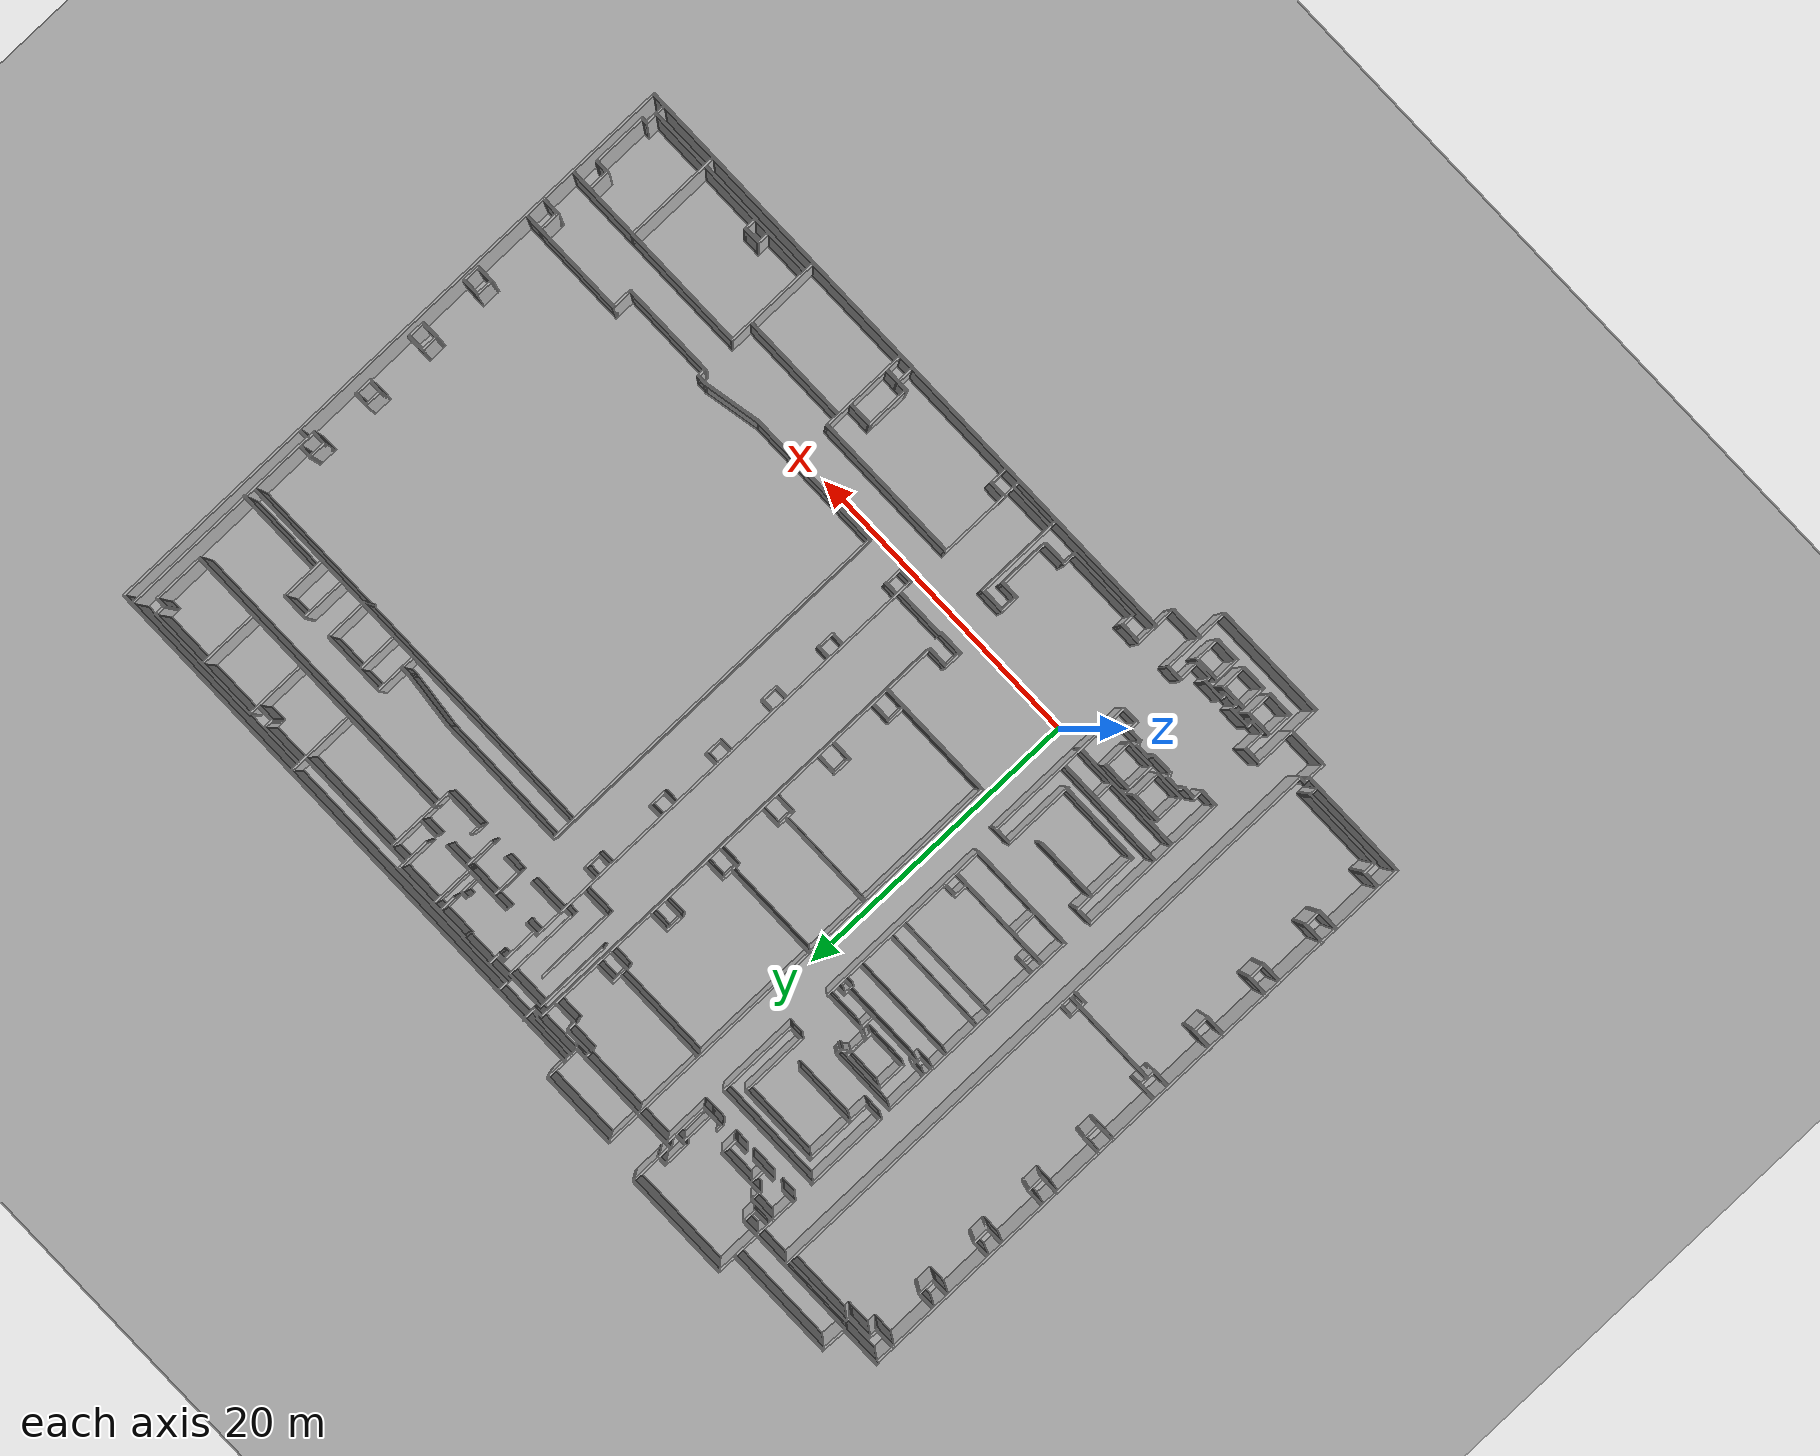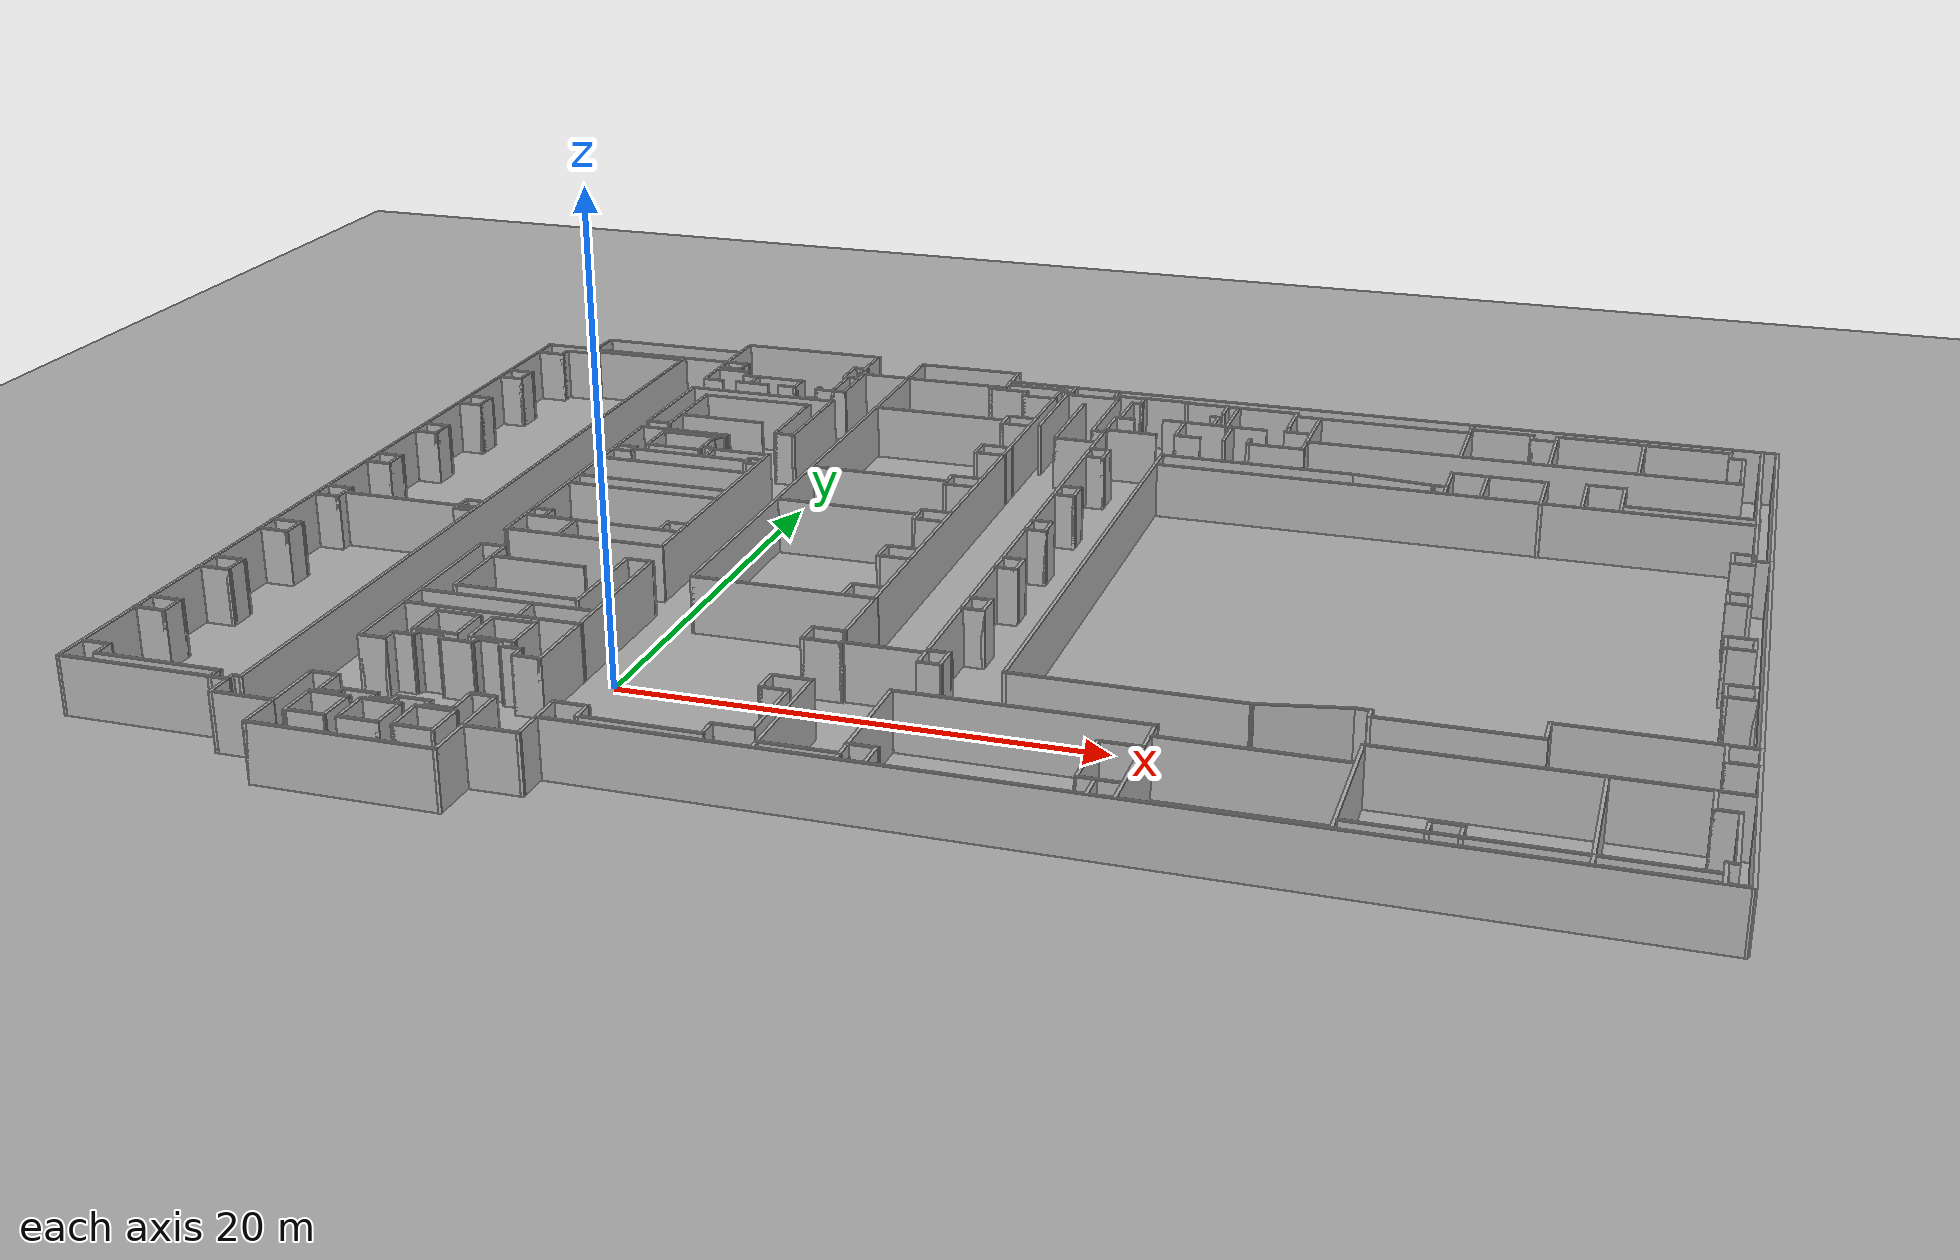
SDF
<sdf version="1.9">
 <world name="tsudanuma2-3">
  <physics name="1ms" type="ignored">
   <max_step_size>0.001</max_step_size>
   <real_time_factor>1.0</real_time_factor>
   <gravity>0 0 -9.8</gravity>
  </physics>
  <plugin filename="libignition-gazebo-physics-system.so" name="ignition::gazebo::systems::Physics"/>
  <plugin filename="libignition-gazebo-user-commands-system.so" name="ignition::gazebo::systems::UserCommands"/>
  <plugin filename="libignition-gazebo-scene-broadcaster-system.so" name="ignition::gazebo::systems::SceneBroadcaster"/>
  <plugin filename="libignition-gazebo-sensors-system.so" name="ignition::gazebo::systems::Sensors">
   <render_engine>ogre2</render_engine>
  </plugin>
  <plugin filename="libignition-gazebo-imu-system.so" name="ignition::gazebo::systems::Imu"/>
  <plugin filename="ignition-gazebo-navsat-system" name="ignition::gazebo::systems::NavSat"/>
  <scene>
   <ambient>1 1 1 1</ambient>
   <background>0.3 0.7 0.9 1</background>
   <shadows>0</shadows>
   <grid>false</grid>
  </scene>
  <light type="directional" name="sun">
   <cast_shadows>0</cast_shadows>
   <pose>0 0 10 0 0 0</pose>
   <diffuse>0.8 0.8 0.8 1</diffuse>
   <specular>0.2 0.2 0.2 1</specular>
   <attenuation>
    <range>1000</range>
    <constant>0.9</constant>
    <linear>0.01</linear>
    <quadratic>0.001</quadratic>
   </attenuation>
   <direction>-0.5 0.1 -0.9</direction>
  </light>
  <model name="ground_plane">
   <static>true</static>
   <link name="link">
    <collision name="collision">
     <geometry><plane><normal>0 0 1</normal><size>100 100</size></plane></geometry>
     <surface>
      <contact><collide_bitmask>65535</collide_bitmask></contact>
      <friction><ode><mu>100</mu><mu2>50</mu2></ode></friction>
     </surface>
    </collision>
    <visual name="visual">
     <cast_shadows>false</cast_shadows>
     <geometry><plane><normal>0 0 1</normal><size>100 100</size></plane></geometry>
     <material>
      <ambient>0.5 0.5 0.5 1</ambient>
      <diffuse>0.7 0.7 0.7 1</diffuse>
      <specular>0.1 0.1 0.1 1</specular>
     </material>
    </visual>
   </link>
  </model>
  <gravity>0 0 -9.8000000000000007</gravity>
  <magnetic_field>6.0000000000000002e-06 2.3e-05 -4.1999999999999998e-05</magnetic_field>
  <atmosphere type="adiabatic"/>
  <spherical_coordinates>
   <surface_model>EARTH_WGS84</surface_model>
   <latitude_deg>0</latitude_deg>
   <longitude_deg>0</longitude_deg>
   <elevation>0</elevation>
   <heading_deg>0</heading_deg>
  </spherical_coordinates>
  <model name="Tsudanuma_2-3-without_door">
   <pose>11.859500000000001 12.3796 0 0 0 0</pose>
   <link name="Wall_0">
    <collision name="Wall_0_Collision">
     <geometry><box><size>41.115000000000002 0.14999999999999999 2.5</size></box></geometry>
     <pose>0 0 1.25 0 0 0</pose>
    </collision>
    <visual name="Wall_0_Visual">
     <pose>0 0 1.25 0 0 0</pose>
     <geometry><box><size>41.115000000000002 0.14999999999999999 2.5</size></box></geometry>
     <material>
      <ambient>0.5 0.5 0.5 1</ambient>
      <diffuse>0.7 0.7 0.7 1</diffuse>
      <specular>0.1 0.1 0.1 1</specular>
     </material>
     <meta><layer>0</layer></meta>
    </visual>
    <pose>-30.8385 -0.074690000000000006 0 0 0 -1.5708</pose>
   </link>
   <link name="Wall_1">
    <collision name="Wall_1_Collision">
     <geometry><box><size>7.4536300000000004 0.14999999999999999 2.5</size></box></geometry>
     <pose>0 0 1.25 0 0 0</pose>
    </collision>
    <visual name="Wall_1_Visual">
     <pose>0 0 1.25 0 0 0</pose>
     <geometry><box><size>7.4536300000000004 0.14999999999999999 2.5</size></box></geometry>
     <material>
      <ambient>0.5 0.5 0.5 1</ambient>
      <diffuse>0.7 0.7 0.7 1</diffuse>
      <specular>0.1 0.1 0.1 1</specular>
     </material>
     <meta><layer>0</layer></meta>
    </visual>
    <pose>-27.1739 -20.558599999999998 0 0 0 -0.00038999999999999994</pose>
   </link>
   <link name="Wall_10">
    <collision name="Wall_10_Collision">
     <geometry><box><size>42.159100000000002 0.14999999999999999 2.5</size></box></geometry>
     <pose>0 0 1.25 0 0 0</pose>
    </collision>
    <visual name="Wall_10_Visual">
     <pose>0 0 1.25 0 0 0</pose>
     <geometry><box><size>42.159100000000002 0.14999999999999999 2.5</size></box></geometry>
     <material>
      <ambient>0.5 0.5 0.5 1</ambient>
      <diffuse>0.7 0.7 0.7 1</diffuse>
      <specular>0.1 0.1 0.1 1</specular>
     </material>
     <meta><layer>0</layer></meta>
    </visual>
    <pose>9.8734099999999998 -20.1767 0 0 0 -0.00063100000000000016</pose>
   </link>
   <link name="Wall_102">
    <collision name="Wall_102_Collision">
     <geometry><box><size>1.25 0.14999999999999999 2.5</size></box></geometry>
     <pose>0 0 1.25 0 0 0</pose>
    </collision>
    <visual name="Wall_102_Visual">
     <pose>0 0 1.25 0 0 0</pose>
     <geometry><box><size>1.25 0.14999999999999999 2.5</size></box></geometry>
     <material>
      <ambient>0.5 0.5 0.5 1</ambient>
      <diffuse>0.7 0.7 0.7 1</diffuse>
      <specular>0.1 0.1 0.1 1</specular>
     </material>
     <meta><layer>0</layer></meta>
    </visual>
    <pose>-20.270800000000001 10.816700000000001 0 0 0 0</pose>
   </link>
   <link name="Wall_103">
    <collision name="Wall_103_Collision">
     <geometry><box><size>1.5 0.14999999999999999 2.5</size></box></geometry>
     <pose>0 0 1.25 0 0 0</pose>
    </collision>
    <visual name="Wall_103_Visual">
     <pose>0 0 1.25 0 0 0</pose>
     <geometry><box><size>1.5 0.14999999999999999 2.5</size></box></geometry>
     <material>
      <ambient>0.5 0.5 0.5 1</ambient>
      <diffuse>0.7 0.7 0.7 1</diffuse>
      <specular>0.1 0.1 0.1 1</specular>
     </material>
     <meta><layer>0</layer></meta>
    </visual>
    <pose>-19.720800000000001 11.4917 0 0 0 1.5708</pose>
   </link>
   <link name="Wall_104">
    <collision name="Wall_104_Collision">
     <geometry><box><size>4.25 0.14999999999999999 2.5</size></box></geometry>
     <pose>0 0 1.25 0 0 0</pose>
    </collision>
    <visual name="Wall_104_Visual">
     <pose>0 0 1.25 0 0 0</pose>
     <geometry><box><size>4.25 0.14999999999999999 2.5</size></box></geometry>
     <material>
      <ambient>0.5 0.5 0.5 1</ambient>
      <diffuse>0.7 0.7 0.7 1</diffuse>
      <specular>0.1 0.1 0.1 1</specular>
     </material>
     <meta><layer>0</layer></meta>
    </visual>
    <pose>-17.6708 12.166700000000001 0 0 0 0</pose>
   </link>
   <link name="Wall_106">
    <collision name="Wall_106_Collision">
     <geometry><box><size>3.25 0.14999999999999999 2.5</size></box></geometry>
     <pose>0 0 1.25 0 0 0</pose>
    </collision>
    <visual name="Wall_106_Visual">
     <pose>0 0 1.25 0 0 0</pose>
     <geometry><box><size>3.25 0.14999999999999999 2.5</size></box></geometry>
     <material>
      <ambient>0.5 0.5 0.5 1</ambient>
      <diffuse>0.7 0.7 0.7 1</diffuse>
      <specular>0.1 0.1 0.1 1</specular>
     </material>
     <meta><layer>0</layer></meta>
    </visual>
    <pose>-19.720800000000001 13.716699999999999 0 0 0 1.5708</pose>
   </link>
   <link name="Wall_107">
    <collision name="Wall_107_Collision">
     <geometry><box><size>5.5 0.14999999999999999 2.5</size></box></geometry>
     <pose>0 0 1.25 0 0 0</pose>
    </collision>
    <visual name="Wall_107_Visual">
     <pose>0 0 1.25 0 0 0</pose>
     <geometry><box><size>5.5 0.14999999999999999 2.5</size></box></geometry>
     <material>
      <ambient>0.5 0.5 0.5 1</ambient>
      <diffuse>0.7 0.7 0.7 1</diffuse>
      <specular>0.1 0.1 0.1 1</specular>
     </material>
     <meta><layer>0</layer></meta>
    </visual>
    <pose>-17.0458 15.2667 0 0 0 0</pose>
   </link>
   <link name="Wall_108">
    <collision name="Wall_108_Collision">
     <geometry><box><size>4.5 0.14999999999999999 2.5</size></box></geometry>
     <pose>0 0 1.25 0 0 0</pose>
    </collision>
    <visual name="Wall_108_Visual">
     <pose>0 0 1.25 0 0 0</pose>
     <geometry><box><size>4.5 0.14999999999999999 2.5</size></box></geometry>
     <material>
      <ambient>0.5 0.5 0.5 1</ambient>
      <diffuse>0.7 0.7 0.7 1</diffuse>
      <specular>0.1 0.1 0.1 1</specular>
     </material>
     <meta><layer>0</layer></meta>
    </visual>
    <pose>-14.370799999999999 13.091699999999999 0 0 0 -1.5708</pose>
   </link>
   <link name="Wall_109">
    <collision name="Wall_109_Collision">
     <geometry><box><size>1 0.14999999999999999 2.5</size></box></geometry>
     <pose>0 0 1.25 0 0 0</pose>
    </collision>
    <visual name="Wall_109_Visual">
     <pose>0 0 1.25 0 0 0</pose>
     <geometry><box><size>1 0.14999999999999999 2.5</size></box></geometry>
     <material>
      <ambient>0.5 0.5 0.5 1</ambient>
      <diffuse>0.7 0.7 0.7 1</diffuse>
      <specular>0.1 0.1 0.1 1</specular>
     </material>
     <meta><layer>0</layer></meta>
    </visual>
    <pose>-13.9458 10.916700000000001 0 0 0 0</pose>
   </link>
   <link name="Wall_11">
    <collision name="Wall_11_Collision">
     <geometry><box><size>42 0.14999999999999999 2.5</size></box></geometry>
     <pose>0 0 1.25 0 0 0</pose>
    </collision>
    <visual name="Wall_11_Visual">
     <pose>0 0 1.25 0 0 0</pose>
     <geometry><box><size>42 0.14999999999999999 2.5</size></box></geometry>
     <material>
      <ambient>0.5 0.5 0.5 1</ambient>
      <diffuse>0.7 0.7 0.7 1</diffuse>
      <specular>0.1 0.1 0.1 1</specular>
     </material>
     <meta><layer>0</layer></meta>
    </visual>
    <pose>30.8779 0.73503799999999997 0 0 0 1.5708</pose>
   </link>
   <link name="Wall_112">
    <collision name="Wall_112_Collision">
     <geometry><box><size>5.4000000000000004 0.14999999999999999 2.5</size></box></geometry>
     <pose>0 0 1.25 0 0 0</pose>
    </collision>
    <visual name="Wall_112_Visual">
     <pose>0 0 1.25 0 0 0</pose>
     <geometry><box><size>5.4000000000000004 0.14999999999999999 2.5</size></box></geometry>
     <material>
      <ambient>0.5 0.5 0.5 1</ambient>
      <diffuse>0.7 0.7 0.7 1</diffuse>
      <specular>0.1 0.1 0.1 1</specular>
     </material>
     <meta><layer>0</layer></meta>
    </visual>
    <pose>-13.461399999999999 13.5404 0 0 0 -1.5708</pose>
   </link>
   <link name="Wall_114">
    <collision name="Wall_114_Collision">
     <geometry><box><size>7.5 0.14999999999999999 2.5</size></box></geometry>
     <pose>0 0 1.25 0 0 0</pose>
    </collision>
    <visual name="Wall_114_Visual">
     <pose>0 0 1.25 0 0 0</pose>
     <geometry><box><size>7.5 0.14999999999999999 2.5</size></box></geometry>
     <material>
      <ambient>0.5 0.5 0.5 1</ambient>
      <diffuse>0.7 0.7 0.7 1</diffuse>
      <specular>0.1 0.1 0.1 1</specular>
     </material>
     <meta><layer>0</layer></meta>
    </visual>
    <pose>-17.145800000000001 16.166699999999999 0 0 0 0</pose>
   </link>
   <link name="Wall_116">
    <collision name="Wall_116_Collision">
     <geometry><box><size>0.71550800000000003 0.14999999999999999 2.5</size></box></geometry>
     <pose>0 0 1.25 0 0 0</pose>
    </collision>
    <visual name="Wall_116_Visual">
     <pose>0 0 1.25 0 0 0</pose>
     <geometry><box><size>0.71550800000000003 0.14999999999999999 2.5</size></box></geometry>
     <material>
      <ambient>0.5 0.5 0.5 1</ambient>
      <diffuse>0.7 0.7 0.7 1</diffuse>
      <specular>0.1 0.1 0.1 1</specular>
     </material>
     <meta><layer>0</layer></meta>
    </visual>
    <pose>-16.6297 9.5424100000000003 0 0 0 0.73186499999999999</pose>
   </link>
   <link name="Wall_118">
    <collision name="Wall_118_Collision">
     <geometry><box><size>0.5 0.14999999999999999 2.5</size></box></geometry>
     <pose>0 0 1.25 0 0 0</pose>
    </collision>
    <visual name="Wall_118_Visual">
     <pose>0 0 1.25 0 0 0</pose>
     <geometry><box><size>0.5 0.14999999999999999 2.5</size></box></geometry>
     <material>
      <ambient>0.5 0.5 0.5 1</ambient>
      <diffuse>0.7 0.7 0.7 1</diffuse>
      <specular>0.1 0.1 0.1 1</specular>
     </material>
     <meta><layer>0</layer></meta>
    </visual>
    <pose>-16.4194 9.8491700000000009 0 0 0 1.5708</pose>
   </link>
   <link name="Wall_119">
    <collision name="Wall_119_Collision">
     <geometry><box><size>4.5 0.14999999999999999 2.5</size></box></geometry>
     <pose>0 0 1.25 0 0 0</pose>
    </collision>
    <visual name="Wall_119_Visual">
     <pose>0 0 1.25 0 0 0</pose>
     <geometry><box><size>4.5 0.14999999999999999 2.5</size></box></geometry>
     <material>
      <ambient>0.5 0.5 0.5 1</ambient>
      <diffuse>0.7 0.7 0.7 1</diffuse>
      <specular>0.1 0.1 0.1 1</specular>
     </material>
     <meta><layer>0</layer></meta>
    </visual>
    <pose>-18.5944 10.0242 0 0 0 3.1415899999999999</pose>
   </link>
   <link name="Wall_12">
    <collision name="Wall_12_Collision">
     <geometry><box><size>37 0.14999999999999999 2.5</size></box></geometry>
     <pose>0 0 1.25 0 0 0</pose>
    </collision>
    <visual name="Wall_12_Visual">
     <pose>0 0 1.25 0 0 0</pose>
     <geometry><box><size>37 0.14999999999999999 2.5</size></box></geometry>
     <material>
      <ambient>0.5 0.5 0.5 1</ambient>
      <diffuse>0.7 0.7 0.7 1</diffuse>
      <specular>0.1 0.1 0.1 1</specular>
     </material>
     <meta><layer>0</layer></meta>
    </visual>
    <pose>12.4529 21.66 0 0 0 3.1415899999999999</pose>
   </link>
   <link name="Wall_120">
    <collision name="Wall_120_Collision">
     <geometry><box><size>14 0.14999999999999999 2.5</size></box></geometry>
     <pose>0 0 1.25 0 0 0</pose>
    </collision>
    <visual name="Wall_120_Visual">
     <pose>0 0 1.25 0 0 0</pose>
     <geometry><box><size>14 0.14999999999999999 2.5</size></box></geometry>
     <material>
      <ambient>0.5 0.5 0.5 1</ambient>
      <diffuse>0.7 0.7 0.7 1</diffuse>
      <specular>0.1 0.1 0.1 1</specular>
     </material>
     <meta><layer>0</layer></meta>
    </visual>
    <pose>-20.769400000000001 3.09917 0 0 0 -1.5708</pose>
   </link>
   <link name="Wall_121">
    <collision name="Wall_121_Collision">
     <geometry><box><size>7.32925 0.14999999999999999 2.5</size></box></geometry>
     <pose>0 0 1.25 0 0 0</pose>
    </collision>
    <visual name="Wall_121_Visual">
     <pose>0 0 1.25 0 0 0</pose>
     <geometry><box><size>7.32925 0.14999999999999999 2.5</size></box></geometry>
     <material>
      <ambient>0.5 0.5 0.5 1</ambient>
      <diffuse>0.7 0.7 0.7 1</diffuse>
      <specular>0.1 0.1 0.1 1</specular>
     </material>
     <meta><layer>0</layer></meta>
    </visual>
    <pose>-17.1797 -3.8258299999999998 0 0 0 0</pose>
   </link>
   <link name="Wall_122">
    <collision name="Wall_122_Collision">
     <geometry><box><size>12 0.14999999999999999 2.5</size></box></geometry>
     <pose>0 0 1.25 0 0 0</pose>
    </collision>
    <visual name="Wall_122_Visual">
     <pose>0 0 1.25 0 0 0</pose>
     <geometry><box><size>12 0.14999999999999999 2.5</size></box></geometry>
     <material>
      <ambient>0.5 0.5 0.5 1</ambient>
      <diffuse>0.7 0.7 0.7 1</diffuse>
      <specular>0.1 0.1 0.1 1</specular>
     </material>
     <meta><layer>0</layer></meta>
    </visual>
    <pose>-13.571099999999999 2.1181399999999999 0 0 0 1.5708</pose>
   </link>
   <link name="Wall_123">
    <collision name="Wall_123_Collision">
     <geometry><box><size>2.82925 0.14999999999999999 2.5</size></box></geometry>
     <pose>0 0 1.25 0 0 0</pose>
    </collision>
    <visual name="Wall_123_Visual">
     <pose>0 0 1.25 0 0 0</pose>
     <geometry><box><size>2.82925 0.14999999999999999 2.5</size></box></geometry>
     <material>
      <ambient>0.5 0.5 0.5 1</ambient>
      <diffuse>0.7 0.7 0.7 1</diffuse>
      <specular>0.1 0.1 0.1 1</specular>
     </material>
     <meta><layer>0</layer></meta>
    </visual>
    <pose>-14.9297 8.0241699999999998 0 0 0 -3.1415899999999999</pose>
   </link>
   <link name="Wall_124">
    <collision name="Wall_124_Collision">
     <geometry><box><size>0.76504799999999995 0.14999999999999999 2.5</size></box></geometry>
     <pose>0 0 1.25 0 0 0</pose>
    </collision>
    <visual name="Wall_124_Visual">
     <pose>0 0 1.25 0 0 0</pose>
     <geometry><box><size>0.76504799999999995 0.14999999999999999 2.5</size></box></geometry>
     <material>
      <ambient>0.5 0.5 0.5 1</ambient>
      <diffuse>0.7 0.7 0.7 1</diffuse>
      <specular>0.1 0.1 0.1 1</specular>
     </material>
     <meta><layer>0</layer></meta>
    </visual>
    <pose>-16.5547 8.1388200000000008 0 0 0 2.7595700000000001</pose>
   </link>
   <link name="Wall_128">
    <collision name="Wall_128_Collision">
     <geometry><box><size>1.25 0.14999999999999999 2.5</size></box></geometry>
     <pose>0 0 1.25 0 0 0</pose>
    </collision>
    <visual name="Wall_128_Visual">
     <pose>0 0 1.25 0 0 0</pose>
     <geometry><box><size>1.25 0.14999999999999999 2.5</size></box></geometry>
     <material>
      <ambient>0.5 0.5 0.5 1</ambient>
      <diffuse>0.7 0.7 0.7 1</diffuse>
      <specular>0.1 0.1 0.1 1</specular>
     </material>
     <meta><layer>0</layer></meta>
    </visual>
    <pose>-16.8401 8.8034599999999994 0 0 0 1.5708</pose>
   </link>
   <link name="Wall_13">
    <collision name="Wall_13_Collision">
     <geometry><box><size>1.5 0.14999999999999999 2.5</size></box></geometry>
     <pose>0 0 1.25 0 0 0</pose>
    </collision>
    <visual name="Wall_13_Visual">
     <pose>0 0 1.25 0 0 0</pose>
     <geometry><box><size>1.5 0.14999999999999999 2.5</size></box></geometry>
     <material>
      <ambient>0.5 0.5 0.5 1</ambient>
      <diffuse>0.7 0.7 0.7 1</diffuse>
      <specular>0.1 0.1 0.1 1</specular>
     </material>
     <meta><layer>0</layer></meta>
    </visual>
    <pose>-5.9720599999999999 22.335000000000001 0 0 0 1.5708</pose>
   </link>
   <link name="Wall_130">
    <collision name="Wall_130_Collision">
     <geometry><box><size>7.25 0.14999999999999999 2.5</size></box></geometry>
     <pose>0 0 1.25 0 0 0</pose>
    </collision>
    <visual name="Wall_130_Visual">
     <pose>0 0 1.25 0 0 0</pose>
     <geometry><box><size>7.25 0.14999999999999999 2.5</size></box></geometry>
     <material>
      <ambient>0.5 0.5 0.5 1</ambient>
      <diffuse>0.7 0.7 0.7 1</diffuse>
      <specular>0.1 0.1 0.1 1</specular>
     </material>
     <meta><layer>0</layer></meta>
    </visual>
    <pose>-17.230499999999999 -2.0692699999999999 0 0 0 0</pose>
   </link>
   <link name="Wall_132">
    <collision name="Wall_132_Collision">
     <geometry><box><size>1 0.14999999999999999 2.5</size></box></geometry>
     <pose>0 0 1.25 0 0 0</pose>
    </collision>
    <visual name="Wall_132_Visual">
     <pose>0 0 1.25 0 0 0</pose>
     <geometry><box><size>1 0.14999999999999999 2.5</size></box></geometry>
     <material>
      <ambient>0.5 0.5 0.5 1</ambient>
      <diffuse>0.7 0.7 0.7 1</diffuse>
      <specular>0.1 0.1 0.1 1</specular>
     </material>
     <meta><layer>0</layer></meta>
    </visual>
    <pose>-20.317499999999999 -1.2914300000000001 0 0 0 0</pose>
   </link>
   <link name="Wall_133">
    <collision name="Wall_133_Collision">
     <geometry><box><size>0.75 0.14999999999999999 2.5</size></box></geometry>
     <pose>0 0 1.25 0 0 0</pose>
    </collision>
    <visual name="Wall_133_Visual">
     <pose>0 0 1.25 0 0 0</pose>
     <geometry><box><size>0.75 0.14999999999999999 2.5</size></box></geometry>
     <material>
      <ambient>0.5 0.5 0.5 1</ambient>
      <diffuse>0.7 0.7 0.7 1</diffuse>
      <specular>0.1 0.1 0.1 1</specular>
     </material>
     <meta><layer>0</layer></meta>
    </visual>
    <pose>-19.892499999999998 -1.5914299999999999 0 0 0 -1.5708</pose>
   </link>
   <link name="Wall_135">
    <collision name="Wall_135_Collision">
     <geometry><box><size>1 0.14999999999999999 2.5</size></box></geometry>
     <pose>0 0 1.25 0 0 0</pose>
    </collision>
    <visual name="Wall_135_Visual">
     <pose>0 0 1.25 0 0 0</pose>
     <geometry><box><size>1 0.14999999999999999 2.5</size></box></geometry>
     <material>
      <ambient>0.5 0.5 0.5 1</ambient>
      <diffuse>0.7 0.7 0.7 1</diffuse>
      <specular>0.1 0.1 0.1 1</specular>
     </material>
     <meta><layer>0</layer></meta>
    </visual>
    <pose>-14.4819 -1.5683800000000001 0 0 0 1.5708</pose>
   </link>
   <link name="Wall_136">
    <collision name="Wall_136_Collision">
     <geometry><box><size>1 0.14999999999999999 2.5</size></box></geometry>
     <pose>0 0 1.25 0 0 0</pose>
    </collision>
    <visual name="Wall_136_Visual">
     <pose>0 0 1.25 0 0 0</pose>
     <geometry><box><size>1 0.14999999999999999 2.5</size></box></geometry>
     <material>
      <ambient>0.5 0.5 0.5 1</ambient>
      <diffuse>0.7 0.7 0.7 1</diffuse>
      <specular>0.1 0.1 0.1 1</specular>
     </material>
     <meta><layer>0</layer></meta>
    </visual>
    <pose>-14.056900000000001 -1.1433800000000001 0 0 0 0</pose>
   </link>
   <link name="Wall_138">
    <collision name="Wall_138_Collision">
     <geometry><box><size>1.75 0.14999999999999999 2.5</size></box></geometry>
     <pose>0 0 1.25 0 0 0</pose>
    </collision>
    <visual name="Wall_138_Visual">
     <pose>0 0 1.25 0 0 0</pose>
     <geometry><box><size>1.75 0.14999999999999999 2.5</size></box></geometry>
     <material>
      <ambient>0.5 0.5 0.5 1</ambient>
      <diffuse>0.7 0.7 0.7 1</diffuse>
      <specular>0.1 0.1 0.1 1</specular>
     </material>
     <meta><layer>0</layer></meta>
    </visual>
    <pose>-18.371099999999998 -2.9072100000000001 0 0 0 -1.5708</pose>
   </link>
   <link name="Wall_14">
    <collision name="Wall_14_Collision">
     <geometry><box><size>5.25 0.14999999999999999 2.5</size></box></geometry>
     <pose>0 0 1.25 0 0 0</pose>
    </collision>
    <visual name="Wall_14_Visual">
     <pose>0 0 1.25 0 0 0</pose>
     <geometry><box><size>5.25 0.14999999999999999 2.5</size></box></geometry>
     <material>
      <ambient>0.5 0.5 0.5 1</ambient>
      <diffuse>0.7 0.7 0.7 1</diffuse>
      <specular>0.1 0.1 0.1 1</specular>
     </material>
     <meta><layer>0</layer></meta>
    </visual>
    <pose>-8.5220599999999997 23.010000000000002 0 0 0 3.1415899999999999</pose>
   </link>
   <link name="Wall_140">
    <collision name="Wall_140_Collision">
     <geometry><box><size>4.25 0.14999999999999999 2.5</size></box></geometry>
     <pose>0 0 1.25 0 0 0</pose>
    </collision>
    <visual name="Wall_140_Visual">
     <pose>0 0 1.25 0 0 0</pose>
     <geometry><box><size>4.25 0.14999999999999999 2.5</size></box></geometry>
     <material>
      <ambient>0.5 0.5 0.5 1</ambient>
      <diffuse>0.7 0.7 0.7 1</diffuse>
      <specular>0.1 0.1 0.1 1</specular>
     </material>
     <meta><layer>0</layer></meta>
    </visual>
    <pose>-17.807400000000001 -6.8076699999999999 0 0 0 3.1415899999999999</pose>
   </link>
   <link name="Wall_141">
    <collision name="Wall_141_Collision">
     <geometry><box><size>1.25 0.14999999999999999 2.5</size></box></geometry>
     <pose>0 0 1.25 0 0 0</pose>
    </collision>
    <visual name="Wall_141_Visual">
     <pose>0 0 1.25 0 0 0</pose>
     <geometry><box><size>1.25 0.14999999999999999 2.5</size></box></geometry>
     <material>
      <ambient>0.5 0.5 0.5 1</ambient>
      <diffuse>0.7 0.7 0.7 1</diffuse>
      <specular>0.1 0.1 0.1 1</specular>
     </material>
     <meta><layer>0</layer></meta>
    </visual>
    <pose>-19.857399999999998 -6.2576700000000001 0 0 0 1.5708</pose>
   </link>
   <link name="Wall_142">
    <collision name="Wall_142_Collision">
     <geometry><box><size>1.25 0.14999999999999999 2.5</size></box></geometry>
     <pose>0 0 1.25 0 0 0</pose>
    </collision>
    <visual name="Wall_142_Visual">
     <pose>0 0 1.25 0 0 0</pose>
     <geometry><box><size>1.25 0.14999999999999999 2.5</size></box></geometry>
     <material>
      <ambient>0.5 0.5 0.5 1</ambient>
      <diffuse>0.7 0.7 0.7 1</diffuse>
      <specular>0.1 0.1 0.1 1</specular>
     </material>
     <meta><layer>0</layer></meta>
    </visual>
    <pose>-20.407399999999999 -5.7076700000000002 0 0 0 3.1415899999999999</pose>
   </link>
   <link name="Wall_143">
    <collision name="Wall_143_Collision">
     <geometry><box><size>10 0.14999999999999999 2.5</size></box></geometry>
     <pose>0 0 1.25 0 0 0</pose>
    </collision>
    <visual name="Wall_143_Visual">
     <pose>0 0 1.25 0 0 0</pose>
     <geometry><box><size>10 0.14999999999999999 2.5</size></box></geometry>
     <material>
      <ambient>0.5 0.5 0.5 1</ambient>
      <diffuse>0.7 0.7 0.7 1</diffuse>
      <specular>0.1 0.1 0.1 1</specular>
     </material>
     <meta><layer>0</layer></meta>
    </visual>
    <pose>-20.9574 -10.6327 0 0 0 -1.5708</pose>
   </link>
   <link name="Wall_144">
    <collision name="Wall_144_Collision">
     <geometry><box><size>1.25 0.14999999999999999 2.5</size></box></geometry>
     <pose>0 0 1.25 0 0 0</pose>
    </collision>
    <visual name="Wall_144_Visual">
     <pose>0 0 1.25 0 0 0</pose>
     <geometry><box><size>1.25 0.14999999999999999 2.5</size></box></geometry>
     <material>
      <ambient>0.5 0.5 0.5 1</ambient>
      <diffuse>0.7 0.7 0.7 1</diffuse>
      <specular>0.1 0.1 0.1 1</specular>
     </material>
     <meta><layer>0</layer></meta>
    </visual>
    <pose>-20.407399999999999 -15.557700000000001 0 0 0 0</pose>
   </link>
   <link name="Wall_145">
    <collision name="Wall_145_Collision">
     <geometry><box><size>0.75 0.14999999999999999 2.5</size></box></geometry>
     <pose>0 0 1.25 0 0 0</pose>
    </collision>
    <visual name="Wall_145_Visual">
     <pose>0 0 1.25 0 0 0</pose>
     <geometry><box><size>0.75 0.14999999999999999 2.5</size></box></geometry>
     <material>
      <ambient>0.5 0.5 0.5 1</ambient>
      <diffuse>0.7 0.7 0.7 1</diffuse>
      <specular>0.1 0.1 0.1 1</specular>
     </material>
     <meta><layer>0</layer></meta>
    </visual>
    <pose>-19.857399999999998 -15.2577 0 0 0 1.5708</pose>
   </link>
   <link name="Wall_146">
    <collision name="Wall_146_Collision">
     <geometry><box><size>1 0.14999999999999999 2.5</size></box></geometry>
     <pose>0 0 1.25 0 0 0</pose>
    </collision>
    <visual name="Wall_146_Visual">
     <pose>0 0 1.25 0 0 0</pose>
     <geometry><box><size>1 0.14999999999999999 2.5</size></box></geometry>
     <material>
      <ambient>0.5 0.5 0.5 1</ambient>
      <diffuse>0.7 0.7 0.7 1</diffuse>
      <specular>0.1 0.1 0.1 1</specular>
     </material>
     <meta><layer>0</layer></meta>
    </visual>
    <pose>-19.432400000000001 -14.957700000000001 0 0 0 0</pose>
   </link>
   <link name="Wall_147">
    <collision name="Wall_147_Collision">
     <geometry><box><size>0.5 0.14999999999999999 2.5</size></box></geometry>
     <pose>0 0 1.25 0 0 0</pose>
    </collision>
    <visual name="Wall_147_Visual">
     <pose>0 0 1.25 0 0 0</pose>
     <geometry><box><size>0.5 0.14999999999999999 2.5</size></box></geometry>
     <material>
      <ambient>0.5 0.5 0.5 1</ambient>
      <diffuse>0.7 0.7 0.7 1</diffuse>
      <specular>0.1 0.1 0.1 1</specular>
     </material>
     <meta><layer>0</layer></meta>
    </visual>
    <pose>-18.919899999999998 -14.806100000000001 0 0 0 1.0471999999999999</pose>
   </link>
   <link name="Wall_148">
    <collision name="Wall_148_Collision">
     <geometry><box><size>1 0.14999999999999999 2.5</size></box></geometry>
     <pose>0 0 1.25 0 0 0</pose>
    </collision>
    <visual name="Wall_148_Visual">
     <pose>0 0 1.25 0 0 0</pose>
     <geometry><box><size>1 0.14999999999999999 2.5</size></box></geometry>
     <material>
      <ambient>0.5 0.5 0.5 1</ambient>
      <diffuse>0.7 0.7 0.7 1</diffuse>
      <specular>0.1 0.1 0.1 1</specular>
     </material>
     <meta><layer>0</layer></meta>
    </visual>
    <pose>-18.407399999999999 -14.6546 0 0 0 0</pose>
   </link>
   <link name="Wall_149">
    <collision name="Wall_149_Collision">
     <geometry><box><size>0.5 0.14999999999999999 2.5</size></box></geometry>
     <pose>0 0 1.25 0 0 0</pose>
    </collision>
    <visual name="Wall_149_Visual">
     <pose>0 0 1.25 0 0 0</pose>
     <geometry><box><size>0.5 0.14999999999999999 2.5</size></box></geometry>
     <material>
      <ambient>0.5 0.5 0.5 1</ambient>
      <diffuse>0.7 0.7 0.7 1</diffuse>
      <specular>0.1 0.1 0.1 1</specular>
     </material>
     <meta><layer>0</layer></meta>
    </visual>
    <pose>-17.8949 -14.806100000000001 0 0 0 -1.0471999999999999</pose>
   </link>
   <link name="Wall_15">
    <collision name="Wall_15_Collision">
     <geometry><box><size>2.5 0.14999999999999999 2.5</size></box></geometry>
     <pose>0 0 1.25 0 0 0</pose>
    </collision>
    <visual name="Wall_15_Visual">
     <pose>0 0 1.25 0 0 0</pose>
     <geometry><box><size>2.5 0.14999999999999999 2.5</size></box></geometry>
     <material>
      <ambient>0.5 0.5 0.5 1</ambient>
      <diffuse>0.7 0.7 0.7 1</diffuse>
      <specular>0.1 0.1 0.1 1</specular>
     </material>
     <meta><layer>0</layer></meta>
    </visual>
    <pose>-11.072100000000001 21.835000000000001 0 0 0 -1.5708</pose>
   </link>
   <link name="Wall_150">
    <collision name="Wall_150_Collision">
     <geometry><box><size>1.5 0.14999999999999999 2.5</size></box></geometry>
     <pose>0 0 1.25 0 0 0</pose>
    </collision>
    <visual name="Wall_150_Visual">
     <pose>0 0 1.25 0 0 0</pose>
     <geometry><box><size>1.5 0.14999999999999999 2.5</size></box></geometry>
     <material>
      <ambient>0.5 0.5 0.5 1</ambient>
      <diffuse>0.7 0.7 0.7 1</diffuse>
      <specular>0.1 0.1 0.1 1</specular>
     </material>
     <meta><layer>0</layer></meta>
    </visual>
    <pose>-17.132400000000001 -14.957700000000001 0 0 0 0</pose>
   </link>
   <link name="Wall_151">
    <collision name="Wall_151_Collision">
     <geometry><box><size>0.5 0.14999999999999999 2.5</size></box></geometry>
     <pose>0 0 1.25 0 0 0</pose>
    </collision>
    <visual name="Wall_151_Visual">
     <pose>0 0 1.25 0 0 0</pose>
     <geometry><box><size>0.5 0.14999999999999999 2.5</size></box></geometry>
     <material>
      <ambient>0.5 0.5 0.5 1</ambient>
      <diffuse>0.7 0.7 0.7 1</diffuse>
      <specular>0.1 0.1 0.1 1</specular>
     </material>
     <meta><layer>0</layer></meta>
    </visual>
    <pose>-16.369900000000001 -14.806100000000001 0 0 0 1.0471999999999999</pose>
   </link>
   <link name="Wall_152">
    <collision name="Wall_152_Collision">
     <geometry><box><size>1 0.14999999999999999 2.5</size></box></geometry>
     <pose>0 0 1.25 0 0 0</pose>
    </collision>
    <visual name="Wall_152_Visual">
     <pose>0 0 1.25 0 0 0</pose>
     <geometry><box><size>1 0.14999999999999999 2.5</size></box></geometry>
     <material>
      <ambient>0.5 0.5 0.5 1</ambient>
      <diffuse>0.7 0.7 0.7 1</diffuse>
      <specular>0.1 0.1 0.1 1</specular>
     </material>
     <meta><layer>0</layer></meta>
    </visual>
    <pose>-15.8574 -14.6546 0 0 0 0</pose>
   </link>
   <link name="Wall_153">
    <collision name="Wall_153_Collision">
     <geometry><box><size>0.5 0.14999999999999999 2.5</size></box></geometry>
     <pose>0 0 1.25 0 0 0</pose>
    </collision>
    <visual name="Wall_153_Visual">
     <pose>0 0 1.25 0 0 0</pose>
     <geometry><box><size>0.5 0.14999999999999999 2.5</size></box></geometry>
     <material>
      <ambient>0.5 0.5 0.5 1</ambient>
      <diffuse>0.7 0.7 0.7 1</diffuse>
      <specular>0.1 0.1 0.1 1</specular>
     </material>
     <meta><layer>0</layer></meta>
    </visual>
    <pose>-15.344900000000001 -14.806100000000001 0 0 0 -1.0471999999999999</pose>
   </link>
   <link name="Wall_154">
    <collision name="Wall_154_Collision">
     <geometry><box><size>1 0.14999999999999999 2.5</size></box></geometry>
     <pose>0 0 1.25 0 0 0</pose>
    </collision>
    <visual name="Wall_154_Visual">
     <pose>0 0 1.25 0 0 0</pose>
     <geometry><box><size>1 0.14999999999999999 2.5</size></box></geometry>
     <material>
      <ambient>0.5 0.5 0.5 1</ambient>
      <diffuse>0.7 0.7 0.7 1</diffuse>
      <specular>0.1 0.1 0.1 1</specular>
     </material>
     <meta><layer>0</layer></meta>
    </visual>
    <pose>-14.8324 -14.957700000000001 0 0 0 0</pose>
   </link>
   <link name="Wall_155">
    <collision name="Wall_155_Collision">
     <geometry><box><size>0.75 0.14999999999999999 2.5</size></box></geometry>
     <pose>0 0 1.25 0 0 0</pose>
    </collision>
    <visual name="Wall_155_Visual">
     <pose>0 0 1.25 0 0 0</pose>
     <geometry><box><size>0.75 0.14999999999999999 2.5</size></box></geometry>
     <material>
      <ambient>0.5 0.5 0.5 1</ambient>
      <diffuse>0.7 0.7 0.7 1</diffuse>
      <specular>0.1 0.1 0.1 1</specular>
     </material>
     <meta><layer>0</layer></meta>
    </visual>
    <pose>-14.407400000000001 -15.2577 0 0 0 -1.5708</pose>
   </link>
   <link name="Wall_156">
    <collision name="Wall_156_Collision">
     <geometry><box><size>1.25 0.14999999999999999 2.5</size></box></geometry>
     <pose>0 0 1.25 0 0 0</pose>
    </collision>
    <visual name="Wall_156_Visual">
     <pose>0 0 1.25 0 0 0</pose>
     <geometry><box><size>1.25 0.14999999999999999 2.5</size></box></geometry>
     <material>
      <ambient>0.5 0.5 0.5 1</ambient>
      <diffuse>0.7 0.7 0.7 1</diffuse>
      <specular>0.1 0.1 0.1 1</specular>
     </material>
     <meta><layer>0</layer></meta>
    </visual>
    <pose>-13.8574 -15.557700000000001 0 0 0 0</pose>
   </link>
   <link name="Wall_157">
    <collision name="Wall_157_Collision">
     <geometry><box><size>10.25 0.14999999999999999 2.5</size></box></geometry>
     <pose>0 0 1.25 0 0 0</pose>
    </collision>
    <visual name="Wall_157_Visual">
     <pose>0 0 1.25 0 0 0</pose>
     <geometry><box><size>10.25 0.14999999999999999 2.5</size></box></geometry>
     <material>
      <ambient>0.5 0.5 0.5 1</ambient>
      <diffuse>0.7 0.7 0.7 1</diffuse>
      <specular>0.1 0.1 0.1 1</specular>
     </material>
     <meta><layer>0</layer></meta>
    </visual>
    <pose>-13.307399999999999 -10.5077 0 0 0 1.5708</pose>
   </link>
   <link name="Wall_158">
    <collision name="Wall_158_Collision">
     <geometry><box><size>1.25 0.14999999999999999 2.5</size></box></geometry>
     <pose>0 0 1.25 0 0 0</pose>
    </collision>
    <visual name="Wall_158_Visual">
     <pose>0 0 1.25 0 0 0</pose>
     <geometry><box><size>1.25 0.14999999999999999 2.5</size></box></geometry>
     <material>
      <ambient>0.5 0.5 0.5 1</ambient>
      <diffuse>0.7 0.7 0.7 1</diffuse>
      <specular>0.1 0.1 0.1 1</specular>
     </material>
     <meta><layer>0</layer></meta>
    </visual>
    <pose>-13.8574 -5.4671000000000003 0 0 0 -3.1244499999999999</pose>
   </link>
   <link name="Wall_16">
    <collision name="Wall_16_Collision">
     <geometry><box><size>2.75 0.14999999999999999 2.5</size></box></geometry>
     <pose>0 0 1.25 0 0 0</pose>
    </collision>
    <visual name="Wall_16_Visual">
     <pose>0 0 1.25 0 0 0</pose>
     <geometry><box><size>2.75 0.14999999999999999 2.5</size></box></geometry>
     <material>
      <ambient>0.5 0.5 0.5 1</ambient>
      <diffuse>0.7 0.7 0.7 1</diffuse>
      <specular>0.1 0.1 0.1 1</specular>
     </material>
     <meta><layer>0</layer></meta>
    </visual>
    <pose>-12.3721 20.66 0 0 0 3.1415899999999999</pose>
   </link>
   <link name="Wall_160">
    <collision name="Wall_160_Collision">
     <geometry><box><size>5.5 0.14999999999999999 2.5</size></box></geometry>
     <pose>0 0 1.25 0 0 0</pose>
    </collision>
    <visual name="Wall_160_Visual">
     <pose>0 0 1.25 0 0 0</pose>
     <geometry><box><size>5.5 0.14999999999999999 2.5</size></box></geometry>
     <material>
      <ambient>0.5 0.5 0.5 1</ambient>
      <diffuse>0.7 0.7 0.7 1</diffuse>
      <specular>0.1 0.1 0.1 1</specular>
     </material>
     <meta><layer>0</layer></meta>
    </visual>
    <pose>-17.1919 -10.0068 0 0 0 3.1415899999999999</pose>
   </link>
   <link name="Wall_161">
    <collision name="Wall_161_Collision">
     <geometry><box><size>3.3492099999999998 0.14999999999999999 2.5</size></box></geometry>
     <pose>0 0 1.25 0 0 0</pose>
    </collision>
    <visual name="Wall_161_Visual">
     <pose>0 0 1.25 0 0 0</pose>
     <geometry><box><size>3.3492099999999998 0.14999999999999999 2.5</size></box></geometry>
     <material>
      <ambient>0.5 0.5 0.5 1</ambient>
      <diffuse>0.7 0.7 0.7 1</diffuse>
      <specular>0.1 0.1 0.1 1</specular>
     </material>
     <meta><layer>0</layer></meta>
    </visual>
    <pose>-19.857399999999998 -8.4072099999999992 0 0 0 1.5708</pose>
   </link>
   <link name="Wall_163">
    <collision name="Wall_163_Collision">
     <geometry><box><size>4.75 0.14999999999999999 2.5</size></box></geometry>
     <pose>0 0 1.25 0 0 0</pose>
    </collision>
    <visual name="Wall_163_Visual">
     <pose>0 0 1.25 0 0 0</pose>
     <geometry><box><size>4.75 0.14999999999999999 2.5</size></box></geometry>
     <material>
      <ambient>0.5 0.5 0.5 1</ambient>
      <diffuse>0.7 0.7 0.7 1</diffuse>
      <specular>0.1 0.1 0.1 1</specular>
     </material>
     <meta><layer>0</layer></meta>
    </visual>
    <pose>-14.407400000000001 -7.7765399999999998 0 0 0 -1.5708</pose>
   </link>
   <link name="Wall_165">
    <collision name="Wall_165_Collision">
     <geometry><box><size>7.7000000000000002 0.14999999999999999 2.5</size></box></geometry>
     <pose>0 0 1.25 0 0 0</pose>
    </collision>
    <visual name="Wall_165_Visual">
     <pose>0 0 1.25 0 0 0</pose>
     <geometry><box><size>7.7000000000000002 0.14999999999999999 2.5</size></box></geometry>
     <material>
      <ambient>0.5 0.5 0.5 1</ambient>
      <diffuse>0.7 0.7 0.7 1</diffuse>
      <specular>0.1 0.1 0.1 1</specular>
     </material>
     <meta><layer>0</layer></meta>
    </visual>
    <pose>-17.101900000000001 -10.852499999999999 0 0 0 0</pose>
   </link>
   <link name="Wall_167">
    <collision name="Wall_167_Collision">
     <geometry><box><size>7.75 0.14999999999999999 2.5</size></box></geometry>
     <pose>0 0 1.25 0 0 0</pose>
    </collision>
    <visual name="Wall_167_Visual">
     <pose>0 0 1.25 0 0 0</pose>
     <geometry><box><size>7.75 0.14999999999999999 2.5</size></box></geometry>
     <material>
      <ambient>0.5 0.5 0.5 1</ambient>
      <diffuse>0.7 0.7 0.7 1</diffuse>
      <specular>0.1 0.1 0.1 1</specular>
     </material>
     <meta><layer>0</layer></meta>
    </visual>
    <pose>-17.093499999999999 -12.1708 0 0 0 0</pose>
   </link>
   <link name="Wall_169">
    <collision name="Wall_169_Collision">
     <geometry><box><size>1.25 0.14999999999999999 2.5</size></box></geometry>
     <pose>0 0 1.25 0 0 0</pose>
    </collision>
    <visual name="Wall_169_Visual">
     <pose>0 0 1.25 0 0 0</pose>
     <geometry><box><size>1.25 0.14999999999999999 2.5</size></box></geometry>
     <material>
      <ambient>0.5 0.5 0.5 1</ambient>
      <diffuse>0.7 0.7 0.7 1</diffuse>
      <specular>0.1 0.1 0.1 1</specular>
     </material>
     <meta><layer>0</layer></meta>
    </visual>
    <pose>-15.9785 -11.495100000000001 0 0 0 -1.5708</pose>
   </link>
   <link name="Wall_17">
    <collision name="Wall_17_Collision">
     <geometry><box><size>3 0.14999999999999999 2.5</size></box></geometry>
     <pose>0 0 1.25 0 0 0</pose>
    </collision>
    <visual name="Wall_17_Visual">
     <pose>0 0 1.25 0 0 0</pose>
     <geometry><box><size>3 0.14999999999999999 2.5</size></box></geometry>
     <material>
      <ambient>0.5 0.5 0.5 1</ambient>
      <diffuse>0.7 0.7 0.7 1</diffuse>
      <specular>0.1 0.1 0.1 1</specular>
     </material>
     <meta><layer>0</layer></meta>
    </visual>
    <pose>-13.6721 22.085000000000001 0 0 0 1.5708</pose>
   </link>
   <link name="Wall_171">
    <collision name="Wall_171_Collision">
     <geometry><box><size>6.5 0.14999999999999999 2.5</size></box></geometry>
     <pose>0 0 1.25 0 0 0</pose>
    </collision>
    <visual name="Wall_171_Visual">
     <pose>0 0 1.25 0 0 0</pose>
     <geometry><box><size>6.5 0.14999999999999999 2.5</size></box></geometry>
     <material>
      <ambient>0.5 0.5 0.5 1</ambient>
      <diffuse>0.7 0.7 0.7 1</diffuse>
      <specular>0.1 0.1 0.1 1</specular>
     </material>
     <meta><layer>0</layer></meta>
    </visual>
    <pose>-7.8449200000000001 7.16554 0 0 0 0</pose>
   </link>
   <link name="Wall_173">
    <collision name="Wall_173_Collision">
     <geometry><box><size>6.5 0.14999999999999999 2.5</size></box></geometry>
     <pose>0 0 1.25 0 0 0</pose>
    </collision>
    <visual name="Wall_173_Visual">
     <pose>0 0 1.25 0 0 0</pose>
     <geometry><box><size>6.5 0.14999999999999999 2.5</size></box></geometry>
     <material>
      <ambient>0.5 0.5 0.5 1</ambient>
      <diffuse>0.7 0.7 0.7 1</diffuse>
      <specular>0.1 0.1 0.1 1</specular>
     </material>
     <meta><layer>0</layer></meta>
    </visual>
    <pose>-7.8185599999999997 2.8487499999999999 0 0 0 0</pose>
   </link>
   <link name="Wall_176">
    <collision name="Wall_176_Collision">
     <geometry><box><size>2.75 0.14999999999999999 2.5</size></box></geometry>
     <pose>0 0 1.25 0 0 0</pose>
    </collision>
    <visual name="Wall_176_Visual">
     <pose>0 0 1.25 0 0 0</pose>
     <geometry><box><size>2.75 0.14999999999999999 2.5</size></box></geometry>
     <material>
      <ambient>0.5 0.5 0.5 1</ambient>
      <diffuse>0.7 0.7 0.7 1</diffuse>
      <specular>0.1 0.1 0.1 1</specular>
     </material>
     <meta><layer>0</layer></meta>
    </visual>
    <pose>-20.9221 -20.359999999999999 0 0 0 1.5708</pose>
   </link>
   <link name="Wall_177">
    <collision name="Wall_177_Collision">
     <geometry><box><size>1.25 0.14999999999999999 2.5</size></box></geometry>
     <pose>0 0 1.25 0 0 0</pose>
    </collision>
    <visual name="Wall_177_Visual">
     <pose>0 0 1.25 0 0 0</pose>
     <geometry><box><size>1.25 0.14999999999999999 2.5</size></box></geometry>
     <material>
      <ambient>0.5 0.5 0.5 1</ambient>
      <diffuse>0.7 0.7 0.7 1</diffuse>
      <specular>0.1 0.1 0.1 1</specular>
     </material>
     <meta><layer>0</layer></meta>
    </visual>
    <pose>-20.3721 -19.059999999999999 0 0 0 0</pose>
   </link>
   <link name="Wall_178">
    <collision name="Wall_178_Collision">
     <geometry><box><size>1.4923500000000001 0.14999999999999999 2.5</size></box></geometry>
     <pose>0 0 1.25 0 0 0</pose>
    </collision>
    <visual name="Wall_178_Visual">
     <pose>0 0 1.25 0 0 0</pose>
     <geometry><box><size>1.4923500000000001 0.14999999999999999 2.5</size></box></geometry>
     <material>
      <ambient>0.5 0.5 0.5 1</ambient>
      <diffuse>0.7 0.7 0.7 1</diffuse>
      <specular>0.1 0.1 0.1 1</specular>
     </material>
     <meta><layer>0</layer></meta>
    </visual>
    <pose>-19.821400000000001 -19.731200000000001 0 0 0 -1.56976</pose>
   </link>
   <link name="Wall_179">
    <collision name="Wall_179_Collision">
     <geometry><box><size>1 0.14999999999999999 2.5</size></box></geometry>
     <pose>0 0 1.25 0 0 0</pose>
    </collision>
    <visual name="Wall_179_Visual">
     <pose>0 0 1.25 0 0 0</pose>
     <geometry><box><size>1 0.14999999999999999 2.5</size></box></geometry>
     <material>
      <ambient>0.5 0.5 0.5 1</ambient>
      <diffuse>0.7 0.7 0.7 1</diffuse>
      <specular>0.1 0.1 0.1 1</specular>
     </material>
     <meta><layer>0</layer></meta>
    </visual>
    <pose>-19.395700000000001 -20.4038 0 0 0 0</pose>
   </link>
   <link name="Wall_18">
    <collision name="Wall_18_Collision">
     <geometry><box><size>7.25 0.14999999999999999 2.5</size></box></geometry>
     <pose>0 0 1.25 0 0 0</pose>
    </collision>
    <visual name="Wall_18_Visual">
     <pose>0 0 1.25 0 0 0</pose>
     <geometry><box><size>7.25 0.14999999999999999 2.5</size></box></geometry>
     <material>
      <ambient>0.5 0.5 0.5 1</ambient>
      <diffuse>0.7 0.7 0.7 1</diffuse>
      <specular>0.1 0.1 0.1 1</specular>
     </material>
     <meta><layer>0</layer></meta>
    </visual>
    <pose>-17.222100000000001 23.510000000000002 0 0 0 3.1415899999999999</pose>
   </link>
   <link name="Wall_180">
    <collision name="Wall_180_Collision">
     <geometry><box><size>0.49235499999999999 0.14999999999999999 2.5</size></box></geometry>
     <pose>0 0 1.25 0 0 0</pose>
    </collision>
    <visual name="Wall_180_Visual">
     <pose>0 0 1.25 0 0 0</pose>
     <geometry><box><size>0.49235499999999999 0.14999999999999999 2.5</size></box></geometry>
     <material>
      <ambient>0.5 0.5 0.5 1</ambient>
      <diffuse>0.7 0.7 0.7 1</diffuse>
      <specular>0.1 0.1 0.1 1</specular>
     </material>
     <meta><layer>0</layer></meta>
    </visual>
    <pose>-18.971399999999999 -20.231200000000001 0 0 0 1.5748500000000001</pose>
   </link>
   <link name="Wall_181">
    <collision name="Wall_181_Collision">
     <geometry><box><size>1.5 0.14999999999999999 2.5</size></box></geometry>
     <pose>0 0 1.25 0 0 0</pose>
    </collision>
    <visual name="Wall_181_Visual">
     <pose>0 0 1.25 0 0 0</pose>
     <geometry><box><size>1.5 0.14999999999999999 2.5</size></box></geometry>
     <material>
      <ambient>0.5 0.5 0.5 1</ambient>
      <diffuse>0.7 0.7 0.7 1</diffuse>
      <specular>0.1 0.1 0.1 1</specular>
     </material>
     <meta><layer>0</layer></meta>
    </visual>
    <pose>-18.2971 -20.059999999999999 0 0 0 0</pose>
   </link>
   <link name="Wall_182">
    <collision name="Wall_182_Collision">
     <geometry><box><size>0.502135 0.14999999999999999 2.5</size></box></geometry>
     <pose>0 0 1.25 0 0 0</pose>
    </collision>
    <visual name="Wall_182_Visual">
     <pose>0 0 1.25 0 0 0</pose>
     <geometry><box><size>0.502135 0.14999999999999999 2.5</size></box></geometry>
     <material>
      <ambient>0.5 0.5 0.5 1</ambient>
      <diffuse>0.7 0.7 0.7 1</diffuse>
      <specular>0.1 0.1 0.1 1</specular>
     </material>
     <meta><layer>0</layer></meta>
    </visual>
    <pose>-17.6221 -20.2361 0 0 0 -1.5708</pose>
   </link>
   <link name="Wall_183">
    <collision name="Wall_183_Collision">
     <geometry><box><size>1 0.14999999999999999 2.5</size></box></geometry>
     <pose>0 0 1.25 0 0 0</pose>
    </collision>
    <visual name="Wall_183_Visual">
     <pose>0 0 1.25 0 0 0</pose>
     <geometry><box><size>1 0.14999999999999999 2.5</size></box></geometry>
     <material>
      <ambient>0.5 0.5 0.5 1</ambient>
      <diffuse>0.7 0.7 0.7 1</diffuse>
      <specular>0.1 0.1 0.1 1</specular>
     </material>
     <meta><layer>0</layer></meta>
    </visual>
    <pose>-17.198499999999999 -20.412199999999999 0 0 0 0</pose>
   </link>
   <link name="Wall_184">
    <collision name="Wall_184_Collision">
     <geometry><box><size>0.502135 0.14999999999999999 2.5</size></box></geometry>
     <pose>0 0 1.25 0 0 0</pose>
    </collision>
    <visual name="Wall_184_Visual">
     <pose>0 0 1.25 0 0 0</pose>
     <geometry><box><size>0.502135 0.14999999999999999 2.5</size></box></geometry>
     <material>
      <ambient>0.5 0.5 0.5 1</ambient>
      <diffuse>0.7 0.7 0.7 1</diffuse>
      <specular>0.1 0.1 0.1 1</specular>
     </material>
     <meta><layer>0</layer></meta>
    </visual>
    <pose>-16.772099999999998 -20.2361 0 0 0 1.5708</pose>
   </link>
   <link name="Wall_185">
    <collision name="Wall_185_Collision">
     <geometry><box><size>1.5 0.14999999999999999 2.5</size></box></geometry>
     <pose>0 0 1.25 0 0 0</pose>
    </collision>
    <visual name="Wall_185_Visual">
     <pose>0 0 1.25 0 0 0</pose>
     <geometry><box><size>1.5 0.14999999999999999 2.5</size></box></geometry>
     <material>
      <ambient>0.5 0.5 0.5 1</ambient>
      <diffuse>0.7 0.7 0.7 1</diffuse>
      <specular>0.1 0.1 0.1 1</specular>
     </material>
     <meta><layer>0</layer></meta>
    </visual>
    <pose>-16.097100000000001 -20.059999999999999 0 0 0 0</pose>
   </link>
   <link name="Wall_186">
    <collision name="Wall_186_Collision">
     <geometry><box><size>0.5 0.14999999999999999 2.5</size></box></geometry>
     <pose>0 0 1.25 0 0 0</pose>
    </collision>
    <visual name="Wall_186_Visual">
     <pose>0 0 1.25 0 0 0</pose>
     <geometry><box><size>0.5 0.14999999999999999 2.5</size></box></geometry>
     <material>
      <ambient>0.5 0.5 0.5 1</ambient>
      <diffuse>0.7 0.7 0.7 1</diffuse>
      <specular>0.1 0.1 0.1 1</specular>
     </material>
     <meta><layer>0</layer></meta>
    </visual>
    <pose>-15.4221 -20.234999999999999 0 0 0 -1.5708</pose>
   </link>
   <link name="Wall_187">
    <collision name="Wall_187_Collision">
     <geometry><box><size>1.25 0.14999999999999999 2.5</size></box></geometry>
     <pose>0 0 1.25 0 0 0</pose>
    </collision>
    <visual name="Wall_187_Visual">
     <pose>0 0 1.25 0 0 0</pose>
     <geometry><box><size>1.25 0.14999999999999999 2.5</size></box></geometry>
     <material>
      <ambient>0.5 0.5 0.5 1</ambient>
      <diffuse>0.7 0.7 0.7 1</diffuse>
      <specular>0.1 0.1 0.1 1</specular>
     </material>
     <meta><layer>0</layer></meta>
    </visual>
    <pose>-14.8721 -20.41 0 0 0 0</pose>
   </link>
   <link name="Wall_188">
    <collision name="Wall_188_Collision">
     <geometry><box><size>1.5 0.14999999999999999 2.5</size></box></geometry>
     <pose>0 0 1.25 0 0 0</pose>
    </collision>
    <visual name="Wall_188_Visual">
     <pose>0 0 1.25 0 0 0</pose>
     <geometry><box><size>1.5 0.14999999999999999 2.5</size></box></geometry>
     <material>
      <ambient>0.5 0.5 0.5 1</ambient>
      <diffuse>0.7 0.7 0.7 1</diffuse>
      <specular>0.1 0.1 0.1 1</specular>
     </material>
     <meta><layer>0</layer></meta>
    </visual>
    <pose>-14.322100000000001 -19.734999999999999 0 0 0 1.5708</pose>
   </link>
   <link name="Wall_189">
    <collision name="Wall_189_Collision">
     <geometry><box><size>1.1000000000000001 0.14999999999999999 2.5</size></box></geometry>
     <pose>0 0 1.25 0 0 0</pose>
    </collision>
    <visual name="Wall_189_Visual">
     <pose>0 0 1.25 0 0 0</pose>
     <geometry><box><size>1.1000000000000001 0.14999999999999999 2.5</size></box></geometry>
     <material>
      <ambient>0.5 0.5 0.5 1</ambient>
      <diffuse>0.7 0.7 0.7 1</diffuse>
      <specular>0.1 0.1 0.1 1</specular>
     </material>
     <meta><layer>0</layer></meta>
    </visual>
    <pose>-13.847099999999999 -19.059999999999999 0 0 0 0</pose>
   </link>
   <link name="Wall_192">
    <collision name="Wall_192_Collision">
     <geometry><box><size>2.5 0.14999999999999999 2.5</size></box></geometry>
     <pose>0 0 1.25 0 0 0</pose>
    </collision>
    <visual name="Wall_192_Visual">
     <pose>0 0 1.25 0 0 0</pose>
     <geometry><box><size>2.5 0.14999999999999999 2.5</size></box></geometry>
     <material>
      <ambient>0.5 0.5 0.5 1</ambient>
      <diffuse>0.7 0.7 0.7 1</diffuse>
      <specular>0.1 0.1 0.1 1</specular>
     </material>
     <meta><layer>0</layer></meta>
    </visual>
    <pose>-13.322100000000001 -20.364999999999998 0 0 0 1.5708</pose>
   </link>
   <link name="Wall_194">
    <collision name="Wall_194_Collision">
     <geometry><box><size>1.5 0.14999999999999999 2.5</size></box></geometry>
     <pose>0 0 1.25 0 0 0</pose>
    </collision>
    <visual name="Wall_194_Visual">
     <pose>0 0 1.25 0 0 0</pose>
     <geometry><box><size>1.5 0.14999999999999999 2.5</size></box></geometry>
     <material>
      <ambient>0.5 0.5 0.5 1</ambient>
      <diffuse>0.7 0.7 0.7 1</diffuse>
      <specular>0.1 0.1 0.1 1</specular>
     </material>
     <meta><layer>0</layer></meta>
    </visual>
    <pose>-11.1311 -19.488499999999998 0 0 0 1.5708</pose>
   </link>
   <link name="Wall_195">
    <collision name="Wall_195_Collision">
     <geometry><box><size>1.5 0.14999999999999999 2.5</size></box></geometry>
     <pose>0 0 1.25 0 0 0</pose>
    </collision>
    <visual name="Wall_195_Visual">
     <pose>0 0 1.25 0 0 0</pose>
     <geometry><box><size>1.5 0.14999999999999999 2.5</size></box></geometry>
     <material>
      <ambient>0.5 0.5 0.5 1</ambient>
      <diffuse>0.7 0.7 0.7 1</diffuse>
      <specular>0.1 0.1 0.1 1</specular>
     </material>
     <meta><layer>0</layer></meta>
    </visual>
    <pose>-10.456099999999999 -18.813500000000001 0 0 0 0</pose>
   </link>
   <link name="Wall_196">
    <collision name="Wall_196_Collision">
     <geometry><box><size>1 0.14999999999999999 2.5</size></box></geometry>
     <pose>0 0 1.25 0 0 0</pose>
    </collision>
    <visual name="Wall_196_Visual">
     <pose>0 0 1.25 0 0 0</pose>
     <geometry><box><size>1 0.14999999999999999 2.5</size></box></geometry>
     <material>
      <ambient>0.5 0.5 0.5 1</ambient>
      <diffuse>0.7 0.7 0.7 1</diffuse>
      <specular>0.1 0.1 0.1 1</specular>
     </material>
     <meta><layer>0</layer></meta>
    </visual>
    <pose>-9.7811199999999996 -19.238499999999998 0 0 0 -1.5708</pose>
   </link>
   <link name="Wall_197">
    <collision name="Wall_197_Collision">
     <geometry><box><size>5 0.14999999999999999 2.5</size></box></geometry>
     <pose>0 0 1.25 0 0 0</pose>
    </collision>
    <visual name="Wall_197_Visual">
     <pose>0 0 1.25 0 0 0</pose>
     <geometry><box><size>5 0.14999999999999999 2.5</size></box></geometry>
     <material>
      <ambient>0.5 0.5 0.5 1</ambient>
      <diffuse>0.7 0.7 0.7 1</diffuse>
      <specular>0.1 0.1 0.1 1</specular>
     </material>
     <meta><layer>0</layer></meta>
    </visual>
    <pose>-7.3561199999999998 -19.663499999999999 0 0 0 0</pose>
   </link>
   <link name="Wall_198">
    <collision name="Wall_198_Collision">
     <geometry><box><size>1 0.14999999999999999 2.5</size></box></geometry>
     <pose>0 0 1.25 0 0 0</pose>
    </collision>
    <visual name="Wall_198_Visual">
     <pose>0 0 1.25 0 0 0</pose>
     <geometry><box><size>1 0.14999999999999999 2.5</size></box></geometry>
     <material>
      <ambient>0.5 0.5 0.5 1</ambient>
      <diffuse>0.7 0.7 0.7 1</diffuse>
      <specular>0.1 0.1 0.1 1</specular>
     </material>
     <meta><layer>0</layer></meta>
    </visual>
    <pose>-4.9311199999999999 -19.238499999999998 0 0 0 1.5708</pose>
   </link>
   <link name="Wall_199">
    <collision name="Wall_199_Collision">
     <geometry><box><size>1.75 0.14999999999999999 2.5</size></box></geometry>
     <pose>0 0 1.25 0 0 0</pose>
    </collision>
    <visual name="Wall_199_Visual">
     <pose>0 0 1.25 0 0 0</pose>
     <geometry><box><size>1.75 0.14999999999999999 2.5</size></box></geometry>
     <material>
      <ambient>0.5 0.5 0.5 1</ambient>
      <diffuse>0.7 0.7 0.7 1</diffuse>
      <specular>0.1 0.1 0.1 1</specular>
     </material>
     <meta><layer>0</layer></meta>
    </visual>
    <pose>-4.1311200000000001 -18.813500000000001 0 0 0 0</pose>
   </link>
   <link name="Wall_2">
    <collision name="Wall_2_Collision">
     <geometry><box><size>1.25 0.14999999999999999 2.5</size></box></geometry>
     <pose>0 0 1.25 0 0 0</pose>
    </collision>
    <visual name="Wall_2_Visual">
     <pose>0 0 1.25 0 0 0</pose>
     <geometry><box><size>1.25 0.14999999999999999 2.5</size></box></geometry>
     <material>
      <ambient>0.5 0.5 0.5 1</ambient>
      <diffuse>0.7 0.7 0.7 1</diffuse>
      <specular>0.1 0.1 0.1 1</specular>
     </material>
     <meta><layer>0</layer></meta>
    </visual>
    <pose>-23.522099999999998 -21.109999999999999 0 0 0 -1.5708</pose>
   </link>
   <link name="Wall_200">
    <collision name="Wall_200_Collision">
     <geometry><box><size>3.5 0.14999999999999999 2.5</size></box></geometry>
     <pose>0 0 1.25 0 0 0</pose>
    </collision>
    <visual name="Wall_200_Visual">
     <pose>0 0 1.25 0 0 0</pose>
     <geometry><box><size>3.5 0.14999999999999999 2.5</size></box></geometry>
     <material>
      <ambient>0.5 0.5 0.5 1</ambient>
      <diffuse>0.7 0.7 0.7 1</diffuse>
      <specular>0.1 0.1 0.1 1</specular>
     </material>
     <meta><layer>0</layer></meta>
    </visual>
    <pose>-3.3311199999999999 -17.138500000000001 0 0 0 1.5708</pose>
   </link>
   <link name="Wall_201">
    <collision name="Wall_201_Collision">
     <geometry><box><size>1.25 0.14999999999999999 2.5</size></box></geometry>
     <pose>0 0 1.25 0 0 0</pose>
    </collision>
    <visual name="Wall_201_Visual">
     <pose>0 0 1.25 0 0 0</pose>
     <geometry><box><size>1.25 0.14999999999999999 2.5</size></box></geometry>
     <material>
      <ambient>0.5 0.5 0.5 1</ambient>
      <diffuse>0.7 0.7 0.7 1</diffuse>
      <specular>0.1 0.1 0.1 1</specular>
     </material>
     <meta><layer>0</layer></meta>
    </visual>
    <pose>-3.8811200000000001 -15.4635 0 0 0 3.1415899999999999</pose>
   </link>
   <link name="Wall_202">
    <collision name="Wall_202_Collision">
     <geometry><box><size>1.25 0.14999999999999999 2.5</size></box></geometry>
     <pose>0 0 1.25 0 0 0</pose>
    </collision>
    <visual name="Wall_202_Visual">
     <pose>0 0 1.25 0 0 0</pose>
     <geometry><box><size>1.25 0.14999999999999999 2.5</size></box></geometry>
     <material>
      <ambient>0.5 0.5 0.5 1</ambient>
      <diffuse>0.7 0.7 0.7 1</diffuse>
      <specular>0.1 0.1 0.1 1</specular>
     </material>
     <meta><layer>0</layer></meta>
    </visual>
    <pose>-4.4311199999999999 -14.913500000000001 0 0 0 1.5708</pose>
   </link>
   <link name="Wall_203">
    <collision name="Wall_203_Collision">
     <geometry><box><size>1.75 0.14999999999999999 2.5</size></box></geometry>
     <pose>0 0 1.25 0 0 0</pose>
    </collision>
    <visual name="Wall_203_Visual">
     <pose>0 0 1.25 0 0 0</pose>
     <geometry><box><size>1.75 0.14999999999999999 2.5</size></box></geometry>
     <material>
      <ambient>0.5 0.5 0.5 1</ambient>
      <diffuse>0.7 0.7 0.7 1</diffuse>
      <specular>0.1 0.1 0.1 1</specular>
     </material>
     <meta><layer>0</layer></meta>
    </visual>
    <pose>-3.6311200000000001 -14.3635 0 0 0 0</pose>
   </link>
   <link name="Wall_204">
    <collision name="Wall_204_Collision">
     <geometry><box><size>5.5 0.14999999999999999 2.5</size></box></geometry>
     <pose>0 0 1.25 0 0 0</pose>
    </collision>
    <visual name="Wall_204_Visual">
     <pose>0 0 1.25 0 0 0</pose>
     <geometry><box><size>5.5 0.14999999999999999 2.5</size></box></geometry>
     <material>
      <ambient>0.5 0.5 0.5 1</ambient>
      <diffuse>0.7 0.7 0.7 1</diffuse>
      <specular>0.1 0.1 0.1 1</specular>
     </material>
     <meta><layer>0</layer></meta>
    </visual>
    <pose>-2.8311199999999999 -17.038499999999999 0 0 0 -1.5708</pose>
   </link>
   <link name="Wall_205">
    <collision name="Wall_205_Collision">
     <geometry><box><size>3.25 0.14999999999999999 2.5</size></box></geometry>
     <pose>0 0 1.25 0 0 0</pose>
    </collision>
    <visual name="Wall_205_Visual">
     <pose>0 0 1.25 0 0 0</pose>
     <geometry><box><size>3.25 0.14999999999999999 2.5</size></box></geometry>
     <material>
      <ambient>0.5 0.5 0.5 1</ambient>
      <diffuse>0.7 0.7 0.7 1</diffuse>
      <specular>0.1 0.1 0.1 1</specular>
     </material>
     <meta><layer>0</layer></meta>
    </visual>
    <pose>-1.28112 -19.7135 0 0 0 0</pose>
   </link>
   <link name="Wall_206">
    <collision name="Wall_206_Collision">
     <geometry><box><size>5.5 0.14999999999999999 2.5</size></box></geometry>
     <pose>0 0 1.25 0 0 0</pose>
    </collision>
    <visual name="Wall_206_Visual">
     <pose>0 0 1.25 0 0 0</pose>
     <geometry><box><size>5.5 0.14999999999999999 2.5</size></box></geometry>
     <material>
      <ambient>0.5 0.5 0.5 1</ambient>
      <diffuse>0.7 0.7 0.7 1</diffuse>
      <specular>0.1 0.1 0.1 1</specular>
     </material>
     <meta><layer>0</layer></meta>
    </visual>
    <pose>0.26887899999999998 -17.038499999999999 0 0 0 1.5708</pose>
   </link>
   <link name="Wall_207">
    <collision name="Wall_207_Collision">
     <geometry><box><size>10.113300000000001 0.14999999999999999 2.5</size></box></geometry>
     <pose>0 0 1.25 0 0 0</pose>
    </collision>
    <visual name="Wall_207_Visual">
     <pose>0 0 1.25 0 0 0</pose>
     <geometry><box><size>10.113300000000001 0.14999999999999999 2.5</size></box></geometry>
     <material>
      <ambient>0.5 0.5 0.5 1</ambient>
      <diffuse>0.7 0.7 0.7 1</diffuse>
      <specular>0.1 0.1 0.1 1</specular>
     </material>
     <meta><layer>0</layer></meta>
    </visual>
    <pose>5.2505100000000002 -14.3635 0 0 0 0</pose>
   </link>
   <link name="Wall_209">
    <collision name="Wall_209_Collision">
     <geometry><box><size>5.9000000000000004 0.14999999999999999 2.5</size></box></geometry>
     <pose>0 0 1.25 0 0 0</pose>
    </collision>
    <visual name="Wall_209_Visual">
     <pose>0 0 1.25 0 0 0</pose>
     <geometry><box><size>5.9000000000000004 0.14999999999999999 2.5</size></box></geometry>
     <material>
      <ambient>0.5 0.5 0.5 1</ambient>
      <diffuse>0.7 0.7 0.7 1</diffuse>
      <specular>0.1 0.1 0.1 1</specular>
     </material>
     <meta><layer>0</layer></meta>
    </visual>
    <pose>10.232100000000001 -17.238499999999998 0 0 0 -1.5708</pose>
   </link>
   <link name="Wall_211">
    <collision name="Wall_211_Collision">
     <geometry><box><size>7.25 0.14999999999999999 2.5</size></box></geometry>
     <pose>0 0 1.25 0 0 0</pose>
    </collision>
    <visual name="Wall_211_Visual">
     <pose>0 0 1.25 0 0 0</pose>
     <geometry><box><size>7.25 0.14999999999999999 2.5</size></box></geometry>
     <material>
      <ambient>0.5 0.5 0.5 1</ambient>
      <diffuse>0.7 0.7 0.7 1</diffuse>
      <specular>0.1 0.1 0.1 1</specular>
     </material>
     <meta><layer>0</layer></meta>
    </visual>
    <pose>13.852 -15.243499999999999 0 0 0 0</pose>
   </link>
   <link name="Wall_213">
    <collision name="Wall_213_Collision">
     <geometry><box><size>6.5 0.14999999999999999 2.5</size></box></geometry>
     <pose>0 0 1.25 0 0 0</pose>
    </collision>
    <visual name="Wall_213_Visual">
     <pose>0 0 1.25 0 0 0</pose>
     <geometry><box><size>6.5 0.14999999999999999 2.5</size></box></geometry>
     <material>
      <ambient>0.5 0.5 0.5 1</ambient>
      <diffuse>0.7 0.7 0.7 1</diffuse>
      <specular>0.1 0.1 0.1 1</specular>
     </material>
     <meta><layer>0</layer></meta>
    </visual>
    <pose>17.539300000000001 -16.946400000000001 0 0 0 1.5708</pose>
   </link>
   <link name="Wall_215">
    <collision name="Wall_215_Collision">
     <geometry><box><size>8.5 0.14999999999999999 2.5</size></box></geometry>
     <pose>0 0 1.25 0 0 0</pose>
    </collision>
    <visual name="Wall_215_Visual">
     <pose>0 0 1.25 0 0 0</pose>
     <geometry><box><size>8.5 0.14999999999999999 2.5</size></box></geometry>
     <material>
      <ambient>0.5 0.5 0.5 1</ambient>
      <diffuse>0.7 0.7 0.7 1</diffuse>
      <specular>0.1 0.1 0.1 1</specular>
     </material>
     <meta><layer>0</layer></meta>
    </visual>
    <pose>21.714300000000001 -13.7714 0 0 0 0</pose>
   </link>
   <link name="Wall_216">
    <collision name="Wall_216_Collision">
     <geometry><box><size>6.5 0.14999999999999999 2.5</size></box></geometry>
     <pose>0 0 1.25 0 0 0</pose>
    </collision>
    <visual name="Wall_216_Visual">
     <pose>0 0 1.25 0 0 0</pose>
     <geometry><box><size>6.5 0.14999999999999999 2.5</size></box></geometry>
     <material>
      <ambient>0.5 0.5 0.5 1</ambient>
      <diffuse>0.7 0.7 0.7 1</diffuse>
      <specular>0.1 0.1 0.1 1</specular>
     </material>
     <meta><layer>0</layer></meta>
    </visual>
    <pose>25.889299999999999 -16.946400000000001 0 0 0 -1.5708</pose>
   </link>
   <link name="Wall_218">
    <collision name="Wall_218_Collision">
     <geometry><box><size>5 0.14999999999999999 2.5</size></box></geometry>
     <pose>0 0 1.25 0 0 0</pose>
    </collision>
    <visual name="Wall_218_Visual">
     <pose>0 0 1.25 0 0 0</pose>
     <geometry><box><size>5 0.14999999999999999 2.5</size></box></geometry>
     <material>
      <ambient>0.5 0.5 0.5 1</ambient>
      <diffuse>0.7 0.7 0.7 1</diffuse>
      <specular>0.1 0.1 0.1 1</specular>
     </material>
     <meta><layer>0</layer></meta>
    </visual>
    <pose>28.314299999999999 -13.7714 0 0 0 0</pose>
   </link>
   <link name="Wall_22">
    <collision name="Wall_22_Collision">
     <geometry><box><size>2.7999999999999998 0.14999999999999999 2.5</size></box></geometry>
     <pose>0 0 1.25 0 0 0</pose>
    </collision>
    <visual name="Wall_22_Visual">
     <pose>0 0 1.25 0 0 0</pose>
     <geometry><box><size>2.7999999999999998 0.14999999999999999 2.5</size></box></geometry>
     <material>
      <ambient>0.5 0.5 0.5 1</ambient>
      <diffuse>0.7 0.7 0.7 1</diffuse>
      <specular>0.1 0.1 0.1 1</specular>
     </material>
     <meta><layer>0</layer></meta>
    </visual>
    <pose>-29.553000000000001 20.584599999999998 0 0 0 3.1415899999999999</pose>
   </link>
   <link name="Wall_220">
    <collision name="Wall_220_Collision">
     <geometry><box><size>1.4899800000000001 0.14999999999999999 2.5</size></box></geometry>
     <pose>0 0 1.25 0 0 0</pose>
    </collision>
    <visual name="Wall_220_Visual">
     <pose>0 0 1.25 0 0 0</pose>
     <geometry><box><size>1.4899800000000001 0.14999999999999999 2.5</size></box></geometry>
     <material>
      <ambient>0.5 0.5 0.5 1</ambient>
      <diffuse>0.7 0.7 0.7 1</diffuse>
      <specular>0.1 0.1 0.1 1</specular>
     </material>
     <meta><layer>0</layer></meta>
    </visual>
    <pose>23.611699999999999 -10.7807 0 0 0 1.5708</pose>
   </link>
   <link name="Wall_221">
    <collision name="Wall_221_Collision">
     <geometry><box><size>6.25 0.14999999999999999 2.5</size></box></geometry>
     <pose>0 0 1.25 0 0 0</pose>
    </collision>
    <visual name="Wall_221_Visual">
     <pose>0 0 1.25 0 0 0</pose>
     <geometry><box><size>6.25 0.14999999999999999 2.5</size></box></geometry>
     <material>
      <ambient>0.5 0.5 0.5 1</ambient>
      <diffuse>0.7 0.7 0.7 1</diffuse>
      <specular>0.1 0.1 0.1 1</specular>
     </material>
     <meta><layer>0</layer></meta>
    </visual>
    <pose>26.6617 -10.110799999999999 0 0 0 0</pose>
   </link>
   <link name="Wall_222">
    <collision name="Wall_222_Collision">
     <geometry><box><size>1.5 0.14999999999999999 2.5</size></box></geometry>
     <pose>0 0 1.25 0 0 0</pose>
    </collision>
    <visual name="Wall_222_Visual">
     <pose>0 0 1.25 0 0 0</pose>
     <geometry><box><size>1.5 0.14999999999999999 2.5</size></box></geometry>
     <material>
      <ambient>0.5 0.5 0.5 1</ambient>
      <diffuse>0.7 0.7 0.7 1</diffuse>
      <specular>0.1 0.1 0.1 1</specular>
     </material>
     <meta><layer>0</layer></meta>
    </visual>
    <pose>29.7117 -10.7858 0 0 0 -1.5708</pose>
   </link>
   <link name="Wall_223">
    <collision name="Wall_223_Collision">
     <geometry><box><size>1.25 0.14999999999999999 2.5</size></box></geometry>
     <pose>0 0 1.25 0 0 0</pose>
    </collision>
    <visual name="Wall_223_Visual">
     <pose>0 0 1.25 0 0 0</pose>
     <geometry><box><size>1.25 0.14999999999999999 2.5</size></box></geometry>
     <material>
      <ambient>0.5 0.5 0.5 1</ambient>
      <diffuse>0.7 0.7 0.7 1</diffuse>
      <specular>0.1 0.1 0.1 1</specular>
     </material>
     <meta><layer>0</layer></meta>
    </visual>
    <pose>30.261700000000001 -11.460800000000001 0 0 0 0</pose>
   </link>
   <link name="Wall_225">
    <collision name="Wall_225_Collision">
     <geometry><box><size>6.4000000000000004 0.14999999999999999 2.5</size></box></geometry>
     <pose>0 0 1.25 0 0 0</pose>
    </collision>
    <visual name="Wall_225_Visual">
     <pose>0 0 1.25 0 0 0</pose>
     <geometry><box><size>6.4000000000000004 0.14999999999999999 2.5</size></box></geometry>
     <material>
      <ambient>0.5 0.5 0.5 1</ambient>
      <diffuse>0.7 0.7 0.7 1</diffuse>
      <specular>0.1 0.1 0.1 1</specular>
     </material>
     <meta><layer>0</layer></meta>
    </visual>
    <pose>20.486699999999999 -11.450699999999999 0 0 0 3.1415899999999999</pose>
   </link>
   <link name="Wall_227">
    <collision name="Wall_227_Collision">
     <geometry><box><size>0.75 0.14999999999999999 2.5</size></box></geometry>
     <pose>0 0 1.25 0 0 0</pose>
    </collision>
    <visual name="Wall_227_Visual">
     <pose>0 0 1.25 0 0 0</pose>
     <geometry><box><size>0.75 0.14999999999999999 2.5</size></box></geometry>
     <material>
      <ambient>0.5 0.5 0.5 1</ambient>
      <diffuse>0.7 0.7 0.7 1</diffuse>
      <specular>0.1 0.1 0.1 1</specular>
     </material>
     <meta><layer>0</layer></meta>
    </visual>
    <pose>17.0623 -10.929600000000001 0 0 0 0</pose>
   </link>
   <link name="Wall_229">
    <collision name="Wall_229_Collision">
     <geometry><box><size>0.67110999999999998 0.14999999999999999 2.5</size></box></geometry>
     <pose>0 0 1.25 0 0 0</pose>
    </collision>
    <visual name="Wall_229_Visual">
     <pose>0 0 1.25 0 0 0</pose>
     <geometry><box><size>0.67110999999999998 0.14999999999999999 2.5</size></box></geometry>
     <material>
      <ambient>0.5 0.5 0.5 1</ambient>
      <diffuse>0.7 0.7 0.7 1</diffuse>
      <specular>0.1 0.1 0.1 1</specular>
     </material>
     <meta><layer>0</layer></meta>
    </visual>
    <pose>17.361999999999998 -11.190200000000001 0 0 0 1.5696099999999999</pose>
   </link>
   <link name="Wall_231">
    <collision name="Wall_231_Collision">
     <geometry><box><size>3.8473999999999999 0.14999999999999999 2.5</size></box></geometry>
     <pose>0 0 1.25 0 0 0</pose>
    </collision>
    <visual name="Wall_231_Visual">
     <pose>0 0 1.25 0 0 0</pose>
     <geometry><box><size>3.8473999999999999 0.14999999999999999 2.5</size></box></geometry>
     <material>
      <ambient>0.5 0.5 0.5 1</ambient>
      <diffuse>0.7 0.7 0.7 1</diffuse>
      <specular>0.1 0.1 0.1 1</specular>
     </material>
     <meta><layer>0</layer></meta>
    </visual>
    <pose>14.9482 -11.285399999999999 0 0 0 0.19367400000000001</pose>
   </link>
   <link name="Wall_234">
    <collision name="Wall_234_Collision">
     <geometry><box><size>9.5 0.14999999999999999 2.5</size></box></geometry>
     <pose>0 0 1.25 0 0 0</pose>
    </collision>
    <visual name="Wall_234_Visual">
     <pose>0 0 1.25 0 0 0</pose>
     <geometry><box><size>9.5 0.14999999999999999 2.5</size></box></geometry>
     <material>
      <ambient>0.5 0.5 0.5 1</ambient>
      <diffuse>0.7 0.7 0.7 1</diffuse>
      <specular>0.1 0.1 0.1 1</specular>
     </material>
     <meta><layer>0</layer></meta>
    </visual>
    <pose>8.4590499999999995 -11.6412 0 0 0 3.1415899999999999</pose>
   </link>
   <link name="Wall_235">
    <collision name="Wall_235_Collision">
     <geometry><box><size>25.100000000000001 0.14999999999999999 2.5</size></box></geometry>
     <pose>0 0 1.25 0 0 0</pose>
    </collision>
    <visual name="Wall_235_Visual">
     <pose>0 0 1.25 0 0 0</pose>
     <geometry><box><size>25.100000000000001 0.14999999999999999 2.5</size></box></geometry>
     <material>
      <ambient>0.5 0.5 0.5 1</ambient>
      <diffuse>0.7 0.7 0.7 1</diffuse>
      <specular>0.1 0.1 0.1 1</specular>
     </material>
     <meta><layer>0</layer></meta>
    </visual>
    <pose>3.7840500000000001 0.83375900000000003 0 0 0 1.5708</pose>
   </link>
   <link name="Wall_237">
    <collision name="Wall_237_Collision">
     <geometry><box><size>9 0.14999999999999999 2.5</size></box></geometry>
     <pose>0 0 1.25 0 0 0</pose>
    </collision>
    <visual name="Wall_237_Visual">
     <pose>0 0 1.25 0 0 0</pose>
     <geometry><box><size>9 0.14999999999999999 2.5</size></box></geometry>
     <material>
      <ambient>0.5 0.5 0.5 1</ambient>
      <diffuse>0.7 0.7 0.7 1</diffuse>
      <specular>0.1 0.1 0.1 1</specular>
     </material>
     <meta><layer>0</layer></meta>
    </visual>
    <pose>8.2090499999999995 13.3088 0 0 0 0</pose>
   </link>
   <link name="Wall_239">
    <collision name="Wall_239_Collision">
     <geometry><box><size>3.8246099999999998 0.14999999999999999 2.5</size></box></geometry>
     <pose>0 0 1.25 0 0 0</pose>
    </collision>
    <visual name="Wall_239_Visual">
     <pose>0 0 1.25 0 0 0</pose>
     <geometry><box><size>3.8246099999999998 0.14999999999999999 2.5</size></box></geometry>
     <material>
      <ambient>0.5 0.5 0.5 1</ambient>
      <diffuse>0.7 0.7 0.7 1</diffuse>
      <specular>0.1 0.1 0.1 1</specular>
     </material>
     <meta><layer>0</layer></meta>
    </visual>
    <pose>14.4611 13.114800000000001 0 0 0 3.0358299999999998</pose>
   </link>
   <link name="Wall_241">
    <collision name="Wall_241_Collision">
     <geometry><box><size>0.75 0.14999999999999999 2.5</size></box></geometry>
     <pose>0 0 1.25 0 0 0</pose>
    </collision>
    <visual name="Wall_241_Visual">
     <pose>0 0 1.25 0 0 0</pose>
     <geometry><box><size>0.75 0.14999999999999999 2.5</size></box></geometry>
     <material>
      <ambient>0.5 0.5 0.5 1</ambient>
      <diffuse>0.7 0.7 0.7 1</diffuse>
      <specular>0.1 0.1 0.1 1</specular>
     </material>
     <meta><layer>0</layer></meta>
    </visual>
    <pose>16.588100000000001 12.9209 0 0 0 0</pose>
   </link>
   <link name="Wall_242">
    <collision name="Wall_242_Collision">
     <geometry><box><size>2 0.14999999999999999 2.5</size></box></geometry>
     <pose>0 0 1.25 0 0 0</pose>
    </collision>
    <visual name="Wall_242_Visual">
     <pose>0 0 1.25 0 0 0</pose>
     <geometry><box><size>2 0.14999999999999999 2.5</size></box></geometry>
     <material>
      <ambient>0.5 0.5 0.5 1</ambient>
      <diffuse>0.7 0.7 0.7 1</diffuse>
      <specular>0.1 0.1 0.1 1</specular>
     </material>
     <meta><layer>0</layer></meta>
    </visual>
    <pose>16.888100000000001 13.8459 0 0 0 1.5708</pose>
   </link>
   <link name="Wall_243">
    <collision name="Wall_243_Collision">
     <geometry><box><size>1.75 0.14999999999999999 2.5</size></box></geometry>
     <pose>0 0 1.25 0 0 0</pose>
    </collision>
    <visual name="Wall_243_Visual">
     <pose>0 0 1.25 0 0 0</pose>
     <geometry><box><size>1.75 0.14999999999999999 2.5</size></box></geometry>
     <material>
      <ambient>0.5 0.5 0.5 1</ambient>
      <diffuse>0.7 0.7 0.7 1</diffuse>
      <specular>0.1 0.1 0.1 1</specular>
     </material>
     <meta><layer>0</layer></meta>
    </visual>
    <pose>17.688099999999999 14.770899999999999 0 0 0 0</pose>
   </link>
   <link name="Wall_244">
    <collision name="Wall_244_Collision">
     <geometry><box><size>2.75 0.14999999999999999 2.5</size></box></geometry>
     <pose>0 0 1.25 0 0 0</pose>
    </collision>
    <visual name="Wall_244_Visual">
     <pose>0 0 1.25 0 0 0</pose>
     <geometry><box><size>2.75 0.14999999999999999 2.5</size></box></geometry>
     <material>
      <ambient>0.5 0.5 0.5 1</ambient>
      <diffuse>0.7 0.7 0.7 1</diffuse>
      <specular>0.1 0.1 0.1 1</specular>
     </material>
     <meta><layer>0</layer></meta>
    </visual>
    <pose>18.488099999999999 13.4709 0 0 0 -1.5708</pose>
   </link>
   <link name="Wall_246">
    <collision name="Wall_246_Collision">
     <geometry><box><size>1 0.14999999999999999 2.5</size></box></geometry>
     <pose>0 0 1.25 0 0 0</pose>
    </collision>
    <visual name="Wall_246_Visual">
     <pose>0 0 1.25 0 0 0</pose>
     <geometry><box><size>1 0.14999999999999999 2.5</size></box></geometry>
     <material>
      <ambient>0.5 0.5 0.5 1</ambient>
      <diffuse>0.7 0.7 0.7 1</diffuse>
      <specular>0.1 0.1 0.1 1</specular>
     </material>
     <meta><layer>0</layer></meta>
    </visual>
    <pose>16.888100000000001 12.495900000000001 0 0 0 -1.5708</pose>
   </link>
   <link name="Wall_248">
    <collision name="Wall_248_Collision">
     <geometry><box><size>2.75 0.14999999999999999 2.5</size></box></geometry>
     <pose>0 0 1.25 0 0 0</pose>
    </collision>
    <visual name="Wall_248_Visual">
     <pose>0 0 1.25 0 0 0</pose>
     <geometry><box><size>2.75 0.14999999999999999 2.5</size></box></geometry>
     <material>
      <ambient>0.5 0.5 0.5 1</ambient>
      <diffuse>0.7 0.7 0.7 1</diffuse>
      <specular>0.1 0.1 0.1 1</specular>
     </material>
     <meta><layer>0</layer></meta>
    </visual>
    <pose>19.7881 14.770899999999999 0 0 0 0</pose>
   </link>
   <link name="Wall_249">
    <collision name="Wall_249_Collision">
     <geometry><box><size>3 0.14999999999999999 2.5</size></box></geometry>
     <pose>0 0 1.25 0 0 0</pose>
    </collision>
    <visual name="Wall_249_Visual">
     <pose>0 0 1.25 0 0 0</pose>
     <geometry><box><size>3 0.14999999999999999 2.5</size></box></geometry>
     <material>
      <ambient>0.5 0.5 0.5 1</ambient>
      <diffuse>0.7 0.7 0.7 1</diffuse>
      <specular>0.1 0.1 0.1 1</specular>
     </material>
     <meta><layer>0</layer></meta>
    </visual>
    <pose>21.088100000000001 13.3459 0 0 0 -1.5708</pose>
   </link>
   <link name="Wall_251">
    <collision name="Wall_251_Collision">
     <geometry><box><size>3 0.14999999999999999 2.5</size></box></geometry>
     <pose>0 0 1.25 0 0 0</pose>
    </collision>
    <visual name="Wall_251_Visual">
     <pose>0 0 1.25 0 0 0</pose>
     <geometry><box><size>3 0.14999999999999999 2.5</size></box></geometry>
     <material>
      <ambient>0.5 0.5 0.5 1</ambient>
      <diffuse>0.7 0.7 0.7 1</diffuse>
      <specular>0.1 0.1 0.1 1</specular>
     </material>
     <meta><layer>0</layer></meta>
    </visual>
    <pose>22.851900000000001 13.535299999999999 0 0 0 1.5708</pose>
   </link>
   <link name="Wall_252">
    <collision name="Wall_252_Collision">
     <geometry><box><size>1.78264 0.14999999999999999 2.5</size></box></geometry>
     <pose>0 0 1.25 0 0 0</pose>
    </collision>
    <visual name="Wall_252_Visual">
     <pose>0 0 1.25 0 0 0</pose>
     <geometry><box><size>1.78264 0.14999999999999999 2.5</size></box></geometry>
     <material>
      <ambient>0.5 0.5 0.5 1</ambient>
      <diffuse>0.7 0.7 0.7 1</diffuse>
      <specular>0.1 0.1 0.1 1</specular>
     </material>
     <meta><layer>0</layer></meta>
    </visual>
    <pose>23.668199999999999 14.9702 0 0 0 0.012109999999999999</pose>
   </link>
   <link name="Wall_253">
    <collision name="Wall_253_Collision">
     <geometry><box><size>3 0.14999999999999999 2.5</size></box></geometry>
     <pose>0 0 1.25 0 0 0</pose>
    </collision>
    <visual name="Wall_253_Visual">
     <pose>0 0 1.25 0 0 0</pose>
     <geometry><box><size>3 0.14999999999999999 2.5</size></box></geometry>
     <material>
      <ambient>0.5 0.5 0.5 1</ambient>
      <diffuse>0.7 0.7 0.7 1</diffuse>
      <specular>0.1 0.1 0.1 1</specular>
     </material>
     <meta><layer>0</layer></meta>
    </visual>
    <pose>24.504200000000001 13.555 0 0 0 -1.5708</pose>
   </link>
   <link name="Wall_256">
    <collision name="Wall_256_Collision">
     <geometry><box><size>5.75 0.14999999999999999 2.5</size></box></geometry>
     <pose>0 0 1.25 0 0 0</pose>
    </collision>
    <visual name="Wall_256_Visual">
     <pose>0 0 1.25 0 0 0</pose>
     <geometry><box><size>5.75 0.14999999999999999 2.5</size></box></geometry>
     <material>
      <ambient>0.5 0.5 0.5 1</ambient>
      <diffuse>0.7 0.7 0.7 1</diffuse>
      <specular>0.1 0.1 0.1 1</specular>
     </material>
     <meta><layer>0</layer></meta>
    </visual>
    <pose>27.454999999999998 12.7232 0 0 0 3.1415899999999999</pose>
   </link>
   <link name="Wall_258">
    <collision name="Wall_258_Collision">
     <geometry><box><size>14 0.14999999999999999 2.5</size></box></geometry>
     <pose>0 0 1.25 0 0 0</pose>
    </collision>
    <visual name="Wall_258_Visual">
     <pose>0 0 1.25 0 0 0</pose>
     <geometry><box><size>14 0.14999999999999999 2.5</size></box></geometry>
     <material>
      <ambient>0.5 0.5 0.5 1</ambient>
      <diffuse>0.7 0.7 0.7 1</diffuse>
      <specular>0.1 0.1 0.1 1</specular>
     </material>
     <meta><layer>0</layer></meta>
    </visual>
    <pose>30.213100000000001 14.7469 0 0 0 -1.5708</pose>
   </link>
   <link name="Wall_260">
    <collision name="Wall_260_Collision">
     <geometry><box><size>0.75 0.14999999999999999 2.5</size></box></geometry>
     <pose>0 0 1.25 0 0 0</pose>
    </collision>
    <visual name="Wall_260_Visual">
     <pose>0 0 1.25 0 0 0</pose>
     <geometry><box><size>0.75 0.14999999999999999 2.5</size></box></geometry>
     <material>
      <ambient>0.5 0.5 0.5 1</ambient>
      <diffuse>0.7 0.7 0.7 1</diffuse>
      <specular>0.1 0.1 0.1 1</specular>
     </material>
     <meta><layer>0</layer></meta>
    </visual>
    <pose>30.513100000000001 7.82186 0 0 0 0</pose>
   </link>
   <link name="Wall_262">
    <collision name="Wall_262_Collision">
     <geometry><box><size>3.5 0.14999999999999999 2.5</size></box></geometry>
     <pose>0 0 1.25 0 0 0</pose>
    </collision>
    <visual name="Wall_262_Visual">
     <pose>0 0 1.25 0 0 0</pose>
     <geometry><box><size>3.5 0.14999999999999999 2.5</size></box></geometry>
     <material>
      <ambient>0.5 0.5 0.5 1</ambient>
      <diffuse>0.7 0.7 0.7 1</diffuse>
      <specular>0.1 0.1 0.1 1</specular>
     </material>
     <meta><layer>0</layer></meta>
    </visual>
    <pose>29.435600000000001 18.726299999999998 0 0 0 -1.5708</pose>
   </link>
   <link name="Wall_263">
    <collision name="Wall_263_Collision">
     <geometry><box><size>19.75 0.14999999999999999 2.5</size></box></geometry>
     <pose>0 0 1.25 0 0 0</pose>
    </collision>
    <visual name="Wall_263_Visual">
     <pose>0 0 1.25 0 0 0</pose>
     <geometry><box><size>19.75 0.14999999999999999 2.5</size></box></geometry>
     <material>
      <ambient>0.5 0.5 0.5 1</ambient>
      <diffuse>0.7 0.7 0.7 1</diffuse>
      <specular>0.1 0.1 0.1 1</specular>
     </material>
     <meta><layer>0</layer></meta>
    </visual>
    <pose>19.6356 17.051300000000001 0 0 0 3.1415899999999999</pose>
   </link>
   <link name="Wall_264">
    <collision name="Wall_264_Collision">
     <geometry><box><size>1.25 0.14999999999999999 2.5</size></box></geometry>
     <pose>0 0 1.25 0 0 0</pose>
    </collision>
    <visual name="Wall_264_Visual">
     <pose>0 0 1.25 0 0 0</pose>
     <geometry><box><size>1.25 0.14999999999999999 2.5</size></box></geometry>
     <material>
      <ambient>0.5 0.5 0.5 1</ambient>
      <diffuse>0.7 0.7 0.7 1</diffuse>
      <specular>0.1 0.1 0.1 1</specular>
     </material>
     <meta><layer>0</layer></meta>
    </visual>
    <pose>9.8356399999999997 16.501300000000001 0 0 0 -1.5708</pose>
   </link>
   <link name="Wall_265">
    <collision name="Wall_265_Collision">
     <geometry><box><size>2.75 0.14999999999999999 2.5</size></box></geometry>
     <pose>0 0 1.25 0 0 0</pose>
    </collision>
    <visual name="Wall_265_Visual">
     <pose>0 0 1.25 0 0 0</pose>
     <geometry><box><size>2.75 0.14999999999999999 2.5</size></box></geometry>
     <material>
      <ambient>0.5 0.5 0.5 1</ambient>
      <diffuse>0.7 0.7 0.7 1</diffuse>
      <specular>0.1 0.1 0.1 1</specular>
     </material>
     <meta><layer>0</layer></meta>
    </visual>
    <pose>8.5356400000000008 15.9513 0 0 0 3.1415899999999999</pose>
   </link>
   <link name="Wall_266">
    <collision name="Wall_266_Collision">
     <geometry><box><size>0.75 0.14999999999999999 2.5</size></box></geometry>
     <pose>0 0 1.25 0 0 0</pose>
    </collision>
    <visual name="Wall_266_Visual">
     <pose>0 0 1.25 0 0 0</pose>
     <geometry><box><size>0.75 0.14999999999999999 2.5</size></box></geometry>
     <material>
      <ambient>0.5 0.5 0.5 1</ambient>
      <diffuse>0.7 0.7 0.7 1</diffuse>
      <specular>0.1 0.1 0.1 1</specular>
     </material>
     <meta><layer>0</layer></meta>
    </visual>
    <pose>7.2356400000000001 16.251300000000001 0 0 0 1.5708</pose>
   </link>
   <link name="Wall_268">
    <collision name="Wall_268_Collision">
     <geometry><box><size>0.75 0.14999999999999999 2.5</size></box></geometry>
     <pose>0 0 1.25 0 0 0</pose>
    </collision>
    <visual name="Wall_268_Visual">
     <pose>0 0 1.25 0 0 0</pose>
     <geometry><box><size>0.75 0.14999999999999999 2.5</size></box></geometry>
     <material>
      <ambient>0.5 0.5 0.5 1</ambient>
      <diffuse>0.7 0.7 0.7 1</diffuse>
      <specular>0.1 0.1 0.1 1</specular>
     </material>
     <meta><layer>0</layer></meta>
    </visual>
    <pose>28.8218 20.806100000000001 0 0 0 -1.5708</pose>
   </link>
   <link name="Wall_271">
    <collision name="Wall_271_Collision">
     <geometry><box><size>0.75 0.14999999999999999 2.5</size></box></geometry>
     <pose>0 0 1.25 0 0 0</pose>
    </collision>
    <visual name="Wall_271_Visual">
     <pose>0 0 1.25 0 0 0</pose>
     <geometry><box><size>0.75 0.14999999999999999 2.5</size></box></geometry>
     <material>
      <ambient>0.5 0.5 0.5 1</ambient>
      <diffuse>0.7 0.7 0.7 1</diffuse>
      <specular>0.1 0.1 0.1 1</specular>
     </material>
     <meta><layer>0</layer></meta>
    </visual>
    <pose>29.1356 20.401299999999999 0 0 0 3.1415899999999999</pose>
   </link>
   <link name="Wall_273">
    <collision name="Wall_273_Collision">
     <geometry><box><size>8 0.14999999999999999 2.5</size></box></geometry>
     <pose>0 0 1.25 0 0 0</pose>
    </collision>
    <visual name="Wall_273_Visual">
     <pose>0 0 1.25 0 0 0</pose>
     <geometry><box><size>8 0.14999999999999999 2.5</size></box></geometry>
     <material>
      <ambient>0.5 0.5 0.5 1</ambient>
      <diffuse>0.7 0.7 0.7 1</diffuse>
      <specular>0.1 0.1 0.1 1</specular>
     </material>
     <meta><layer>0</layer></meta>
    </visual>
    <pose>24.896799999999999 21.106100000000001 0 0 0 3.1415899999999999</pose>
   </link>
   <link name="Wall_274">
    <collision name="Wall_274_Collision">
     <geometry><box><size>4.0999999999999996 0.14999999999999999 2.5</size></box></geometry>
     <pose>0 0 1.25 0 0 0</pose>
    </collision>
    <visual name="Wall_274_Visual">
     <pose>0 0 1.25 0 0 0</pose>
     <geometry><box><size>4.0999999999999996 0.14999999999999999 2.5</size></box></geometry>
     <material>
      <ambient>0.5 0.5 0.5 1</ambient>
      <diffuse>0.7 0.7 0.7 1</diffuse>
      <specular>0.1 0.1 0.1 1</specular>
     </material>
     <meta><layer>0</layer></meta>
    </visual>
    <pose>20.971800000000002 19.1311 0 0 0 -1.5708</pose>
   </link>
   <link name="Wall_276">
    <collision name="Wall_276_Collision">
     <geometry><box><size>4.0999999999999996 0.14999999999999999 2.5</size></box></geometry>
     <pose>0 0 1.25 0 0 0</pose>
    </collision>
    <visual name="Wall_276_Visual">
     <pose>0 0 1.25 0 0 0</pose>
     <geometry><box><size>4.0999999999999996 0.14999999999999999 2.5</size></box></geometry>
     <material>
      <ambient>0.5 0.5 0.5 1</ambient>
      <diffuse>0.7 0.7 0.7 1</diffuse>
      <specular>0.1 0.1 0.1 1</specular>
     </material>
     <meta><layer>0</layer></meta>
    </visual>
    <pose>24.9422 19.0655 0 0 0 1.5708</pose>
   </link>
   <link name="Wall_278">
    <collision name="Wall_278_Collision">
     <geometry><box><size>4.7000000000000002 0.14999999999999999 2.5</size></box></geometry>
     <pose>0 0 1.25 0 0 0</pose>
    </collision>
    <visual name="Wall_278_Visual">
     <pose>0 0 1.25 0 0 0</pose>
     <geometry><box><size>4.7000000000000002 0.14999999999999999 2.5</size></box></geometry>
     <material>
      <ambient>0.5 0.5 0.5 1</ambient>
      <diffuse>0.7 0.7 0.7 1</diffuse>
      <specular>0.1 0.1 0.1 1</specular>
     </material>
     <meta><layer>0</layer></meta>
    </visual>
    <pose>16.9617 19.354199999999999 0 0 0 1.5708</pose>
   </link>
   <link name="Wall_28">
    <collision name="Wall_28_Collision">
     <geometry><box><size>0.5 0.14999999999999999 2.5</size></box></geometry>
     <pose>0 0 1.25 0 0 0</pose>
    </collision>
    <visual name="Wall_28_Visual">
     <pose>0 0 1.25 0 0 0</pose>
     <geometry><box><size>0.5 0.14999999999999999 2.5</size></box></geometry>
     <material>
      <ambient>0.5 0.5 0.5 1</ambient>
      <diffuse>0.7 0.7 0.7 1</diffuse>
      <specular>0.1 0.1 0.1 1</specular>
     </material>
     <meta><layer>0</layer></meta>
    </visual>
    <pose>-23.522099999999998 -20.385000000000002 0 0 0 1.5708</pose>
   </link>
   <link name="Wall_280">
    <collision name="Wall_280_Collision">
     <geometry><box><size>3 0.14999999999999999 2.5</size></box></geometry>
     <pose>0 0 1.25 0 0 0</pose>
    </collision>
    <visual name="Wall_280_Visual">
     <pose>0 0 1.25 0 0 0</pose>
     <geometry><box><size>3 0.14999999999999999 2.5</size></box></geometry>
     <material>
      <ambient>0.5 0.5 0.5 1</ambient>
      <diffuse>0.7 0.7 0.7 1</diffuse>
      <specular>0.1 0.1 0.1 1</specular>
     </material>
     <meta><layer>0</layer></meta>
    </visual>
    <pose>18.398 21.0242 0 0 0 0</pose>
   </link>
   <link name="Wall_281">
    <collision name="Wall_281_Collision">
     <geometry><box><size>0.75 0.14999999999999999 2.5</size></box></geometry>
     <pose>0 0 1.25 0 0 0</pose>
    </collision>
    <visual name="Wall_281_Visual">
     <pose>0 0 1.25 0 0 0</pose>
     <geometry><box><size>0.75 0.14999999999999999 2.5</size></box></geometry>
     <material>
      <ambient>0.5 0.5 0.5 1</ambient>
      <diffuse>0.7 0.7 0.7 1</diffuse>
      <specular>0.1 0.1 0.1 1</specular>
     </material>
     <meta><layer>0</layer></meta>
    </visual>
    <pose>19.823 20.7242 0 0 0 -1.5708</pose>
   </link>
   <link name="Wall_282">
    <collision name="Wall_282_Collision">
     <geometry><box><size>1.25 0.14999999999999999 2.5</size></box></geometry>
     <pose>0 0 1.25 0 0 0</pose>
    </collision>
    <visual name="Wall_282_Visual">
     <pose>0 0 1.25 0 0 0</pose>
     <geometry><box><size>1.25 0.14999999999999999 2.5</size></box></geometry>
     <material>
      <ambient>0.5 0.5 0.5 1</ambient>
      <diffuse>0.7 0.7 0.7 1</diffuse>
      <specular>0.1 0.1 0.1 1</specular>
     </material>
     <meta><layer>0</layer></meta>
    </visual>
    <pose>20.373000000000001 20.424199999999999 0 0 0 0</pose>
   </link>
   <link name="Wall_284">
    <collision name="Wall_284_Collision">
     <geometry><box><size>7.25 0.14999999999999999 2.5</size></box></geometry>
     <pose>0 0 1.25 0 0 0</pose>
    </collision>
    <visual name="Wall_284_Visual">
     <pose>0 0 1.25 0 0 0</pose>
     <geometry><box><size>7.25 0.14999999999999999 2.5</size></box></geometry>
     <material>
      <ambient>0.5 0.5 0.5 1</ambient>
      <diffuse>0.7 0.7 0.7 1</diffuse>
      <specular>0.1 0.1 0.1 1</specular>
     </material>
     <meta><layer>0</layer></meta>
    </visual>
    <pose>13.400399999999999 20.492999999999999 0 0 0 3.1415899999999999</pose>
   </link>
   <link name="Wall_285">
    <collision name="Wall_285_Collision">
     <geometry><box><size>3.59171 0.14999999999999999 2.5</size></box></geometry>
     <pose>0 0 1.25 0 0 0</pose>
    </collision>
    <visual name="Wall_285_Visual">
     <pose>0 0 1.25 0 0 0</pose>
     <geometry><box><size>3.59171 0.14999999999999999 2.5</size></box></geometry>
     <material>
      <ambient>0.5 0.5 0.5 1</ambient>
      <diffuse>0.7 0.7 0.7 1</diffuse>
      <specular>0.1 0.1 0.1 1</specular>
     </material>
     <meta><layer>0</layer></meta>
    </visual>
    <pose>9.8430099999999996 18.772099999999998 0 0 0 -1.57508</pose>
   </link>
   <link name="Wall_287">
    <collision name="Wall_287_Collision">
     <geometry><box><size>1.25 0.14999999999999999 2.5</size></box></geometry>
     <pose>0 0 1.25 0 0 0</pose>
    </collision>
    <visual name="Wall_287_Visual">
     <pose>0 0 1.25 0 0 0</pose>
     <geometry><box><size>1.25 0.14999999999999999 2.5</size></box></geometry>
     <material>
      <ambient>0.5 0.5 0.5 1</ambient>
      <diffuse>0.7 0.7 0.7 1</diffuse>
      <specular>0.1 0.1 0.1 1</specular>
     </material>
     <meta><layer>0</layer></meta>
    </visual>
    <pose>9.3003900000000002 20.492999999999999 0 0 0 3.1415899999999999</pose>
   </link>
   <link name="Wall_289">
    <collision name="Wall_289_Collision">
     <geometry><box><size>2.25 0.14999999999999999 2.5</size></box></geometry>
     <pose>0 0 1.25 0 0 0</pose>
    </collision>
    <visual name="Wall_289_Visual">
     <pose>0 0 1.25 0 0 0</pose>
     <geometry><box><size>2.25 0.14999999999999999 2.5</size></box></geometry>
     <material>
      <ambient>0.5 0.5 0.5 1</ambient>
      <diffuse>0.7 0.7 0.7 1</diffuse>
      <specular>0.1 0.1 0.1 1</specular>
     </material>
     <meta><layer>0</layer></meta>
    </visual>
    <pose>8.6420399999999997 19.883800000000001 0 0 0 -1.5708</pose>
   </link>
   <link name="Wall_29">
    <collision name="Wall_29_Collision">
     <geometry><box><size>0.5 0.14999999999999999 2.5</size></box></geometry>
     <pose>0 0 1.25 0 0 0</pose>
    </collision>
    <visual name="Wall_29_Visual">
     <pose>0 0 1.25 0 0 0</pose>
     <geometry><box><size>0.5 0.14999999999999999 2.5</size></box></geometry>
     <material>
      <ambient>0.5 0.5 0.5 1</ambient>
      <diffuse>0.7 0.7 0.7 1</diffuse>
      <specular>0.1 0.1 0.1 1</specular>
     </material>
     <meta><layer>0</layer></meta>
    </visual>
    <pose>-23.347100000000001 -20.210000000000001 0 0 0 0</pose>
   </link>
   <link name="Wall_291">
    <collision name="Wall_291_Collision">
     <geometry><box><size>3 0.14999999999999999 2.5</size></box></geometry>
     <pose>0 0 1.25 0 0 0</pose>
    </collision>
    <visual name="Wall_291_Visual">
     <pose>0 0 1.25 0 0 0</pose>
     <geometry><box><size>3 0.14999999999999999 2.5</size></box></geometry>
     <material>
      <ambient>0.5 0.5 0.5 1</ambient>
      <diffuse>0.7 0.7 0.7 1</diffuse>
      <specular>0.1 0.1 0.1 1</specular>
     </material>
     <meta><layer>0</layer></meta>
    </visual>
    <pose>7.2170399999999999 20.933800000000002 0 0 0 3.1415899999999999</pose>
   </link>
   <link name="Wall_292">
    <collision name="Wall_292_Collision">
     <geometry><box><size>3 0.14999999999999999 2.5</size></box></geometry>
     <pose>0 0 1.25 0 0 0</pose>
    </collision>
    <visual name="Wall_292_Visual">
     <pose>0 0 1.25 0 0 0</pose>
     <geometry><box><size>3 0.14999999999999999 2.5</size></box></geometry>
     <material>
      <ambient>0.5 0.5 0.5 1</ambient>
      <diffuse>0.7 0.7 0.7 1</diffuse>
      <specular>0.1 0.1 0.1 1</specular>
     </material>
     <meta><layer>0</layer></meta>
    </visual>
    <pose>5.7920400000000001 19.508800000000001 0 0 0 -1.5708</pose>
   </link>
   <link name="Wall_293">
    <collision name="Wall_293_Collision">
     <geometry><box><size>2 0.14999999999999999 2.5</size></box></geometry>
     <pose>0 0 1.25 0 0 0</pose>
    </collision>
    <visual name="Wall_293_Visual">
     <pose>0 0 1.25 0 0 0</pose>
     <geometry><box><size>2 0.14999999999999999 2.5</size></box></geometry>
     <material>
      <ambient>0.5 0.5 0.5 1</ambient>
      <diffuse>0.7 0.7 0.7 1</diffuse>
      <specular>0.1 0.1 0.1 1</specular>
     </material>
     <meta><layer>0</layer></meta>
    </visual>
    <pose>6.7170399999999999 18.0838 0 0 0 0</pose>
   </link>
   <link name="Wall_296">
    <collision name="Wall_296_Collision">
     <geometry><box><size>2 0.14999999999999999 2.5</size></box></geometry>
     <pose>0 0 1.25 0 0 0</pose>
    </collision>
    <visual name="Wall_296_Visual">
     <pose>0 0 1.25 0 0 0</pose>
     <geometry><box><size>2 0.14999999999999999 2.5</size></box></geometry>
     <material>
      <ambient>0.5 0.5 0.5 1</ambient>
      <diffuse>0.7 0.7 0.7 1</diffuse>
      <specular>0.1 0.1 0.1 1</specular>
     </material>
     <meta><layer>0</layer></meta>
    </visual>
    <pose>6.07606 17.009399999999999 0 0 0 1.5708</pose>
   </link>
   <link name="Wall_298">
    <collision name="Wall_298_Collision">
     <geometry><box><size>1.25 0.14999999999999999 2.5</size></box></geometry>
     <pose>0 0 1.25 0 0 0</pose>
    </collision>
    <visual name="Wall_298_Visual">
     <pose>0 0 1.25 0 0 0</pose>
     <geometry><box><size>1.25 0.14999999999999999 2.5</size></box></geometry>
     <material>
      <ambient>0.5 0.5 0.5 1</ambient>
      <diffuse>0.7 0.7 0.7 1</diffuse>
      <specular>0.1 0.1 0.1 1</specular>
     </material>
     <meta><layer>0</layer></meta>
    </visual>
    <pose>9.1581299999999999 18.1417 0 0 0 0</pose>
   </link>
   <link name="Wall_3">
    <collision name="Wall_3_Collision">
     <geometry><box><size>2.75 0.14999999999999999 2.5</size></box></geometry>
     <pose>0 0 1.25 0 0 0</pose>
    </collision>
    <visual name="Wall_3_Visual">
     <pose>0 0 1.25 0 0 0</pose>
     <geometry><box><size>2.75 0.14999999999999999 2.5</size></box></geometry>
     <material>
      <ambient>0.5 0.5 0.5 1</ambient>
      <diffuse>0.7 0.7 0.7 1</diffuse>
      <specular>0.1 0.1 0.1 1</specular>
     </material>
     <meta><layer>0</layer></meta>
    </visual>
    <pose>-22.222100000000001 -21.66 0 0 0 0</pose>
   </link>
   <link name="Wall_300">
    <collision name="Wall_300_Collision">
     <geometry><box><size>1.25 0.14999999999999999 2.5</size></box></geometry>
     <pose>0 0 1.25 0 0 0</pose>
    </collision>
    <visual name="Wall_300_Visual">
     <pose>0 0 1.25 0 0 0</pose>
     <geometry><box><size>1.25 0.14999999999999999 2.5</size></box></geometry>
     <material>
      <ambient>0.5 0.5 0.5 1</ambient>
      <diffuse>0.7 0.7 0.7 1</diffuse>
      <specular>0.1 0.1 0.1 1</specular>
     </material>
     <meta><layer>0</layer></meta>
    </visual>
    <pose>4.30525 16.118400000000001 0 0 0 3.1415899999999999</pose>
   </link>
   <link name="Wall_301">
    <collision name="Wall_301_Collision">
     <geometry><box><size>2 0.14999999999999999 2.5</size></box></geometry>
     <pose>0 0 1.25 0 0 0</pose>
    </collision>
    <visual name="Wall_301_Visual">
     <pose>0 0 1.25 0 0 0</pose>
     <geometry><box><size>2 0.14999999999999999 2.5</size></box></geometry>
     <material>
      <ambient>0.5 0.5 0.5 1</ambient>
      <diffuse>0.7 0.7 0.7 1</diffuse>
      <specular>0.1 0.1 0.1 1</specular>
     </material>
     <meta><layer>0</layer></meta>
    </visual>
    <pose>3.7552500000000002 17.043399999999998 0 0 0 1.5708</pose>
   </link>
   <link name="Wall_303">
    <collision name="Wall_303_Collision">
     <geometry><box><size>3.2120199999999999 0.14999999999999999 2.5</size></box></geometry>
     <pose>0 0 1.25 0 0 0</pose>
    </collision>
    <visual name="Wall_303_Visual">
     <pose>0 0 1.25 0 0 0</pose>
     <geometry><box><size>3.2120199999999999 0.14999999999999999 2.5</size></box></geometry>
     <material>
      <ambient>0.5 0.5 0.5 1</ambient>
      <diffuse>0.7 0.7 0.7 1</diffuse>
      <specular>0.1 0.1 0.1 1</specular>
     </material>
     <meta><layer>0</layer></meta>
    </visual>
    <pose>4.2610799999999998 18.095800000000001 0 0 0 -0.0078480000000000025</pose>
   </link>
   <link name="Wall_305">
    <collision name="Wall_305_Collision">
     <geometry><box><size>0.5 0.14999999999999999 2.5</size></box></geometry>
     <pose>0 0 1.25 0 0 0</pose>
    </collision>
    <visual name="Wall_305_Visual">
     <pose>0 0 1.25 0 0 0</pose>
     <geometry><box><size>0.5 0.14999999999999999 2.5</size></box></geometry>
     <material>
      <ambient>0.5 0.5 0.5 1</ambient>
      <diffuse>0.7 0.7 0.7 1</diffuse>
      <specular>0.1 0.1 0.1 1</specular>
     </material>
     <meta><layer>0</layer></meta>
    </visual>
    <pose>4.9737299999999998 19.294699999999999 0 0 0 0</pose>
   </link>
   <link name="Wall_306">
    <collision name="Wall_306_Collision">
     <geometry><box><size>1.25 0.14999999999999999 2.5</size></box></geometry>
     <pose>0 0 1.25 0 0 0</pose>
    </collision>
    <visual name="Wall_306_Visual">
     <pose>0 0 1.25 0 0 0</pose>
     <geometry><box><size>1.25 0.14999999999999999 2.5</size></box></geometry>
     <material>
      <ambient>0.5 0.5 0.5 1</ambient>
      <diffuse>0.7 0.7 0.7 1</diffuse>
      <specular>0.1 0.1 0.1 1</specular>
     </material>
     <meta><layer>0</layer></meta>
    </visual>
    <pose>5.1487299999999996 18.744700000000002 0 0 0 -1.5708</pose>
   </link>
   <link name="Wall_310">
    <collision name="Wall_310_Collision">
     <geometry><box><size>2.75 0.14999999999999999 2.5</size></box></geometry>
     <pose>0 0 1.25 0 0 0</pose>
    </collision>
    <visual name="Wall_310_Visual">
     <pose>0 0 1.25 0 0 0</pose>
     <geometry><box><size>2.75 0.14999999999999999 2.5</size></box></geometry>
     <material>
      <ambient>0.5 0.5 0.5 1</ambient>
      <diffuse>0.7 0.7 0.7 1</diffuse>
      <specular>0.1 0.1 0.1 1</specular>
     </material>
     <meta><layer>0</layer></meta>
    </visual>
    <pose>4.4920499999999999 20.933800000000002 0 0 0 3.1415899999999999</pose>
   </link>
   <link name="Wall_312">
    <collision name="Wall_312_Collision">
     <geometry><box><size>1.25 0.14999999999999999 2.5</size></box></geometry>
     <pose>0 0 1.25 0 0 0</pose>
    </collision>
    <visual name="Wall_312_Visual">
     <pose>0 0 1.25 0 0 0</pose>
     <geometry><box><size>1.25 0.14999999999999999 2.5</size></box></geometry>
     <material>
      <ambient>0.5 0.5 0.5 1</ambient>
      <diffuse>0.7 0.7 0.7 1</diffuse>
      <specular>0.1 0.1 0.1 1</specular>
     </material>
     <meta><layer>0</layer></meta>
    </visual>
    <pose>5.2395800000000001 20.398599999999998 0 0 0 1.5708</pose>
   </link>
   <link name="Wall_317">
    <collision name="Wall_317_Collision">
     <geometry><box><size>0.25 0.14999999999999999 2.5</size></box></geometry>
     <pose>0 0 1.25 0 0 0</pose>
    </collision>
    <visual name="Wall_317_Visual">
     <pose>0 0 1.25 0 0 0</pose>
     <geometry><box><size>0.25 0.14999999999999999 2.5</size></box></geometry>
     <material>
      <ambient>0.5 0.5 0.5 1</ambient>
      <diffuse>0.7 0.7 0.7 1</diffuse>
      <specular>0.1 0.1 0.1 1</specular>
     </material>
     <meta><layer>0</layer></meta>
    </visual>
    <pose>3.19204 20.983799999999999 0 0 0 1.5708</pose>
   </link>
   <link name="Wall_318">
    <collision name="Wall_318_Collision">
     <geometry><box><size>2.25 0.14999999999999999 2.5</size></box></geometry>
     <pose>0 0 1.25 0 0 0</pose>
    </collision>
    <visual name="Wall_318_Visual">
     <pose>0 0 1.25 0 0 0</pose>
     <geometry><box><size>2.25 0.14999999999999999 2.5</size></box></geometry>
     <material>
      <ambient>0.5 0.5 0.5 1</ambient>
      <diffuse>0.7 0.7 0.7 1</diffuse>
      <specular>0.1 0.1 0.1 1</specular>
     </material>
     <meta><layer>0</layer></meta>
    </visual>
    <pose>2.1420400000000002 21.033799999999999 0 0 0 3.1415899999999999</pose>
   </link>
   <link name="Wall_319">
    <collision name="Wall_319_Collision">
     <geometry><box><size>1 0.14999999999999999 2.5</size></box></geometry>
     <pose>0 0 1.25 0 0 0</pose>
    </collision>
    <visual name="Wall_319_Visual">
     <pose>0 0 1.25 0 0 0</pose>
     <geometry><box><size>1 0.14999999999999999 2.5</size></box></geometry>
     <material>
      <ambient>0.5 0.5 0.5 1</ambient>
      <diffuse>0.7 0.7 0.7 1</diffuse>
      <specular>0.1 0.1 0.1 1</specular>
     </material>
     <meta><layer>0</layer></meta>
    </visual>
    <pose>1.0920399999999999 20.608799999999999 0 0 0 -1.5708</pose>
   </link>
   <link name="Wall_32">
    <collision name="Wall_32_Collision">
     <geometry><box><size>40.75 0.14999999999999999 2.5</size></box></geometry>
     <pose>0 0 1.25 0 0 0</pose>
    </collision>
    <visual name="Wall_32_Visual">
     <pose>0 0 1.25 0 0 0</pose>
     <geometry><box><size>40.75 0.14999999999999999 2.5</size></box></geometry>
     <material>
      <ambient>0.5 0.5 0.5 1</ambient>
      <diffuse>0.7 0.7 0.7 1</diffuse>
      <specular>0.1 0.1 0.1 1</specular>
     </material>
     <meta><layer>0</layer></meta>
    </visual>
    <pose>-23.1721 0.089962 0 0 0 1.5708</pose>
   </link>
   <link name="Wall_320">
    <collision name="Wall_320_Collision">
     <geometry><box><size>0.58449600000000002 0.14999999999999999 2.5</size></box></geometry>
     <pose>0 0 1.25 0 0 0</pose>
    </collision>
    <visual name="Wall_320_Visual">
     <pose>0 0 1.25 0 0 0</pose>
     <geometry><box><size>0.58449600000000002 0.14999999999999999 2.5</size></box></geometry>
     <material>
      <ambient>0.5 0.5 0.5 1</ambient>
      <diffuse>0.7 0.7 0.7 1</diffuse>
      <specular>0.1 0.1 0.1 1</specular>
     </material>
     <meta><layer>0</layer></meta>
    </visual>
    <pose>0.87479600000000002 20.183800000000002 0 0 0 3.1415899999999999</pose>
   </link>
   <link name="Wall_321">
    <collision name="Wall_321_Collision">
     <geometry><box><size>2.5 0.14999999999999999 2.5</size></box></geometry>
     <pose>0 0 1.25 0 0 0</pose>
    </collision>
    <visual name="Wall_321_Visual">
     <pose>0 0 1.25 0 0 0</pose>
     <geometry><box><size>2.5 0.14999999999999999 2.5</size></box></geometry>
     <material>
      <ambient>0.5 0.5 0.5 1</ambient>
      <diffuse>0.7 0.7 0.7 1</diffuse>
      <specular>0.1 0.1 0.1 1</specular>
     </material>
     <meta><layer>0</layer></meta>
    </visual>
    <pose>0.65754800000000002 19.002300000000002 0 0 0 -1.5708</pose>
   </link>
   <link name="Wall_323">
    <collision name="Wall_323_Collision">
     <geometry><box><size>1 0.14999999999999999 2.5</size></box></geometry>
     <pose>0 0 1.25 0 0 0</pose>
    </collision>
    <visual name="Wall_323_Visual">
     <pose>0 0 1.25 0 0 0</pose>
     <geometry><box><size>1 0.14999999999999999 2.5</size></box></geometry>
     <material>
      <ambient>0.5 0.5 0.5 1</ambient>
      <diffuse>0.7 0.7 0.7 1</diffuse>
      <specular>0.1 0.1 0.1 1</specular>
     </material>
     <meta><layer>0</layer></meta>
    </visual>
    <pose>0.84470400000000001 17.822199999999999 0 0 0 0</pose>
   </link>
   <link name="Wall_325">
    <collision name="Wall_325_Collision">
     <geometry><box><size>2 0.14999999999999999 2.5</size></box></geometry>
     <pose>0 0 1.25 0 0 0</pose>
    </collision>
    <visual name="Wall_325_Visual">
     <pose>0 0 1.25 0 0 0</pose>
     <geometry><box><size>2 0.14999999999999999 2.5</size></box></geometry>
     <material>
      <ambient>0.5 0.5 0.5 1</ambient>
      <diffuse>0.7 0.7 0.7 1</diffuse>
      <specular>0.1 0.1 0.1 1</specular>
     </material>
     <meta><layer>0</layer></meta>
    </visual>
    <pose>0.41970400000000002 16.897200000000002 0 0 0 -1.5708</pose>
   </link>
   <link name="Wall_326">
    <collision name="Wall_326_Collision">
     <geometry><box><size>2.5 0.14999999999999999 2.5</size></box></geometry>
     <pose>0 0 1.25 0 0 0</pose>
    </collision>
    <visual name="Wall_326_Visual">
     <pose>0 0 1.25 0 0 0</pose>
     <geometry><box><size>2.5 0.14999999999999999 2.5</size></box></geometry>
     <material>
      <ambient>0.5 0.5 0.5 1</ambient>
      <diffuse>0.7 0.7 0.7 1</diffuse>
      <specular>0.1 0.1 0.1 1</specular>
     </material>
     <meta><layer>0</layer></meta>
    </visual>
    <pose>1.5947 15.972200000000001 0 0 0 0</pose>
   </link>
   <link name="Wall_328">
    <collision name="Wall_328_Collision">
     <geometry><box><size>0.75 0.14999999999999999 2.5</size></box></geometry>
     <pose>0 0 1.25 0 0 0</pose>
    </collision>
    <visual name="Wall_328_Visual">
     <pose>0 0 1.25 0 0 0</pose>
     <geometry><box><size>0.75 0.14999999999999999 2.5</size></box></geometry>
     <material>
      <ambient>0.5 0.5 0.5 1</ambient>
      <diffuse>0.7 0.7 0.7 1</diffuse>
      <specular>0.1 0.1 0.1 1</specular>
     </material>
     <meta><layer>0</layer></meta>
    </visual>
    <pose>-0.394673 21.282299999999999 0 0 0 -1.5708</pose>
   </link>
   <link name="Wall_329">
    <collision name="Wall_329_Collision">
     <geometry><box><size>1.5 0.14999999999999999 2.5</size></box></geometry>
     <pose>0 0 1.25 0 0 0</pose>
    </collision>
    <visual name="Wall_329_Visual">
     <pose>0 0 1.25 0 0 0</pose>
     <geometry><box><size>1.5 0.14999999999999999 2.5</size></box></geometry>
     <material>
      <ambient>0.5 0.5 0.5 1</ambient>
      <diffuse>0.7 0.7 0.7 1</diffuse>
      <specular>0.1 0.1 0.1 1</specular>
     </material>
     <meta><layer>0</layer></meta>
    </visual>
    <pose>0.28032699999999999 20.982299999999999 0 0 0 0</pose>
   </link>
   <link name="Wall_331">
    <collision name="Wall_331_Collision">
     <geometry><box><size>5.25 0.14999999999999999 2.5</size></box></geometry>
     <pose>0 0 1.25 0 0 0</pose>
    </collision>
    <visual name="Wall_331_Visual">
     <pose>0 0 1.25 0 0 0</pose>
     <geometry><box><size>5.25 0.14999999999999999 2.5</size></box></geometry>
     <material>
      <ambient>0.5 0.5 0.5 1</ambient>
      <diffuse>0.7 0.7 0.7 1</diffuse>
      <specular>0.1 0.1 0.1 1</specular>
     </material>
     <meta><layer>0</layer></meta>
    </visual>
    <pose>-1.5611299999999999 16.686900000000001 0 0 0 -1.5708</pose>
   </link>
   <link name="Wall_332">
    <collision name="Wall_332_Collision">
     <geometry><box><size>2 0.14999999999999999 2.5</size></box></geometry>
     <pose>0 0 1.25 0 0 0</pose>
    </collision>
    <visual name="Wall_332_Visual">
     <pose>0 0 1.25 0 0 0</pose>
     <geometry><box><size>2 0.14999999999999999 2.5</size></box></geometry>
     <material>
      <ambient>0.5 0.5 0.5 1</ambient>
      <diffuse>0.7 0.7 0.7 1</diffuse>
      <specular>0.1 0.1 0.1 1</specular>
     </material>
     <meta><layer>0</layer></meta>
    </visual>
    <pose>-0.636127 14.136900000000001 0 0 0 0</pose>
   </link>
   <link name="Wall_334">
    <collision name="Wall_334_Collision">
     <geometry><box><size>5 0.14999999999999999 2.5</size></box></geometry>
     <pose>0 0 1.25 0 0 0</pose>
    </collision>
    <visual name="Wall_334_Visual">
     <pose>0 0 1.25 0 0 0</pose>
     <geometry><box><size>5 0.14999999999999999 2.5</size></box></geometry>
     <material>
      <ambient>0.5 0.5 0.5 1</ambient>
      <diffuse>0.7 0.7 0.7 1</diffuse>
      <specular>0.1 0.1 0.1 1</specular>
     </material>
     <meta><layer>0</layer></meta>
    </visual>
    <pose>-2.7488299999999999 18.098800000000001 0 0 0 1.5708</pose>
   </link>
   <link name="Wall_335">
    <collision name="Wall_335_Collision">
     <geometry><box><size>2.75 0.14999999999999999 2.5</size></box></geometry>
     <pose>0 0 1.25 0 0 0</pose>
    </collision>
    <visual name="Wall_335_Visual">
     <pose>0 0 1.25 0 0 0</pose>
     <geometry><box><size>2.75 0.14999999999999999 2.5</size></box></geometry>
     <material>
      <ambient>0.5 0.5 0.5 1</ambient>
      <diffuse>0.7 0.7 0.7 1</diffuse>
      <specular>0.1 0.1 0.1 1</specular>
     </material>
     <meta><layer>0</layer></meta>
    </visual>
    <pose>-1.4488300000000001 20.523800000000001 0 0 0 0</pose>
   </link>
   <link name="Wall_336">
    <collision name="Wall_336_Collision">
     <geometry><box><size>5 0.14999999999999999 2.5</size></box></geometry>
     <pose>0 0 1.25 0 0 0</pose>
    </collision>
    <visual name="Wall_336_Visual">
     <pose>0 0 1.25 0 0 0</pose>
     <geometry><box><size>5 0.14999999999999999 2.5</size></box></geometry>
     <material>
      <ambient>0.5 0.5 0.5 1</ambient>
      <diffuse>0.7 0.7 0.7 1</diffuse>
      <specular>0.1 0.1 0.1 1</specular>
     </material>
     <meta><layer>0</layer></meta>
    </visual>
    <pose>-0.14883299999999999 18.098800000000001 0 0 0 -1.5708</pose>
   </link>
   <link name="Wall_337">
    <collision name="Wall_337_Collision">
     <geometry><box><size>0.75 0.14999999999999999 2.5</size></box></geometry>
     <pose>0 0 1.25 0 0 0</pose>
    </collision>
    <visual name="Wall_337_Visual">
     <pose>0 0 1.25 0 0 0</pose>
     <geometry><box><size>0.75 0.14999999999999999 2.5</size></box></geometry>
     <material>
      <ambient>0.5 0.5 0.5 1</ambient>
      <diffuse>0.7 0.7 0.7 1</diffuse>
      <specular>0.1 0.1 0.1 1</specular>
     </material>
     <meta><layer>0</layer></meta>
    </visual>
    <pose>0.151167 15.6738 0 0 0 0</pose>
   </link>
   <link name="Wall_339">
    <collision name="Wall_339_Collision">
     <geometry><box><size>27.75 0.14999999999999999 2.5</size></box></geometry>
     <pose>0 0 1.25 0 0 0</pose>
    </collision>
    <visual name="Wall_339_Visual">
     <pose>0 0 1.25 0 0 0</pose>
     <geometry><box><size>27.75 0.14999999999999999 2.5</size></box></geometry>
     <material>
      <ambient>0.5 0.5 0.5 1</ambient>
      <diffuse>0.7 0.7 0.7 1</diffuse>
      <specular>0.1 0.1 0.1 1</specular>
     </material>
     <meta><layer>0</layer></meta>
    </visual>
    <pose>0.41970400000000002 2.17218 0 0 0 -1.5708</pose>
   </link>
   <link name="Wall_341">
    <collision name="Wall_341_Collision">
     <geometry><box><size>1 0.14999999999999999 2.5</size></box></geometry>
     <pose>0 0 1.25 0 0 0</pose>
    </collision>
    <visual name="Wall_341_Visual">
     <pose>0 0 1.25 0 0 0</pose>
     <geometry><box><size>1 0.14999999999999999 2.5</size></box></geometry>
     <material>
      <ambient>0.5 0.5 0.5 1</ambient>
      <diffuse>0.7 0.7 0.7 1</diffuse>
      <specular>0.1 0.1 0.1 1</specular>
     </material>
     <meta><layer>0</layer></meta>
    </visual>
    <pose>0.86995199999999995 13.199 0 0 0 0</pose>
   </link>
   <link name="Wall_342">
    <collision name="Wall_342_Collision">
     <geometry><box><size>1.25 0.14999999999999999 2.5</size></box></geometry>
     <pose>0 0 1.25 0 0 0</pose>
    </collision>
    <visual name="Wall_342_Visual">
     <pose>0 0 1.25 0 0 0</pose>
     <geometry><box><size>1.25 0.14999999999999999 2.5</size></box></geometry>
     <material>
      <ambient>0.5 0.5 0.5 1</ambient>
      <diffuse>0.7 0.7 0.7 1</diffuse>
      <specular>0.1 0.1 0.1 1</specular>
     </material>
     <meta><layer>0</layer></meta>
    </visual>
    <pose>1.29495 12.648999999999999 0 0 0 -1.5708</pose>
   </link>
   <link name="Wall_343">
    <collision name="Wall_343_Collision">
     <geometry><box><size>1 0.14999999999999999 2.5</size></box></geometry>
     <pose>0 0 1.25 0 0 0</pose>
    </collision>
    <visual name="Wall_343_Visual">
     <pose>0 0 1.25 0 0 0</pose>
     <geometry><box><size>1 0.14999999999999999 2.5</size></box></geometry>
     <material>
      <ambient>0.5 0.5 0.5 1</ambient>
      <diffuse>0.7 0.7 0.7 1</diffuse>
      <specular>0.1 0.1 0.1 1</specular>
     </material>
     <meta><layer>0</layer></meta>
    </visual>
    <pose>0.86995199999999995 12.099 0 0 0 3.1415899999999999</pose>
   </link>
   <link name="Wall_345">
    <collision name="Wall_345_Collision">
     <geometry><box><size>1 0.14999999999999999 2.5</size></box></geometry>
     <pose>0 0 1.25 0 0 0</pose>
    </collision>
    <visual name="Wall_345_Visual">
     <pose>0 0 1.25 0 0 0</pose>
     <geometry><box><size>1 0.14999999999999999 2.5</size></box></geometry>
     <material>
      <ambient>0.5 0.5 0.5 1</ambient>
      <diffuse>0.7 0.7 0.7 1</diffuse>
      <specular>0.1 0.1 0.1 1</specular>
     </material>
     <meta><layer>0</layer></meta>
    </visual>
    <pose>0.91505499999999995 8.0121300000000009 0 0 0 0</pose>
   </link>
   <link name="Wall_346">
    <collision name="Wall_346_Collision">
     <geometry><box><size>1.25 0.14999999999999999 2.5</size></box></geometry>
     <pose>0 0 1.25 0 0 0</pose>
    </collision>
    <visual name="Wall_346_Visual">
     <pose>0 0 1.25 0 0 0</pose>
     <geometry><box><size>1.25 0.14999999999999999 2.5</size></box></geometry>
     <material>
      <ambient>0.5 0.5 0.5 1</ambient>
      <diffuse>0.7 0.7 0.7 1</diffuse>
      <specular>0.1 0.1 0.1 1</specular>
     </material>
     <meta><layer>0</layer></meta>
    </visual>
    <pose>1.34005 7.4621300000000002 0 0 0 -1.5708</pose>
   </link>
   <link name="Wall_347">
    <collision name="Wall_347_Collision">
     <geometry><box><size>1 0.14999999999999999 2.5</size></box></geometry>
     <pose>0 0 1.25 0 0 0</pose>
    </collision>
    <visual name="Wall_347_Visual">
     <pose>0 0 1.25 0 0 0</pose>
     <geometry><box><size>1 0.14999999999999999 2.5</size></box></geometry>
     <material>
      <ambient>0.5 0.5 0.5 1</ambient>
      <diffuse>0.7 0.7 0.7 1</diffuse>
      <specular>0.1 0.1 0.1 1</specular>
     </material>
     <meta><layer>0</layer></meta>
    </visual>
    <pose>0.91505499999999995 6.9121300000000003 0 0 0 3.1415899999999999</pose>
   </link>
   <link name="Wall_349">
    <collision name="Wall_349_Collision">
     <geometry><box><size>1 0.14999999999999999 2.5</size></box></geometry>
     <pose>0 0 1.25 0 0 0</pose>
    </collision>
    <visual name="Wall_349_Visual">
     <pose>0 0 1.25 0 0 0</pose>
     <geometry><box><size>1 0.14999999999999999 2.5</size></box></geometry>
     <material>
      <ambient>0.5 0.5 0.5 1</ambient>
      <diffuse>0.7 0.7 0.7 1</diffuse>
      <specular>0.1 0.1 0.1 1</specular>
     </material>
     <meta><layer>0</layer></meta>
    </visual>
    <pose>0.85491799999999996 3.6221199999999998 0 0 0 0</pose>
   </link>
   <link name="Wall_350">
    <collision name="Wall_350_Collision">
     <geometry><box><size>1.25 0.14999999999999999 2.5</size></box></geometry>
     <pose>0 0 1.25 0 0 0</pose>
    </collision>
    <visual name="Wall_350_Visual">
     <pose>0 0 1.25 0 0 0</pose>
     <geometry><box><size>1.25 0.14999999999999999 2.5</size></box></geometry>
     <material>
      <ambient>0.5 0.5 0.5 1</ambient>
      <diffuse>0.7 0.7 0.7 1</diffuse>
      <specular>0.1 0.1 0.1 1</specular>
     </material>
     <meta><layer>0</layer></meta>
    </visual>
    <pose>1.2799199999999999 3.07212 0 0 0 -1.5708</pose>
   </link>
   <link name="Wall_351">
    <collision name="Wall_351_Collision">
     <geometry><box><size>1 0.14999999999999999 2.5</size></box></geometry>
     <pose>0 0 1.25 0 0 0</pose>
    </collision>
    <visual name="Wall_351_Visual">
     <pose>0 0 1.25 0 0 0</pose>
     <geometry><box><size>1 0.14999999999999999 2.5</size></box></geometry>
     <material>
      <ambient>0.5 0.5 0.5 1</ambient>
      <diffuse>0.7 0.7 0.7 1</diffuse>
      <specular>0.1 0.1 0.1 1</specular>
     </material>
     <meta><layer>0</layer></meta>
    </visual>
    <pose>0.85491799999999996 2.5221200000000001 0 0 0 3.1415899999999999</pose>
   </link>
   <link name="Wall_353">
    <collision name="Wall_353_Collision">
     <geometry><box><size>1 0.14999999999999999 2.5</size></box></geometry>
     <pose>0 0 1.25 0 0 0</pose>
    </collision>
    <visual name="Wall_353_Visual">
     <pose>0 0 1.25 0 0 0</pose>
     <geometry><box><size>1 0.14999999999999999 2.5</size></box></geometry>
     <material>
      <ambient>0.5 0.5 0.5 1</ambient>
      <diffuse>0.7 0.7 0.7 1</diffuse>
      <specular>0.1 0.1 0.1 1</specular>
     </material>
     <meta><layer>0</layer></meta>
    </visual>
    <pose>0.90002099999999996 -0.79795000000000005 0 0 0 0</pose>
   </link>
   <link name="Wall_354">
    <collision name="Wall_354_Collision">
     <geometry><box><size>1.25 0.14999999999999999 2.5</size></box></geometry>
     <pose>0 0 1.25 0 0 0</pose>
    </collision>
    <visual name="Wall_354_Visual">
     <pose>0 0 1.25 0 0 0</pose>
     <geometry><box><size>1.25 0.14999999999999999 2.5</size></box></geometry>
     <material>
      <ambient>0.5 0.5 0.5 1</ambient>
      <diffuse>0.7 0.7 0.7 1</diffuse>
      <specular>0.1 0.1 0.1 1</specular>
     </material>
     <meta><layer>0</layer></meta>
    </visual>
    <pose>1.3250200000000001 -1.34795 0 0 0 -1.5708</pose>
   </link>
   <link name="Wall_355">
    <collision name="Wall_355_Collision">
     <geometry><box><size>1 0.14999999999999999 2.5</size></box></geometry>
     <pose>0 0 1.25 0 0 0</pose>
    </collision>
    <visual name="Wall_355_Visual">
     <pose>0 0 1.25 0 0 0</pose>
     <geometry><box><size>1 0.14999999999999999 2.5</size></box></geometry>
     <material>
      <ambient>0.5 0.5 0.5 1</ambient>
      <diffuse>0.7 0.7 0.7 1</diffuse>
      <specular>0.1 0.1 0.1 1</specular>
     </material>
     <meta><layer>0</layer></meta>
    </visual>
    <pose>0.90002099999999996 -1.89795 0 0 0 3.1415899999999999</pose>
   </link>
   <link name="Wall_357">
    <collision name="Wall_357_Collision">
     <geometry><box><size>1 0.14999999999999999 2.5</size></box></geometry>
     <pose>0 0 1.25 0 0 0</pose>
    </collision>
    <visual name="Wall_357_Visual">
     <pose>0 0 1.25 0 0 0</pose>
     <geometry><box><size>1 0.14999999999999999 2.5</size></box></geometry>
     <material>
      <ambient>0.5 0.5 0.5 1</ambient>
      <diffuse>0.7 0.7 0.7 1</diffuse>
      <specular>0.1 0.1 0.1 1</specular>
     </material>
     <meta><layer>0</layer></meta>
    </visual>
    <pose>0.88498699999999997 -5.2480900000000004 0 0 0 0</pose>
   </link>
   <link name="Wall_358">
    <collision name="Wall_358_Collision">
     <geometry><box><size>1.25 0.14999999999999999 2.5</size></box></geometry>
     <pose>0 0 1.25 0 0 0</pose>
    </collision>
    <visual name="Wall_358_Visual">
     <pose>0 0 1.25 0 0 0</pose>
     <geometry><box><size>1.25 0.14999999999999999 2.5</size></box></geometry>
     <material>
      <ambient>0.5 0.5 0.5 1</ambient>
      <diffuse>0.7 0.7 0.7 1</diffuse>
      <specular>0.1 0.1 0.1 1</specular>
     </material>
     <meta><layer>0</layer></meta>
    </visual>
    <pose>1.30999 -5.7980900000000002 0 0 0 -1.5708</pose>
   </link>
   <link name="Wall_359">
    <collision name="Wall_359_Collision">
     <geometry><box><size>1 0.14999999999999999 2.5</size></box></geometry>
     <pose>0 0 1.25 0 0 0</pose>
    </collision>
    <visual name="Wall_359_Visual">
     <pose>0 0 1.25 0 0 0</pose>
     <geometry><box><size>1 0.14999999999999999 2.5</size></box></geometry>
     <material>
      <ambient>0.5 0.5 0.5 1</ambient>
      <diffuse>0.7 0.7 0.7 1</diffuse>
      <specular>0.1 0.1 0.1 1</specular>
     </material>
     <meta><layer>0</layer></meta>
    </visual>
    <pose>0.88498699999999997 -6.34809 0 0 0 3.1415899999999999</pose>
   </link>
   <link name="Wall_361">
    <collision name="Wall_361_Collision">
     <geometry><box><size>1 0.14999999999999999 2.5</size></box></geometry>
     <pose>0 0 1.25 0 0 0</pose>
    </collision>
    <visual name="Wall_361_Visual">
     <pose>0 0 1.25 0 0 0</pose>
     <geometry><box><size>1 0.14999999999999999 2.5</size></box></geometry>
     <material>
      <ambient>0.5 0.5 0.5 1</ambient>
      <diffuse>0.7 0.7 0.7 1</diffuse>
      <specular>0.1 0.1 0.1 1</specular>
     </material>
     <meta><layer>0</layer></meta>
    </visual>
    <pose>0.86995199999999995 -10.5853 0 0 0 0</pose>
   </link>
   <link name="Wall_362">
    <collision name="Wall_362_Collision">
     <geometry><box><size>1.2557199999999999 0.14999999999999999 2.5</size></box></geometry>
     <pose>0 0 1.25 0 0 0</pose>
    </collision>
    <visual name="Wall_362_Visual">
     <pose>0 0 1.25 0 0 0</pose>
     <geometry><box><size>1.2557199999999999 0.14999999999999999 2.5</size></box></geometry>
     <material>
      <ambient>0.5 0.5 0.5 1</ambient>
      <diffuse>0.7 0.7 0.7 1</diffuse>
      <specular>0.1 0.1 0.1 1</specular>
     </material>
     <meta><layer>0</layer></meta>
    </visual>
    <pose>1.2935300000000001 -11.1381 0 0 0 -1.5733699999999999</pose>
   </link>
   <link name="Wall_365">
    <collision name="Wall_365_Collision">
     <geometry><box><size>1.03 0.14999999999999999 2.5</size></box></geometry>
     <pose>0 0 1.25 0 0 0</pose>
    </collision>
    <visual name="Wall_365_Visual">
     <pose>0 0 1.25 0 0 0</pose>
     <geometry><box><size>1.03 0.14999999999999999 2.5</size></box></geometry>
     <material>
      <ambient>0.5 0.5 0.5 1</ambient>
      <diffuse>0.7 0.7 0.7 1</diffuse>
      <specular>0.1 0.1 0.1 1</specular>
     </material>
     <meta><layer>0</layer></meta>
    </visual>
    <pose>0.85211000000000003 -11.690899999999999 0 0 0 3.1415899999999999</pose>
   </link>
   <link name="Wall_367">
    <collision name="Wall_367_Collision">
     <geometry><box><size>26.5 0.14999999999999999 2.5</size></box></geometry>
     <pose>0 0 1.25 0 0 0</pose>
    </collision>
    <visual name="Wall_367_Visual">
     <pose>0 0 1.25 0 0 0</pose>
     <geometry><box><size>26.5 0.14999999999999999 2.5</size></box></geometry>
     <material>
      <ambient>0.5 0.5 0.5 1</ambient>
      <diffuse>0.7 0.7 0.7 1</diffuse>
      <specular>0.1 0.1 0.1 1</specular>
     </material>
     <meta><layer>0</layer></meta>
    </visual>
    <pose>16.9664 12.0101 0 0 0 0</pose>
   </link>
   <link name="Wall_369">
    <collision name="Wall_369_Collision">
     <geometry><box><size>1 0.14999999999999999 2.5</size></box></geometry>
     <pose>0 0 1.25 0 0 0</pose>
    </collision>
    <visual name="Wall_369_Visual">
     <pose>0 0 1.25 0 0 0</pose>
     <geometry><box><size>1 0.14999999999999999 2.5</size></box></geometry>
     <material>
      <ambient>0.5 0.5 0.5 1</ambient>
      <diffuse>0.7 0.7 0.7 1</diffuse>
      <specular>0.1 0.1 0.1 1</specular>
     </material>
     <meta><layer>0</layer></meta>
    </visual>
    <pose>29.750800000000002 8.4255499999999994 0 0 0 3.1415899999999999</pose>
   </link>
   <link name="Wall_370">
    <collision name="Wall_370_Collision">
     <geometry><box><size>1.25 0.14999999999999999 2.5</size></box></geometry>
     <pose>0 0 1.25 0 0 0</pose>
    </collision>
    <visual name="Wall_370_Visual">
     <pose>0 0 1.25 0 0 0</pose>
     <geometry><box><size>1.25 0.14999999999999999 2.5</size></box></geometry>
     <material>
      <ambient>0.5 0.5 0.5 1</ambient>
      <diffuse>0.7 0.7 0.7 1</diffuse>
      <specular>0.1 0.1 0.1 1</specular>
     </material>
     <meta><layer>0</layer></meta>
    </visual>
    <pose>29.325800000000001 7.8755600000000001 0 0 0 -1.5708</pose>
   </link>
   <link name="Wall_371">
    <collision name="Wall_371_Collision">
     <geometry><box><size>1 0.14999999999999999 2.5</size></box></geometry>
     <pose>0 0 1.25 0 0 0</pose>
    </collision>
    <visual name="Wall_371_Visual">
     <pose>0 0 1.25 0 0 0</pose>
     <geometry><box><size>1 0.14999999999999999 2.5</size></box></geometry>
     <material>
      <ambient>0.5 0.5 0.5 1</ambient>
      <diffuse>0.7 0.7 0.7 1</diffuse>
      <specular>0.1 0.1 0.1 1</specular>
     </material>
     <meta><layer>0</layer></meta>
    </visual>
    <pose>29.750800000000002 7.3255499999999998 0 0 0 0</pose>
   </link>
   <link name="Wall_372">
    <collision name="Wall_372_Collision">
     <geometry><box><size>1.25 0.14999999999999999 2.5</size></box></geometry>
     <pose>0 0 1.25 0 0 0</pose>
    </collision>
    <visual name="Wall_372_Visual">
     <pose>0 0 1.25 0 0 0</pose>
     <geometry><box><size>1.25 0.14999999999999999 2.5</size></box></geometry>
     <material>
      <ambient>0.5 0.5 0.5 1</ambient>
      <diffuse>0.7 0.7 0.7 1</diffuse>
      <specular>0.1 0.1 0.1 1</specular>
     </material>
     <meta><layer>0</layer></meta>
    </visual>
    <pose>30.175799999999999 7.8755600000000001 0 0 0 1.5708</pose>
   </link>
   <link name="Wall_374">
    <collision name="Wall_374_Collision">
     <geometry><box><size>1 0.14999999999999999 2.5</size></box></geometry>
     <pose>0 0 1.25 0 0 0</pose>
    </collision>
    <visual name="Wall_374_Visual">
     <pose>0 0 1.25 0 0 0</pose>
     <geometry><box><size>1 0.14999999999999999 2.5</size></box></geometry>
     <material>
      <ambient>0.5 0.5 0.5 1</ambient>
      <diffuse>0.7 0.7 0.7 1</diffuse>
      <specular>0.1 0.1 0.1 1</specular>
     </material>
     <meta><layer>0</layer></meta>
    </visual>
    <pose>29.706099999999999 4.0314500000000004 0 0 0 0</pose>
   </link>
   <link name="Wall_375">
    <collision name="Wall_375_Collision">
     <geometry><box><size>1.25 0.14999999999999999 2.5</size></box></geometry>
     <pose>0 0 1.25 0 0 0</pose>
    </collision>
    <visual name="Wall_375_Visual">
     <pose>0 0 1.25 0 0 0</pose>
     <geometry><box><size>1.25 0.14999999999999999 2.5</size></box></geometry>
     <material>
      <ambient>0.5 0.5 0.5 1</ambient>
      <diffuse>0.7 0.7 0.7 1</diffuse>
      <specular>0.1 0.1 0.1 1</specular>
     </material>
     <meta><layer>0</layer></meta>
    </visual>
    <pose>30.1311 3.4814500000000002 0 0 0 -1.5708</pose>
   </link>
   <link name="Wall_376">
    <collision name="Wall_376_Collision">
     <geometry><box><size>1 0.14999999999999999 2.5</size></box></geometry>
     <pose>0 0 1.25 0 0 0</pose>
    </collision>
    <visual name="Wall_376_Visual">
     <pose>0 0 1.25 0 0 0</pose>
     <geometry><box><size>1 0.14999999999999999 2.5</size></box></geometry>
     <material>
      <ambient>0.5 0.5 0.5 1</ambient>
      <diffuse>0.7 0.7 0.7 1</diffuse>
      <specular>0.1 0.1 0.1 1</specular>
     </material>
     <meta><layer>0</layer></meta>
    </visual>
    <pose>29.706099999999999 2.9314499999999999 0 0 0 3.1415899999999999</pose>
   </link>
   <link name="Wall_377">
    <collision name="Wall_377_Collision">
     <geometry><box><size>1.25 0.14999999999999999 2.5</size></box></geometry>
     <pose>0 0 1.25 0 0 0</pose>
    </collision>
    <visual name="Wall_377_Visual">
     <pose>0 0 1.25 0 0 0</pose>
     <geometry><box><size>1.25 0.14999999999999999 2.5</size></box></geometry>
     <material>
      <ambient>0.5 0.5 0.5 1</ambient>
      <diffuse>0.7 0.7 0.7 1</diffuse>
      <specular>0.1 0.1 0.1 1</specular>
     </material>
     <meta><layer>0</layer></meta>
    </visual>
    <pose>29.281099999999999 3.4814500000000002 0 0 0 1.5708</pose>
   </link>
   <link name="Wall_379">
    <collision name="Wall_379_Collision">
     <geometry><box><size>1.25 0.14999999999999999 2.5</size></box></geometry>
     <pose>0 0 1.25 0 0 0</pose>
    </collision>
    <visual name="Wall_379_Visual">
     <pose>0 0 1.25 0 0 0</pose>
     <geometry><box><size>1.25 0.14999999999999999 2.5</size></box></geometry>
     <material>
      <ambient>0.5 0.5 0.5 1</ambient>
      <diffuse>0.7 0.7 0.7 1</diffuse>
      <specular>0.1 0.1 0.1 1</specular>
     </material>
     <meta><layer>0</layer></meta>
    </visual>
    <pose>29.890699999999999 -0.44218099999999999 0 0 0 0</pose>
   </link>
   <link name="Wall_38">
    <collision name="Wall_38_Collision">
     <geometry><box><size>1 0.14999999999999999 2.5</size></box></geometry>
     <pose>0 0 1.25 0 0 0</pose>
    </collision>
    <visual name="Wall_38_Visual">
     <pose>0 0 1.25 0 0 0</pose>
     <geometry><box><size>1 0.14999999999999999 2.5</size></box></geometry>
     <material>
      <ambient>0.5 0.5 0.5 1</ambient>
      <diffuse>0.7 0.7 0.7 1</diffuse>
      <specular>0.1 0.1 0.1 1</specular>
     </material>
     <meta><layer>0</layer></meta>
    </visual>
    <pose>-20.3843 17.646999999999998 0 0 0 3.1415899999999999</pose>
   </link>
   <link name="Wall_380">
    <collision name="Wall_380_Collision">
     <geometry><box><size>1.25 0.14999999999999999 2.5</size></box></geometry>
     <pose>0 0 1.25 0 0 0</pose>
    </collision>
    <visual name="Wall_380_Visual">
     <pose>0 0 1.25 0 0 0</pose>
     <geometry><box><size>1.25 0.14999999999999999 2.5</size></box></geometry>
     <material>
      <ambient>0.5 0.5 0.5 1</ambient>
      <diffuse>0.7 0.7 0.7 1</diffuse>
      <specular>0.1 0.1 0.1 1</specular>
     </material>
     <meta><layer>0</layer></meta>
    </visual>
    <pose>30.4407 -0.99218099999999998 0 0 0 -1.5708</pose>
   </link>
   <link name="Wall_381">
    <collision name="Wall_381_Collision">
     <geometry><box><size>1.25 0.14999999999999999 2.5</size></box></geometry>
     <pose>0 0 1.25 0 0 0</pose>
    </collision>
    <visual name="Wall_381_Visual">
     <pose>0 0 1.25 0 0 0</pose>
     <geometry><box><size>1.25 0.14999999999999999 2.5</size></box></geometry>
     <material>
      <ambient>0.5 0.5 0.5 1</ambient>
      <diffuse>0.7 0.7 0.7 1</diffuse>
      <specular>0.1 0.1 0.1 1</specular>
     </material>
     <meta><layer>0</layer></meta>
    </visual>
    <pose>29.890699999999999 -1.5421800000000001 0 0 0 3.1415899999999999</pose>
   </link>
   <link name="Wall_382">
    <collision name="Wall_382_Collision">
     <geometry><box><size>1.25 0.14999999999999999 2.5</size></box></geometry>
     <pose>0 0 1.25 0 0 0</pose>
    </collision>
    <visual name="Wall_382_Visual">
     <pose>0 0 1.25 0 0 0</pose>
     <geometry><box><size>1.25 0.14999999999999999 2.5</size></box></geometry>
     <material>
      <ambient>0.5 0.5 0.5 1</ambient>
      <diffuse>0.7 0.7 0.7 1</diffuse>
      <specular>0.1 0.1 0.1 1</specular>
     </material>
     <meta><layer>0</layer></meta>
    </visual>
    <pose>29.340699999999998 -0.99218099999999998 0 0 0 1.5708</pose>
   </link>
   <link name="Wall_384">
    <collision name="Wall_384_Collision">
     <geometry><box><size>1.25 0.14999999999999999 2.5</size></box></geometry>
     <pose>0 0 1.25 0 0 0</pose>
    </collision>
    <visual name="Wall_384_Visual">
     <pose>0 0 1.25 0 0 0</pose>
     <geometry><box><size>1.25 0.14999999999999999 2.5</size></box></geometry>
     <material>
      <ambient>0.5 0.5 0.5 1</ambient>
      <diffuse>0.7 0.7 0.7 1</diffuse>
      <specular>0.1 0.1 0.1 1</specular>
     </material>
     <meta><layer>0</layer></meta>
    </visual>
    <pose>30.049800000000001 -4.9356999999999998 0 0 0 0</pose>
   </link>
   <link name="Wall_385">
    <collision name="Wall_385_Collision">
     <geometry><box><size>1.25 0.14999999999999999 2.5</size></box></geometry>
     <pose>0 0 1.25 0 0 0</pose>
    </collision>
    <visual name="Wall_385_Visual">
     <pose>0 0 1.25 0 0 0</pose>
     <geometry><box><size>1.25 0.14999999999999999 2.5</size></box></geometry>
     <material>
      <ambient>0.5 0.5 0.5 1</ambient>
      <diffuse>0.7 0.7 0.7 1</diffuse>
      <specular>0.1 0.1 0.1 1</specular>
     </material>
     <meta><layer>0</layer></meta>
    </visual>
    <pose>30.599799999999998 -5.4856999999999996 0 0 0 -1.5708</pose>
   </link>
   <link name="Wall_386">
    <collision name="Wall_386_Collision">
     <geometry><box><size>1.25 0.14999999999999999 2.5</size></box></geometry>
     <pose>0 0 1.25 0 0 0</pose>
    </collision>
    <visual name="Wall_386_Visual">
     <pose>0 0 1.25 0 0 0</pose>
     <geometry><box><size>1.25 0.14999999999999999 2.5</size></box></geometry>
     <material>
      <ambient>0.5 0.5 0.5 1</ambient>
      <diffuse>0.7 0.7 0.7 1</diffuse>
      <specular>0.1 0.1 0.1 1</specular>
     </material>
     <meta><layer>0</layer></meta>
    </visual>
    <pose>30.049800000000001 -6.0357000000000003 0 0 0 3.1415899999999999</pose>
   </link>
   <link name="Wall_387">
    <collision name="Wall_387_Collision">
     <geometry><box><size>1.25 0.14999999999999999 2.5</size></box></geometry>
     <pose>0 0 1.25 0 0 0</pose>
    </collision>
    <visual name="Wall_387_Visual">
     <pose>0 0 1.25 0 0 0</pose>
     <geometry><box><size>1.25 0.14999999999999999 2.5</size></box></geometry>
     <material>
      <ambient>0.5 0.5 0.5 1</ambient>
      <diffuse>0.7 0.7 0.7 1</diffuse>
      <specular>0.1 0.1 0.1 1</specular>
     </material>
     <meta><layer>0</layer></meta>
    </visual>
    <pose>29.4998 -5.4856999999999996 0 0 0 1.5708</pose>
   </link>
   <link name="Wall_389">
    <collision name="Wall_389_Collision">
     <geometry><box><size>1.25 0.14999999999999999 2.5</size></box></geometry>
     <pose>0 0 1.25 0 0 0</pose>
    </collision>
    <visual name="Wall_389_Visual">
     <pose>0 0 1.25 0 0 0</pose>
     <geometry><box><size>1.25 0.14999999999999999 2.5</size></box></geometry>
     <material>
      <ambient>0.5 0.5 0.5 1</ambient>
      <diffuse>0.7 0.7 0.7 1</diffuse>
      <specular>0.1 0.1 0.1 1</specular>
     </material>
     <meta><layer>0</layer></meta>
    </visual>
    <pose>30.261700000000001 -10.110799999999999 0 0 0 0</pose>
   </link>
   <link name="Wall_39">
    <collision name="Wall_39_Collision">
     <geometry><box><size>3 0.14999999999999999 2.5</size></box></geometry>
     <pose>0 0 1.25 0 0 0</pose>
    </collision>
    <visual name="Wall_39_Visual">
     <pose>0 0 1.25 0 0 0</pose>
     <geometry><box><size>3 0.14999999999999999 2.5</size></box></geometry>
     <material>
      <ambient>0.5 0.5 0.5 1</ambient>
      <diffuse>0.7 0.7 0.7 1</diffuse>
      <specular>0.1 0.1 0.1 1</specular>
     </material>
     <meta><layer>0</layer></meta>
    </visual>
    <pose>-20.8093 19.071999999999999 0 0 0 1.5708</pose>
   </link>
   <link name="Wall_392">
    <collision name="Wall_392_Collision">
     <geometry><box><size>3.5 0.14999999999999999 2.5</size></box></geometry>
     <pose>0 0 1.25 0 0 0</pose>
    </collision>
    <visual name="Wall_392_Visual">
     <pose>0 0 1.25 0 0 0</pose>
     <geometry><box><size>3.5 0.14999999999999999 2.5</size></box></geometry>
     <material>
      <ambient>0.5 0.5 0.5 1</ambient>
      <diffuse>0.7 0.7 0.7 1</diffuse>
      <specular>0.1 0.1 0.1 1</specular>
     </material>
     <meta><layer>0</layer></meta>
    </visual>
    <pose>-1.26061 -10.8154 0 0 0 0</pose>
   </link>
   <link name="Wall_394">
    <collision name="Wall_394_Collision">
     <geometry><box><size>0.25 0.14999999999999999 2.5</size></box></geometry>
     <pose>0 0 1.25 0 0 0</pose>
    </collision>
    <visual name="Wall_394_Visual">
     <pose>0 0 1.25 0 0 0</pose>
     <geometry><box><size>0.25 0.14999999999999999 2.5</size></box></geometry>
     <material>
      <ambient>0.5 0.5 0.5 1</ambient>
      <diffuse>0.7 0.7 0.7 1</diffuse>
      <specular>0.1 0.1 0.1 1</specular>
     </material>
     <meta><layer>0</layer></meta>
    </visual>
    <pose>-2.9356100000000001 -10.865399999999999 0 0 0 -1.5708</pose>
   </link>
   <link name="Wall_395">
    <collision name="Wall_395_Collision">
     <geometry><box><size>1.75 0.14999999999999999 2.5</size></box></geometry>
     <pose>0 0 1.25 0 0 0</pose>
    </collision>
    <visual name="Wall_395_Visual">
     <pose>0 0 1.25 0 0 0</pose>
     <geometry><box><size>1.75 0.14999999999999999 2.5</size></box></geometry>
     <material>
      <ambient>0.5 0.5 0.5 1</ambient>
      <diffuse>0.7 0.7 0.7 1</diffuse>
      <specular>0.1 0.1 0.1 1</specular>
     </material>
     <meta><layer>0</layer></meta>
    </visual>
    <pose>-3.7356099999999999 -10.9154 0 0 0 3.1415899999999999</pose>
   </link>
   <link name="Wall_396">
    <collision name="Wall_396_Collision">
     <geometry><box><size>1.25 0.14999999999999999 2.5</size></box></geometry>
     <pose>0 0 1.25 0 0 0</pose>
    </collision>
    <visual name="Wall_396_Visual">
     <pose>0 0 1.25 0 0 0</pose>
     <geometry><box><size>1.25 0.14999999999999999 2.5</size></box></geometry>
     <material>
      <ambient>0.5 0.5 0.5 1</ambient>
      <diffuse>0.7 0.7 0.7 1</diffuse>
      <specular>0.1 0.1 0.1 1</specular>
     </material>
     <meta><layer>0</layer></meta>
    </visual>
    <pose>-4.5356100000000001 -10.365399999999999 0 0 0 1.5708</pose>
   </link>
   <link name="Wall_397">
    <collision name="Wall_397_Collision">
     <geometry><box><size>1.5 0.14999999999999999 2.5</size></box></geometry>
     <pose>0 0 1.25 0 0 0</pose>
    </collision>
    <visual name="Wall_397_Visual">
     <pose>0 0 1.25 0 0 0</pose>
     <geometry><box><size>1.5 0.14999999999999999 2.5</size></box></geometry>
     <material>
      <ambient>0.5 0.5 0.5 1</ambient>
      <diffuse>0.7 0.7 0.7 1</diffuse>
      <specular>0.1 0.1 0.1 1</specular>
     </material>
     <meta><layer>0</layer></meta>
    </visual>
    <pose>-3.8606099999999999 -9.8153500000000005 0 0 0 0</pose>
   </link>
   <link name="Wall_399">
    <collision name="Wall_399_Collision">
     <geometry><box><size>3.59396 0.14999999999999999 2.5</size></box></geometry>
     <pose>0 0 1.25 0 0 0</pose>
    </collision>
    <visual name="Wall_399_Visual">
     <pose>0 0 1.25 0 0 0</pose>
     <geometry><box><size>3.59396 0.14999999999999999 2.5</size></box></geometry>
     <material>
      <ambient>0.5 0.5 0.5 1</ambient>
      <diffuse>0.7 0.7 0.7 1</diffuse>
      <specular>0.1 0.1 0.1 1</specular>
     </material>
     <meta><layer>0</layer></meta>
    </visual>
    <pose>-3.18655 -8.0933700000000002 0 0 0 1.5713499999999998</pose>
   </link>
   <link name="Wall_4">
    <collision name="Wall_4_Collision">
     <geometry><box><size>2 0.14999999999999999 2.5</size></box></geometry>
     <pose>0 0 1.25 0 0 0</pose>
    </collision>
    <visual name="Wall_4_Visual">
     <pose>0 0 1.25 0 0 0</pose>
     <geometry><box><size>2 0.14999999999999999 2.5</size></box></geometry>
     <material>
      <ambient>0.5 0.5 0.5 1</ambient>
      <diffuse>0.7 0.7 0.7 1</diffuse>
      <specular>0.1 0.1 0.1 1</specular>
     </material>
     <meta><layer>0</layer></meta>
    </visual>
    <pose>-20.9221 -22.585000000000001 0 0 0 -1.5708</pose>
   </link>
   <link name="Wall_40">
    <collision name="Wall_40_Collision">
     <geometry><box><size>2.4953699999999999 0.14999999999999999 2.5</size></box></geometry>
     <pose>0 0 1.25 0 0 0</pose>
    </collision>
    <visual name="Wall_40_Visual">
     <pose>0 0 1.25 0 0 0</pose>
     <geometry><box><size>2.4953699999999999 0.14999999999999999 2.5</size></box></geometry>
     <material>
      <ambient>0.5 0.5 0.5 1</ambient>
      <diffuse>0.7 0.7 0.7 1</diffuse>
      <specular>0.1 0.1 0.1 1</specular>
     </material>
     <meta><layer>0</layer></meta>
    </visual>
    <pose>-21.9819 20.5016 0 0 0 3.1376400000000002</pose>
   </link>
   <link name="Wall_401">
    <collision name="Wall_401_Collision">
     <geometry><box><size>1.5 0.14999999999999999 2.5</size></box></geometry>
     <pose>0 0 1.25 0 0 0</pose>
    </collision>
    <visual name="Wall_401_Visual">
     <pose>0 0 1.25 0 0 0</pose>
     <geometry><box><size>1.5 0.14999999999999999 2.5</size></box></geometry>
     <material>
      <ambient>0.5 0.5 0.5 1</ambient>
      <diffuse>0.7 0.7 0.7 1</diffuse>
      <specular>0.1 0.1 0.1 1</specular>
     </material>
     <meta><layer>0</layer></meta>
    </visual>
    <pose>29.479800000000001 -14.4917 0 0 0 -1.5708</pose>
   </link>
   <link name="Wall_402">
    <collision name="Wall_402_Collision">
     <geometry><box><size>1 0.14999999999999999 2.5</size></box></geometry>
     <pose>0 0 1.25 0 0 0</pose>
    </collision>
    <visual name="Wall_402_Visual">
     <pose>0 0 1.25 0 0 0</pose>
     <geometry><box><size>1 0.14999999999999999 2.5</size></box></geometry>
     <material>
      <ambient>0.5 0.5 0.5 1</ambient>
      <diffuse>0.7 0.7 0.7 1</diffuse>
      <specular>0.1 0.1 0.1 1</specular>
     </material>
     <meta><layer>0</layer></meta>
    </visual>
    <pose>29.904800000000002 -15.166700000000001 0 0 0 0</pose>
   </link>
   <link name="Wall_403">
    <collision name="Wall_403_Collision">
     <geometry><box><size>3.75 0.14999999999999999 2.5</size></box></geometry>
     <pose>0 0 1.25 0 0 0</pose>
    </collision>
    <visual name="Wall_403_Visual">
     <pose>0 0 1.25 0 0 0</pose>
     <geometry><box><size>3.75 0.14999999999999999 2.5</size></box></geometry>
     <material>
      <ambient>0.5 0.5 0.5 1</ambient>
      <diffuse>0.7 0.7 0.7 1</diffuse>
      <specular>0.1 0.1 0.1 1</specular>
     </material>
     <meta><layer>0</layer></meta>
    </visual>
    <pose>30.329799999999999 -16.966699999999999 0 0 0 -1.5708</pose>
   </link>
   <link name="Wall_404">
    <collision name="Wall_404_Collision">
     <geometry><box><size>0.5 0.14999999999999999 2.5</size></box></geometry>
     <pose>0 0 1.25 0 0 0</pose>
    </collision>
    <visual name="Wall_404_Visual">
     <pose>0 0 1.25 0 0 0</pose>
     <geometry><box><size>0.5 0.14999999999999999 2.5</size></box></geometry>
     <material>
      <ambient>0.5 0.5 0.5 1</ambient>
      <diffuse>0.7 0.7 0.7 1</diffuse>
      <specular>0.1 0.1 0.1 1</specular>
     </material>
     <meta><layer>0</layer></meta>
    </visual>
    <pose>30.154800000000002 -18.7667 0 0 0 3.1415899999999999</pose>
   </link>
   <link name="Wall_405">
    <collision name="Wall_405_Collision">
     <geometry><box><size>1.5 0.14999999999999999 2.5</size></box></geometry>
     <pose>0 0 1.25 0 0 0</pose>
    </collision>
    <visual name="Wall_405_Visual">
     <pose>0 0 1.25 0 0 0</pose>
     <geometry><box><size>1.5 0.14999999999999999 2.5</size></box></geometry>
     <material>
      <ambient>0.5 0.5 0.5 1</ambient>
      <diffuse>0.7 0.7 0.7 1</diffuse>
      <specular>0.1 0.1 0.1 1</specular>
     </material>
     <meta><layer>0</layer></meta>
    </visual>
    <pose>29.979800000000001 -19.441700000000001 0 0 0 -1.5708</pose>
   </link>
   <link name="Wall_407">
    <collision name="Wall_407_Collision">
     <geometry><box><size>12.5 0.14999999999999999 2.5</size></box></geometry>
     <pose>0 0 1.25 0 0 0</pose>
    </collision>
    <visual name="Wall_407_Visual">
     <pose>0 0 1.25 0 0 0</pose>
     <geometry><box><size>12.5 0.14999999999999999 2.5</size></box></geometry>
     <material>
      <ambient>0.5 0.5 0.5 1</ambient>
      <diffuse>0.7 0.7 0.7 1</diffuse>
      <specular>0.1 0.1 0.1 1</specular>
     </material>
     <meta><layer>0</layer></meta>
    </visual>
    <pose>23.828800000000001 -19.520499999999998 0 0 0 3.1415899999999999</pose>
   </link>
   <link name="Wall_409">
    <collision name="Wall_409_Collision">
     <geometry><box><size>1 0.14999999999999999 2.5</size></box></geometry>
     <pose>0 0 1.25 0 0 0</pose>
    </collision>
    <visual name="Wall_409_Visual">
     <pose>0 0 1.25 0 0 0</pose>
     <geometry><box><size>1 0.14999999999999999 2.5</size></box></geometry>
     <material>
      <ambient>0.5 0.5 0.5 1</ambient>
      <diffuse>0.7 0.7 0.7 1</diffuse>
      <specular>0.1 0.1 0.1 1</specular>
     </material>
     <meta><layer>0</layer></meta>
    </visual>
    <pose>20.563300000000002 -19.1449 0 0 0 1.5708</pose>
   </link>
   <link name="Wall_410">
    <collision name="Wall_410_Collision">
     <geometry><box><size>1.25 0.14999999999999999 2.5</size></box></geometry>
     <pose>0 0 1.25 0 0 0</pose>
    </collision>
    <visual name="Wall_410_Visual">
     <pose>0 0 1.25 0 0 0</pose>
     <geometry><box><size>1.25 0.14999999999999999 2.5</size></box></geometry>
     <material>
      <ambient>0.5 0.5 0.5 1</ambient>
      <diffuse>0.7 0.7 0.7 1</diffuse>
      <specular>0.1 0.1 0.1 1</specular>
     </material>
     <meta><layer>0</layer></meta>
    </visual>
    <pose>21.113299999999999 -18.719899999999999 0 0 0 0</pose>
   </link>
   <link name="Wall_411">
    <collision name="Wall_411_Collision">
     <geometry><box><size>1 0.14999999999999999 2.5</size></box></geometry>
     <pose>0 0 1.25 0 0 0</pose>
    </collision>
    <visual name="Wall_411_Visual">
     <pose>0 0 1.25 0 0 0</pose>
     <geometry><box><size>1 0.14999999999999999 2.5</size></box></geometry>
     <material>
      <ambient>0.5 0.5 0.5 1</ambient>
      <diffuse>0.7 0.7 0.7 1</diffuse>
      <specular>0.1 0.1 0.1 1</specular>
     </material>
     <meta><layer>0</layer></meta>
    </visual>
    <pose>21.6633 -19.1449 0 0 0 -1.5708</pose>
   </link>
   <link name="Wall_413">
    <collision name="Wall_413_Collision">
     <geometry><box><size>1.25 0.14999999999999999 2.5</size></box></geometry>
     <pose>0 0 1.25 0 0 0</pose>
    </collision>
    <visual name="Wall_413_Visual">
     <pose>0 0 1.25 0 0 0</pose>
     <geometry><box><size>1.25 0.14999999999999999 2.5</size></box></geometry>
     <material>
      <ambient>0.5 0.5 0.5 1</ambient>
      <diffuse>0.7 0.7 0.7 1</diffuse>
      <specular>0.1 0.1 0.1 1</specular>
     </material>
     <meta><layer>0</layer></meta>
    </visual>
    <pose>9.2446800000000007 -19.583400000000001 0 0 0 1.5708</pose>
   </link>
   <link name="Wall_414">
    <collision name="Wall_414_Collision">
     <geometry><box><size>1 0.14999999999999999 2.5</size></box></geometry>
     <pose>0 0 1.25 0 0 0</pose>
    </collision>
    <visual name="Wall_414_Visual">
     <pose>0 0 1.25 0 0 0</pose>
     <geometry><box><size>1 0.14999999999999999 2.5</size></box></geometry>
     <material>
      <ambient>0.5 0.5 0.5 1</ambient>
      <diffuse>0.7 0.7 0.7 1</diffuse>
      <specular>0.1 0.1 0.1 1</specular>
     </material>
     <meta><layer>0</layer></meta>
    </visual>
    <pose>9.6696799999999996 -19.0334 0 0 0 0</pose>
   </link>
   <link name="Wall_416">
    <collision name="Wall_416_Collision">
     <geometry><box><size>0.81927000000000005 0.14999999999999999 2.5</size></box></geometry>
     <pose>0 0 1.25 0 0 0</pose>
    </collision>
    <visual name="Wall_416_Visual">
     <pose>0 0 1.25 0 0 0</pose>
     <geometry><box><size>0.81927000000000005 0.14999999999999999 2.5</size></box></geometry>
     <material>
      <ambient>0.5 0.5 0.5 1</ambient>
      <diffuse>0.7 0.7 0.7 1</diffuse>
      <specular>0.1 0.1 0.1 1</specular>
     </material>
     <meta><layer>0</layer></meta>
    </visual>
    <pose>8.9100800000000007 -19.028500000000001 0 0 0 3.1268199999999999</pose>
   </link>
   <link name="Wall_417">
    <collision name="Wall_417_Collision">
     <geometry><box><size>3 0.14999999999999999 2.5</size></box></geometry>
     <pose>0 0 1.25 0 0 0</pose>
    </collision>
    <visual name="Wall_417_Visual">
     <pose>0 0 1.25 0 0 0</pose>
     <geometry><box><size>3 0.14999999999999999 2.5</size></box></geometry>
     <material>
      <ambient>0.5 0.5 0.5 1</ambient>
      <diffuse>0.7 0.7 0.7 1</diffuse>
      <specular>0.1 0.1 0.1 1</specular>
     </material>
     <meta><layer>0</layer></meta>
    </visual>
    <pose>8.5853699999999993 -17.598500000000001 0 0 0 1.5708</pose>
   </link>
   <link name="Wall_418">
    <collision name="Wall_418_Collision">
     <geometry><box><size>1.75 0.14999999999999999 2.5</size></box></geometry>
     <pose>0 0 1.25 0 0 0</pose>
    </collision>
    <visual name="Wall_418_Visual">
     <pose>0 0 1.25 0 0 0</pose>
     <geometry><box><size>1.75 0.14999999999999999 2.5</size></box></geometry>
     <material>
      <ambient>0.5 0.5 0.5 1</ambient>
      <diffuse>0.7 0.7 0.7 1</diffuse>
      <specular>0.1 0.1 0.1 1</specular>
     </material>
     <meta><layer>0</layer></meta>
    </visual>
    <pose>9.3754799999999996 -16.173500000000001 0 0 0 0</pose>
   </link>
   <link name="Wall_42">
    <collision name="Wall_42_Collision">
     <geometry><box><size>3.0499999999999998 0.14999999999999999 2.5</size></box></geometry>
     <pose>0 0 1.25 0 0 0</pose>
    </collision>
    <visual name="Wall_42_Visual">
     <pose>0 0 1.25 0 0 0</pose>
     <geometry><box><size>3.0499999999999998 0.14999999999999999 2.5</size></box></geometry>
     <material>
      <ambient>0.5 0.5 0.5 1</ambient>
      <diffuse>0.7 0.7 0.7 1</diffuse>
      <specular>0.1 0.1 0.1 1</specular>
     </material>
     <meta><layer>0</layer></meta>
    </visual>
    <pose>-20.8093 21.946999999999999 0 0 0 1.5708</pose>
   </link>
   <link name="Wall_420">
    <collision name="Wall_420_Collision">
     <geometry><box><size>1.25 0.14999999999999999 2.5</size></box></geometry>
     <pose>0 0 1.25 0 0 0</pose>
    </collision>
    <visual name="Wall_420_Visual">
     <pose>0 0 1.25 0 0 0</pose>
     <geometry><box><size>1.25 0.14999999999999999 2.5</size></box></geometry>
     <material>
      <ambient>0.5 0.5 0.5 1</ambient>
      <diffuse>0.7 0.7 0.7 1</diffuse>
      <specular>0.1 0.1 0.1 1</specular>
     </material>
     <meta><layer>0</layer></meta>
    </visual>
    <pose>0.78865399999999997 -18.9376 0 0 0 0</pose>
   </link>
   <link name="Wall_421">
    <collision name="Wall_421_Collision">
     <geometry><box><size>1.25 0.14999999999999999 2.5</size></box></geometry>
     <pose>0 0 1.25 0 0 0</pose>
    </collision>
    <visual name="Wall_421_Visual">
     <pose>0 0 1.25 0 0 0</pose>
     <geometry><box><size>1.25 0.14999999999999999 2.5</size></box></geometry>
     <material>
      <ambient>0.5 0.5 0.5 1</ambient>
      <diffuse>0.7 0.7 0.7 1</diffuse>
      <specular>0.1 0.1 0.1 1</specular>
     </material>
     <meta><layer>0</layer></meta>
    </visual>
    <pose>1.3386499999999999 -19.4876 0 0 0 -1.5708</pose>
   </link>
   <link name="Wall_423">
    <collision name="Wall_423_Collision">
     <geometry><box><size>0.5 0.14999999999999999 2.5</size></box></geometry>
     <pose>0 0 1.25 0 0 0</pose>
    </collision>
    <visual name="Wall_423_Visual">
     <pose>0 0 1.25 0 0 0</pose>
     <geometry><box><size>0.5 0.14999999999999999 2.5</size></box></geometry>
     <material>
      <ambient>0.5 0.5 0.5 1</ambient>
      <diffuse>0.7 0.7 0.7 1</diffuse>
      <specular>0.1 0.1 0.1 1</specular>
     </material>
     <meta><layer>0</layer></meta>
    </visual>
    <pose>0.26887899999999998 -19.888500000000001 0 0 0 -1.5708</pose>
   </link>
   <link name="Wall_425">
    <collision name="Wall_425_Collision">
     <geometry><box><size>0.5 0.14999999999999999 2.5</size></box></geometry>
     <pose>0 0 1.25 0 0 0</pose>
    </collision>
    <visual name="Wall_425_Visual">
     <pose>0 0 1.25 0 0 0</pose>
     <geometry><box><size>0.5 0.14999999999999999 2.5</size></box></geometry>
     <material>
      <ambient>0.5 0.5 0.5 1</ambient>
      <diffuse>0.7 0.7 0.7 1</diffuse>
      <specular>0.1 0.1 0.1 1</specular>
     </material>
     <meta><layer>0</layer></meta>
    </visual>
    <pose>-2.8311199999999999 -19.888500000000001 0 0 0 -1.5708</pose>
   </link>
   <link name="Wall_427">
    <collision name="Wall_427_Collision">
     <geometry><box><size>1.25 0.14999999999999999 2.5</size></box></geometry>
     <pose>0 0 1.25 0 0 0</pose>
    </collision>
    <visual name="Wall_427_Visual">
     <pose>0 0 1.25 0 0 0</pose>
     <geometry><box><size>1.25 0.14999999999999999 2.5</size></box></geometry>
     <material>
      <ambient>0.5 0.5 0.5 1</ambient>
      <diffuse>0.7 0.7 0.7 1</diffuse>
      <specular>0.1 0.1 0.1 1</specular>
     </material>
     <meta><layer>0</layer></meta>
    </visual>
    <pose>-4.5802100000000001 -5.8238799999999999 0 0 0 1.5708</pose>
   </link>
   <link name="Wall_428">
    <collision name="Wall_428_Collision">
     <geometry><box><size>1.5 0.14999999999999999 2.5</size></box></geometry>
     <pose>0 0 1.25 0 0 0</pose>
    </collision>
    <visual name="Wall_428_Visual">
     <pose>0 0 1.25 0 0 0</pose>
     <geometry><box><size>1.5 0.14999999999999999 2.5</size></box></geometry>
     <material>
      <ambient>0.5 0.5 0.5 1</ambient>
      <diffuse>0.7 0.7 0.7 1</diffuse>
      <specular>0.1 0.1 0.1 1</specular>
     </material>
     <meta><layer>0</layer></meta>
    </visual>
    <pose>-3.9052099999999998 -5.2738800000000001 0 0 0 0</pose>
   </link>
   <link name="Wall_430">
    <collision name="Wall_430_Collision">
     <geometry><box><size>1.5 0.14999999999999999 2.5</size></box></geometry>
     <pose>0 0 1.25 0 0 0</pose>
    </collision>
    <visual name="Wall_430_Visual">
     <pose>0 0 1.25 0 0 0</pose>
     <geometry><box><size>1.5 0.14999999999999999 2.5</size></box></geometry>
     <material>
      <ambient>0.5 0.5 0.5 1</ambient>
      <diffuse>0.7 0.7 0.7 1</diffuse>
      <specular>0.1 0.1 0.1 1</specular>
     </material>
     <meta><layer>0</layer></meta>
    </visual>
    <pose>-3.9103300000000001 -2.1101399999999999 0 0 0 3.1415899999999999</pose>
   </link>
   <link name="Wall_431">
    <collision name="Wall_431_Collision">
     <geometry><box><size>1.3 0.14999999999999999 2.5</size></box></geometry>
     <pose>0 0 1.25 0 0 0</pose>
    </collision>
    <visual name="Wall_431_Visual">
     <pose>0 0 1.25 0 0 0</pose>
     <geometry><box><size>1.3 0.14999999999999999 2.5</size></box></geometry>
     <material>
      <ambient>0.5 0.5 0.5 1</ambient>
      <diffuse>0.7 0.7 0.7 1</diffuse>
      <specular>0.1 0.1 0.1 1</specular>
     </material>
     <meta><layer>0</layer></meta>
    </visual>
    <pose>-4.5853299999999999 -1.5351399999999999 0 0 0 1.5708</pose>
   </link>
   <link name="Wall_433">
    <collision name="Wall_433_Collision">
     <geometry><box><size>1.5 0.14999999999999999 2.5</size></box></geometry>
     <pose>0 0 1.25 0 0 0</pose>
    </collision>
    <visual name="Wall_433_Visual">
     <pose>0 0 1.25 0 0 0</pose>
     <geometry><box><size>1.5 0.14999999999999999 2.5</size></box></geometry>
     <material>
      <ambient>0.5 0.5 0.5 1</ambient>
      <diffuse>0.7 0.7 0.7 1</diffuse>
      <specular>0.1 0.1 0.1 1</specular>
     </material>
     <meta><layer>0</layer></meta>
    </visual>
    <pose>-3.9103300000000001 -0.96013800000000005 0 0 0 0</pose>
   </link>
   <link name="Wall_435">
    <collision name="Wall_435_Collision">
     <geometry><box><size>1.5 0.14999999999999999 2.5</size></box></geometry>
     <pose>0 0 1.25 0 0 0</pose>
    </collision>
    <visual name="Wall_435_Visual">
     <pose>0 0 1.25 0 0 0</pose>
     <geometry><box><size>1.5 0.14999999999999999 2.5</size></box></geometry>
     <material>
      <ambient>0.5 0.5 0.5 1</ambient>
      <diffuse>0.7 0.7 0.7 1</diffuse>
      <specular>0.1 0.1 0.1 1</specular>
     </material>
     <meta><layer>0</layer></meta>
    </visual>
    <pose>-3.8715299999999999 2.3408000000000002 0 0 0 3.1415899999999999</pose>
   </link>
   <link name="Wall_436">
    <collision name="Wall_436_Collision">
     <geometry><box><size>1.25 0.14999999999999999 2.5</size></box></geometry>
     <pose>0 0 1.25 0 0 0</pose>
    </collision>
    <visual name="Wall_436_Visual">
     <pose>0 0 1.25 0 0 0</pose>
     <geometry><box><size>1.25 0.14999999999999999 2.5</size></box></geometry>
     <material>
      <ambient>0.5 0.5 0.5 1</ambient>
      <diffuse>0.7 0.7 0.7 1</diffuse>
      <specular>0.1 0.1 0.1 1</specular>
     </material>
     <meta><layer>0</layer></meta>
    </visual>
    <pose>-4.5465299999999997 2.8908 0 0 0 1.5708</pose>
   </link>
   <link name="Wall_437">
    <collision name="Wall_437_Collision">
     <geometry><box><size>1.5 0.14999999999999999 2.5</size></box></geometry>
     <pose>0 0 1.25 0 0 0</pose>
    </collision>
    <visual name="Wall_437_Visual">
     <pose>0 0 1.25 0 0 0</pose>
     <geometry><box><size>1.5 0.14999999999999999 2.5</size></box></geometry>
     <material>
      <ambient>0.5 0.5 0.5 1</ambient>
      <diffuse>0.7 0.7 0.7 1</diffuse>
      <specular>0.1 0.1 0.1 1</specular>
     </material>
     <meta><layer>0</layer></meta>
    </visual>
    <pose>-3.8715299999999999 3.4407999999999999 0 0 0 0</pose>
   </link>
   <link name="Wall_439">
    <collision name="Wall_439_Collision">
     <geometry><box><size>1.5 0.14999999999999999 2.5</size></box></geometry>
     <pose>0 0 1.25 0 0 0</pose>
    </collision>
    <visual name="Wall_439_Visual">
     <pose>0 0 1.25 0 0 0</pose>
     <geometry><box><size>1.5 0.14999999999999999 2.5</size></box></geometry>
     <material>
      <ambient>0.5 0.5 0.5 1</ambient>
      <diffuse>0.7 0.7 0.7 1</diffuse>
      <specular>0.1 0.1 0.1 1</specular>
     </material>
     <meta><layer>0</layer></meta>
    </visual>
    <pose>-3.9177900000000001 6.7677300000000002 0 0 0 3.1415899999999999</pose>
   </link>
   <link name="Wall_44">
    <collision name="Wall_44_Collision">
     <geometry><box><size>1.75 0.14999999999999999 2.5</size></box></geometry>
     <pose>0 0 1.25 0 0 0</pose>
    </collision>
    <visual name="Wall_44_Visual">
     <pose>0 0 1.25 0 0 0</pose>
     <geometry><box><size>1.75 0.14999999999999999 2.5</size></box></geometry>
     <material>
      <ambient>0.5 0.5 0.5 1</ambient>
      <diffuse>0.7 0.7 0.7 1</diffuse>
      <specular>0.1 0.1 0.1 1</specular>
     </material>
     <meta><layer>0</layer></meta>
    </visual>
    <pose>-18.3034 17.646999999999998 0 0 0 0</pose>
   </link>
   <link name="Wall_440">
    <collision name="Wall_440_Collision">
     <geometry><box><size>1.25 0.14999999999999999 2.5</size></box></geometry>
     <pose>0 0 1.25 0 0 0</pose>
    </collision>
    <visual name="Wall_440_Visual">
     <pose>0 0 1.25 0 0 0</pose>
     <geometry><box><size>1.25 0.14999999999999999 2.5</size></box></geometry>
     <material>
      <ambient>0.5 0.5 0.5 1</ambient>
      <diffuse>0.7 0.7 0.7 1</diffuse>
      <specular>0.1 0.1 0.1 1</specular>
     </material>
     <meta><layer>0</layer></meta>
    </visual>
    <pose>-4.5927899999999999 7.3177300000000001 0 0 0 1.5708</pose>
   </link>
   <link name="Wall_441">
    <collision name="Wall_441_Collision">
     <geometry><box><size>1.5 0.14999999999999999 2.5</size></box></geometry>
     <pose>0 0 1.25 0 0 0</pose>
    </collision>
    <visual name="Wall_441_Visual">
     <pose>0 0 1.25 0 0 0</pose>
     <geometry><box><size>1.5 0.14999999999999999 2.5</size></box></geometry>
     <material>
      <ambient>0.5 0.5 0.5 1</ambient>
      <diffuse>0.7 0.7 0.7 1</diffuse>
      <specular>0.1 0.1 0.1 1</specular>
     </material>
     <meta><layer>0</layer></meta>
    </visual>
    <pose>-3.9177900000000001 7.8677299999999999 0 0 0 0</pose>
   </link>
   <link name="Wall_443">
    <collision name="Wall_443_Collision">
     <geometry><box><size>1.5 0.14999999999999999 2.5</size></box></geometry>
     <pose>0 0 1.25 0 0 0</pose>
    </collision>
    <visual name="Wall_443_Visual">
     <pose>0 0 1.25 0 0 0</pose>
     <geometry><box><size>1.5 0.14999999999999999 2.5</size></box></geometry>
     <material>
      <ambient>0.5 0.5 0.5 1</ambient>
      <diffuse>0.7 0.7 0.7 1</diffuse>
      <specular>0.1 0.1 0.1 1</specular>
     </material>
     <meta><layer>0</layer></meta>
    </visual>
    <pose>-3.8623599999999998 11.1244 0 0 0 3.1415899999999999</pose>
   </link>
   <link name="Wall_444">
    <collision name="Wall_444_Collision">
     <geometry><box><size>1.25 0.14999999999999999 2.5</size></box></geometry>
     <pose>0 0 1.25 0 0 0</pose>
    </collision>
    <visual name="Wall_444_Visual">
     <pose>0 0 1.25 0 0 0</pose>
     <geometry><box><size>1.25 0.14999999999999999 2.5</size></box></geometry>
     <material>
      <ambient>0.5 0.5 0.5 1</ambient>
      <diffuse>0.7 0.7 0.7 1</diffuse>
      <specular>0.1 0.1 0.1 1</specular>
     </material>
     <meta><layer>0</layer></meta>
    </visual>
    <pose>-4.5373599999999996 11.6744 0 0 0 1.5708</pose>
   </link>
   <link name="Wall_445">
    <collision name="Wall_445_Collision">
     <geometry><box><size>1.5 0.14999999999999999 2.5</size></box></geometry>
     <pose>0 0 1.25 0 0 0</pose>
    </collision>
    <visual name="Wall_445_Visual">
     <pose>0 0 1.25 0 0 0</pose>
     <geometry><box><size>1.5 0.14999999999999999 2.5</size></box></geometry>
     <material>
      <ambient>0.5 0.5 0.5 1</ambient>
      <diffuse>0.7 0.7 0.7 1</diffuse>
      <specular>0.1 0.1 0.1 1</specular>
     </material>
     <meta><layer>0</layer></meta>
    </visual>
    <pose>-3.8623599999999998 12.224399999999999 0 0 0 0</pose>
   </link>
   <link name="Wall_447">
    <collision name="Wall_447_Collision">
     <geometry><box><size>1.5 0.14999999999999999 2.5</size></box></geometry>
     <pose>0 0 1.25 0 0 0</pose>
    </collision>
    <visual name="Wall_447_Visual">
     <pose>0 0 1.25 0 0 0</pose>
     <geometry><box><size>1.5 0.14999999999999999 2.5</size></box></geometry>
     <material>
      <ambient>0.5 0.5 0.5 1</ambient>
      <diffuse>0.7 0.7 0.7 1</diffuse>
      <specular>0.1 0.1 0.1 1</specular>
     </material>
     <meta><layer>0</layer></meta>
    </visual>
    <pose>-3.8885999999999998 15.425599999999999 0 0 0 3.1415899999999999</pose>
   </link>
   <link name="Wall_448">
    <collision name="Wall_448_Collision">
     <geometry><box><size>1.25 0.14999999999999999 2.5</size></box></geometry>
     <pose>0 0 1.25 0 0 0</pose>
    </collision>
    <visual name="Wall_448_Visual">
     <pose>0 0 1.25 0 0 0</pose>
     <geometry><box><size>1.25 0.14999999999999999 2.5</size></box></geometry>
     <material>
      <ambient>0.5 0.5 0.5 1</ambient>
      <diffuse>0.7 0.7 0.7 1</diffuse>
      <specular>0.1 0.1 0.1 1</specular>
     </material>
     <meta><layer>0</layer></meta>
    </visual>
    <pose>-4.5636000000000001 15.9756 0 0 0 1.5708</pose>
   </link>
   <link name="Wall_449">
    <collision name="Wall_449_Collision">
     <geometry><box><size>1.5 0.14999999999999999 2.5</size></box></geometry>
     <pose>0 0 1.25 0 0 0</pose>
    </collision>
    <visual name="Wall_449_Visual">
     <pose>0 0 1.25 0 0 0</pose>
     <geometry><box><size>1.5 0.14999999999999999 2.5</size></box></geometry>
     <material>
      <ambient>0.5 0.5 0.5 1</ambient>
      <diffuse>0.7 0.7 0.7 1</diffuse>
      <specular>0.1 0.1 0.1 1</specular>
     </material>
     <meta><layer>0</layer></meta>
    </visual>
    <pose>-3.8885999999999998 16.525600000000001 0 0 0 0</pose>
   </link>
   <link name="Wall_451">
    <collision name="Wall_451_Collision">
     <geometry><box><size>0.75 0.14999999999999999 2.5</size></box></geometry>
     <pose>0 0 1.25 0 0 0</pose>
    </collision>
    <visual name="Wall_451_Visual">
     <pose>0 0 1.25 0 0 0</pose>
     <geometry><box><size>0.75 0.14999999999999999 2.5</size></box></geometry>
     <material>
      <ambient>0.5 0.5 0.5 1</ambient>
      <diffuse>0.7 0.7 0.7 1</diffuse>
      <specular>0.1 0.1 0.1 1</specular>
     </material>
     <meta><layer>0</layer></meta>
    </visual>
    <pose>-24.275500000000001 -20.261800000000001 0 0 0 1.5708</pose>
   </link>
   <link name="Wall_452">
    <collision name="Wall_452_Collision">
     <geometry><box><size>5.5130600000000003 0.14999999999999999 2.5</size></box></geometry>
     <pose>0 0 1.25 0 0 0</pose>
    </collision>
    <visual name="Wall_452_Visual">
     <pose>0 0 1.25 0 0 0</pose>
     <geometry><box><size>5.5130600000000003 0.14999999999999999 2.5</size></box></geometry>
     <material>
      <ambient>0.5 0.5 0.5 1</ambient>
      <diffuse>0.7 0.7 0.7 1</diffuse>
      <specular>0.1 0.1 0.1 1</specular>
     </material>
     <meta><layer>0</layer></meta>
    </visual>
    <pose>-26.956900000000001 -19.974599999999999 0 0 0 -3.1415899999999999</pose>
   </link>
   <link name="Wall_453">
    <collision name="Wall_453_Collision">
     <geometry><box><size>1 0.14999999999999999 2.5</size></box></geometry>
     <pose>0 0 1.25 0 0 0</pose>
    </collision>
    <visual name="Wall_453_Visual">
     <pose>0 0 1.25 0 0 0</pose>
     <geometry><box><size>1 0.14999999999999999 2.5</size></box></geometry>
     <material>
      <ambient>0.5 0.5 0.5 1</ambient>
      <diffuse>0.7 0.7 0.7 1</diffuse>
      <specular>0.1 0.1 0.1 1</specular>
     </material>
     <meta><layer>0</layer></meta>
    </visual>
    <pose>-29.638300000000001 -19.549600000000002 0 0 0 1.5708</pose>
   </link>
   <link name="Wall_454">
    <collision name="Wall_454_Collision">
     <geometry><box><size>1.25 0.14999999999999999 2.5</size></box></geometry>
     <pose>0 0 1.25 0 0 0</pose>
    </collision>
    <visual name="Wall_454_Visual">
     <pose>0 0 1.25 0 0 0</pose>
     <geometry><box><size>1.25 0.14999999999999999 2.5</size></box></geometry>
     <material>
      <ambient>0.5 0.5 0.5 1</ambient>
      <diffuse>0.7 0.7 0.7 1</diffuse>
      <specular>0.1 0.1 0.1 1</specular>
     </material>
     <meta><layer>0</layer></meta>
    </visual>
    <pose>-30.188300000000002 -19.124600000000001 0 0 0 3.1415899999999999</pose>
   </link>
   <link name="Wall_456">
    <collision name="Wall_456_Collision">
     <geometry><box><size>1.5 0.14999999999999999 2.5</size></box></geometry>
     <pose>0 0 1.25 0 0 0</pose>
    </collision>
    <visual name="Wall_456_Visual">
     <pose>0 0 1.25 0 0 0</pose>
     <geometry><box><size>1.5 0.14999999999999999 2.5</size></box></geometry>
     <material>
      <ambient>0.5 0.5 0.5 1</ambient>
      <diffuse>0.7 0.7 0.7 1</diffuse>
      <specular>0.1 0.1 0.1 1</specular>
     </material>
     <meta><layer>0</layer></meta>
    </visual>
    <pose>-30.1953 -15.719099999999999 0 0 0 0</pose>
   </link>
   <link name="Wall_457">
    <collision name="Wall_457_Collision">
     <geometry><box><size>1.25 0.14999999999999999 2.5</size></box></geometry>
     <pose>0 0 1.25 0 0 0</pose>
    </collision>
    <visual name="Wall_457_Visual">
     <pose>0 0 1.25 0 0 0</pose>
     <geometry><box><size>1.25 0.14999999999999999 2.5</size></box></geometry>
     <material>
      <ambient>0.5 0.5 0.5 1</ambient>
      <diffuse>0.7 0.7 0.7 1</diffuse>
      <specular>0.1 0.1 0.1 1</specular>
     </material>
     <meta><layer>0</layer></meta>
    </visual>
    <pose>-29.520299999999999 -15.1691 0 0 0 1.5708</pose>
   </link>
   <link name="Wall_458">
    <collision name="Wall_458_Collision">
     <geometry><box><size>1.5 0.14999999999999999 2.5</size></box></geometry>
     <pose>0 0 1.25 0 0 0</pose>
    </collision>
    <visual name="Wall_458_Visual">
     <pose>0 0 1.25 0 0 0</pose>
     <geometry><box><size>1.5 0.14999999999999999 2.5</size></box></geometry>
     <material>
      <ambient>0.5 0.5 0.5 1</ambient>
      <diffuse>0.7 0.7 0.7 1</diffuse>
      <specular>0.1 0.1 0.1 1</specular>
     </material>
     <meta><layer>0</layer></meta>
    </visual>
    <pose>-30.1953 -14.6191 0 0 0 3.1415899999999999</pose>
   </link>
   <link name="Wall_460">
    <collision name="Wall_460_Collision">
     <geometry><box><size>1.5 0.14999999999999999 2.5</size></box></geometry>
     <pose>0 0 1.25 0 0 0</pose>
    </collision>
    <visual name="Wall_460_Visual">
     <pose>0 0 1.25 0 0 0</pose>
     <geometry><box><size>1.5 0.14999999999999999 2.5</size></box></geometry>
     <material>
      <ambient>0.5 0.5 0.5 1</ambient>
      <diffuse>0.7 0.7 0.7 1</diffuse>
      <specular>0.1 0.1 0.1 1</specular>
     </material>
     <meta><layer>0</layer></meta>
    </visual>
    <pose>-30.1953 -11.2881 0 0 0 0</pose>
   </link>
   <link name="Wall_461">
    <collision name="Wall_461_Collision">
     <geometry><box><size>1.25 0.14999999999999999 2.5</size></box></geometry>
     <pose>0 0 1.25 0 0 0</pose>
    </collision>
    <visual name="Wall_461_Visual">
     <pose>0 0 1.25 0 0 0</pose>
     <geometry><box><size>1.25 0.14999999999999999 2.5</size></box></geometry>
     <material>
      <ambient>0.5 0.5 0.5 1</ambient>
      <diffuse>0.7 0.7 0.7 1</diffuse>
      <specular>0.1 0.1 0.1 1</specular>
     </material>
     <meta><layer>0</layer></meta>
    </visual>
    <pose>-29.520299999999999 -10.738099999999999 0 0 0 1.5708</pose>
   </link>
   <link name="Wall_462">
    <collision name="Wall_462_Collision">
     <geometry><box><size>1.5 0.14999999999999999 2.5</size></box></geometry>
     <pose>0 0 1.25 0 0 0</pose>
    </collision>
    <visual name="Wall_462_Visual">
     <pose>0 0 1.25 0 0 0</pose>
     <geometry><box><size>1.5 0.14999999999999999 2.5</size></box></geometry>
     <material>
      <ambient>0.5 0.5 0.5 1</ambient>
      <diffuse>0.7 0.7 0.7 1</diffuse>
      <specular>0.1 0.1 0.1 1</specular>
     </material>
     <meta><layer>0</layer></meta>
    </visual>
    <pose>-30.1953 -10.1881 0 0 0 3.1415899999999999</pose>
   </link>
   <link name="Wall_464">
    <collision name="Wall_464_Collision">
     <geometry><box><size>1.5 0.14999999999999999 2.5</size></box></geometry>
     <pose>0 0 1.25 0 0 0</pose>
    </collision>
    <visual name="Wall_464_Visual">
     <pose>0 0 1.25 0 0 0</pose>
     <geometry><box><size>1.5 0.14999999999999999 2.5</size></box></geometry>
     <material>
      <ambient>0.5 0.5 0.5 1</ambient>
      <diffuse>0.7 0.7 0.7 1</diffuse>
      <specular>0.1 0.1 0.1 1</specular>
     </material>
     <meta><layer>0</layer></meta>
    </visual>
    <pose>-30.1953 -6.8489300000000002 0 0 0 0</pose>
   </link>
   <link name="Wall_465">
    <collision name="Wall_465_Collision">
     <geometry><box><size>1.25 0.14999999999999999 2.5</size></box></geometry>
     <pose>0 0 1.25 0 0 0</pose>
    </collision>
    <visual name="Wall_465_Visual">
     <pose>0 0 1.25 0 0 0</pose>
     <geometry><box><size>1.25 0.14999999999999999 2.5</size></box></geometry>
     <material>
      <ambient>0.5 0.5 0.5 1</ambient>
      <diffuse>0.7 0.7 0.7 1</diffuse>
      <specular>0.1 0.1 0.1 1</specular>
     </material>
     <meta><layer>0</layer></meta>
    </visual>
    <pose>-29.520299999999999 -6.2989300000000004 0 0 0 1.5708</pose>
   </link>
   <link name="Wall_466">
    <collision name="Wall_466_Collision">
     <geometry><box><size>1.5 0.14999999999999999 2.5</size></box></geometry>
     <pose>0 0 1.25 0 0 0</pose>
    </collision>
    <visual name="Wall_466_Visual">
     <pose>0 0 1.25 0 0 0</pose>
     <geometry><box><size>1.5 0.14999999999999999 2.5</size></box></geometry>
     <material>
      <ambient>0.5 0.5 0.5 1</ambient>
      <diffuse>0.7 0.7 0.7 1</diffuse>
      <specular>0.1 0.1 0.1 1</specular>
     </material>
     <meta><layer>0</layer></meta>
    </visual>
    <pose>-30.1953 -5.7489299999999997 0 0 0 3.1415899999999999</pose>
   </link>
   <link name="Wall_468">
    <collision name="Wall_468_Collision">
     <geometry><box><size>1.25 0.14999999999999999 2.5</size></box></geometry>
     <pose>0 0 1.25 0 0 0</pose>
    </collision>
    <visual name="Wall_468_Visual">
     <pose>0 0 1.25 0 0 0</pose>
     <geometry><box><size>1.25 0.14999999999999999 2.5</size></box></geometry>
     <material>
      <ambient>0.5 0.5 0.5 1</ambient>
      <diffuse>0.7 0.7 0.7 1</diffuse>
      <specular>0.1 0.1 0.1 1</specular>
     </material>
     <meta><layer>0</layer></meta>
    </visual>
    <pose>-30.2135 -2.5084 0 0 0 0</pose>
   </link>
   <link name="Wall_470">
    <collision name="Wall_470_Collision">
     <geometry><box><size>1.25 0.14999999999999999 2.5</size></box></geometry>
     <pose>0 0 1.25 0 0 0</pose>
    </collision>
    <visual name="Wall_470_Visual">
     <pose>0 0 1.25 0 0 0</pose>
     <geometry><box><size>1.25 0.14999999999999999 2.5</size></box></geometry>
     <material>
      <ambient>0.5 0.5 0.5 1</ambient>
      <diffuse>0.7 0.7 0.7 1</diffuse>
      <specular>0.1 0.1 0.1 1</specular>
     </material>
     <meta><layer>0</layer></meta>
    </visual>
    <pose>-29.663499999999999 -1.9583999999999999 0 0 0 1.5708</pose>
   </link>
   <link name="Wall_471">
    <collision name="Wall_471_Collision">
     <geometry><box><size>1.25 0.14999999999999999 2.5</size></box></geometry>
     <pose>0 0 1.25 0 0 0</pose>
    </collision>
    <visual name="Wall_471_Visual">
     <pose>0 0 1.25 0 0 0</pose>
     <geometry><box><size>1.25 0.14999999999999999 2.5</size></box></geometry>
     <material>
      <ambient>0.5 0.5 0.5 1</ambient>
      <diffuse>0.7 0.7 0.7 1</diffuse>
      <specular>0.1 0.1 0.1 1</specular>
     </material>
     <meta><layer>0</layer></meta>
    </visual>
    <pose>-30.2135 -1.4084000000000001 0 0 0 3.1415899999999999</pose>
   </link>
   <link name="Wall_474">
    <collision name="Wall_474_Collision">
     <geometry><box><size>1.25 0.14999999999999999 2.5</size></box></geometry>
     <pose>0 0 1.25 0 0 0</pose>
    </collision>
    <visual name="Wall_474_Visual">
     <pose>0 0 1.25 0 0 0</pose>
     <geometry><box><size>1.25 0.14999999999999999 2.5</size></box></geometry>
     <material>
      <ambient>0.5 0.5 0.5 1</ambient>
      <diffuse>0.7 0.7 0.7 1</diffuse>
      <specular>0.1 0.1 0.1 1</specular>
     </material>
     <meta><layer>0</layer></meta>
    </visual>
    <pose>-30.229900000000001 1.90612 0 0 0 0</pose>
   </link>
   <link name="Wall_475">
    <collision name="Wall_475_Collision">
     <geometry><box><size>1.25 0.14999999999999999 2.5</size></box></geometry>
     <pose>0 0 1.25 0 0 0</pose>
    </collision>
    <visual name="Wall_475_Visual">
     <pose>0 0 1.25 0 0 0</pose>
     <geometry><box><size>1.25 0.14999999999999999 2.5</size></box></geometry>
     <material>
      <ambient>0.5 0.5 0.5 1</ambient>
      <diffuse>0.7 0.7 0.7 1</diffuse>
      <specular>0.1 0.1 0.1 1</specular>
     </material>
     <meta><layer>0</layer></meta>
    </visual>
    <pose>-29.6799 2.4561199999999999 0 0 0 1.5708</pose>
   </link>
   <link name="Wall_476">
    <collision name="Wall_476_Collision">
     <geometry><box><size>1.25 0.14999999999999999 2.5</size></box></geometry>
     <pose>0 0 1.25 0 0 0</pose>
    </collision>
    <visual name="Wall_476_Visual">
     <pose>0 0 1.25 0 0 0</pose>
     <geometry><box><size>1.25 0.14999999999999999 2.5</size></box></geometry>
     <material>
      <ambient>0.5 0.5 0.5 1</ambient>
      <diffuse>0.7 0.7 0.7 1</diffuse>
      <specular>0.1 0.1 0.1 1</specular>
     </material>
     <meta><layer>0</layer></meta>
    </visual>
    <pose>-30.229900000000001 3.0061200000000001 0 0 0 3.1415899999999999</pose>
   </link>
   <link name="Wall_478">
    <collision name="Wall_478_Collision">
     <geometry><box><size>1.25 0.14999999999999999 2.5</size></box></geometry>
     <pose>0 0 1.25 0 0 0</pose>
    </collision>
    <visual name="Wall_478_Visual">
     <pose>0 0 1.25 0 0 0</pose>
     <geometry><box><size>1.25 0.14999999999999999 2.5</size></box></geometry>
     <material>
      <ambient>0.5 0.5 0.5 1</ambient>
      <diffuse>0.7 0.7 0.7 1</diffuse>
      <specular>0.1 0.1 0.1 1</specular>
     </material>
     <meta><layer>0</layer></meta>
    </visual>
    <pose>-30.229900000000001 6.3041900000000002 0 0 0 0</pose>
   </link>
   <link name="Wall_479">
    <collision name="Wall_479_Collision">
     <geometry><box><size>1.25 0.14999999999999999 2.5</size></box></geometry>
     <pose>0 0 1.25 0 0 0</pose>
    </collision>
    <visual name="Wall_479_Visual">
     <pose>0 0 1.25 0 0 0</pose>
     <geometry><box><size>1.25 0.14999999999999999 2.5</size></box></geometry>
     <material>
      <ambient>0.5 0.5 0.5 1</ambient>
      <diffuse>0.7 0.7 0.7 1</diffuse>
      <specular>0.1 0.1 0.1 1</specular>
     </material>
     <meta><layer>0</layer></meta>
    </visual>
    <pose>-29.6799 6.85419 0 0 0 1.5708</pose>
   </link>
   <link name="Wall_480">
    <collision name="Wall_480_Collision">
     <geometry><box><size>1.25 0.14999999999999999 2.5</size></box></geometry>
     <pose>0 0 1.25 0 0 0</pose>
    </collision>
    <visual name="Wall_480_Visual">
     <pose>0 0 1.25 0 0 0</pose>
     <geometry><box><size>1.25 0.14999999999999999 2.5</size></box></geometry>
     <material>
      <ambient>0.5 0.5 0.5 1</ambient>
      <diffuse>0.7 0.7 0.7 1</diffuse>
      <specular>0.1 0.1 0.1 1</specular>
     </material>
     <meta><layer>0</layer></meta>
    </visual>
    <pose>-30.229900000000001 7.4041899999999998 0 0 0 3.1415899999999999</pose>
   </link>
   <link name="Wall_482">
    <collision name="Wall_482_Collision">
     <geometry><box><size>1.25 0.14999999999999999 2.5</size></box></geometry>
     <pose>0 0 1.25 0 0 0</pose>
    </collision>
    <visual name="Wall_482_Visual">
     <pose>0 0 1.25 0 0 0</pose>
     <geometry><box><size>1.25 0.14999999999999999 2.5</size></box></geometry>
     <material>
      <ambient>0.5 0.5 0.5 1</ambient>
      <diffuse>0.7 0.7 0.7 1</diffuse>
      <specular>0.1 0.1 0.1 1</specular>
     </material>
     <meta><layer>0</layer></meta>
    </visual>
    <pose>-30.238099999999999 10.620100000000001 0 0 0 0</pose>
   </link>
   <link name="Wall_483">
    <collision name="Wall_483_Collision">
     <geometry><box><size>1.25 0.14999999999999999 2.5</size></box></geometry>
     <pose>0 0 1.25 0 0 0</pose>
    </collision>
    <visual name="Wall_483_Visual">
     <pose>0 0 1.25 0 0 0</pose>
     <geometry><box><size>1.25 0.14999999999999999 2.5</size></box></geometry>
     <material>
      <ambient>0.5 0.5 0.5 1</ambient>
      <diffuse>0.7 0.7 0.7 1</diffuse>
      <specular>0.1 0.1 0.1 1</specular>
     </material>
     <meta><layer>0</layer></meta>
    </visual>
    <pose>-29.688099999999999 11.1701 0 0 0 1.5708</pose>
   </link>
   <link name="Wall_484">
    <collision name="Wall_484_Collision">
     <geometry><box><size>1.25 0.14999999999999999 2.5</size></box></geometry>
     <pose>0 0 1.25 0 0 0</pose>
    </collision>
    <visual name="Wall_484_Visual">
     <pose>0 0 1.25 0 0 0</pose>
     <geometry><box><size>1.25 0.14999999999999999 2.5</size></box></geometry>
     <material>
      <ambient>0.5 0.5 0.5 1</ambient>
      <diffuse>0.7 0.7 0.7 1</diffuse>
      <specular>0.1 0.1 0.1 1</specular>
     </material>
     <meta><layer>0</layer></meta>
    </visual>
    <pose>-30.238099999999999 11.7201 0 0 0 3.1415899999999999</pose>
   </link>
   <link name="Wall_486">
    <collision name="Wall_486_Collision">
     <geometry><box><size>1.25 0.14999999999999999 2.5</size></box></geometry>
     <pose>0 0 1.25 0 0 0</pose>
    </collision>
    <visual name="Wall_486_Visual">
     <pose>0 0 1.25 0 0 0</pose>
     <geometry><box><size>1.25 0.14999999999999999 2.5</size></box></geometry>
     <material>
      <ambient>0.5 0.5 0.5 1</ambient>
      <diffuse>0.7 0.7 0.7 1</diffuse>
      <specular>0.1 0.1 0.1 1</specular>
     </material>
     <meta><layer>0</layer></meta>
    </visual>
    <pose>-30.221699999999998 14.9359 0 0 0 0</pose>
   </link>
   <link name="Wall_487">
    <collision name="Wall_487_Collision">
     <geometry><box><size>1.25 0.14999999999999999 2.5</size></box></geometry>
     <pose>0 0 1.25 0 0 0</pose>
    </collision>
    <visual name="Wall_487_Visual">
     <pose>0 0 1.25 0 0 0</pose>
     <geometry><box><size>1.25 0.14999999999999999 2.5</size></box></geometry>
     <material>
      <ambient>0.5 0.5 0.5 1</ambient>
      <diffuse>0.7 0.7 0.7 1</diffuse>
      <specular>0.1 0.1 0.1 1</specular>
     </material>
     <meta><layer>0</layer></meta>
    </visual>
    <pose>-29.671700000000001 15.485900000000001 0 0 0 1.5708</pose>
   </link>
   <link name="Wall_488">
    <collision name="Wall_488_Collision">
     <geometry><box><size>1.25 0.14999999999999999 2.5</size></box></geometry>
     <pose>0 0 1.25 0 0 0</pose>
    </collision>
    <visual name="Wall_488_Visual">
     <pose>0 0 1.25 0 0 0</pose>
     <geometry><box><size>1.25 0.14999999999999999 2.5</size></box></geometry>
     <material>
      <ambient>0.5 0.5 0.5 1</ambient>
      <diffuse>0.7 0.7 0.7 1</diffuse>
      <specular>0.1 0.1 0.1 1</specular>
     </material>
     <meta><layer>0</layer></meta>
    </visual>
    <pose>-30.221699999999998 16.035900000000002 0 0 0 3.1415899999999999</pose>
   </link>
   <link name="Wall_49">
    <collision name="Wall_49_Collision">
     <geometry><box><size>1.75 0.14999999999999999 2.5</size></box></geometry>
     <pose>0 0 1.25 0 0 0</pose>
    </collision>
    <visual name="Wall_49_Visual">
     <pose>0 0 1.25 0 0 0</pose>
     <geometry><box><size>1.75 0.14999999999999999 2.5</size></box></geometry>
     <material>
      <ambient>0.5 0.5 0.5 1</ambient>
      <diffuse>0.7 0.7 0.7 1</diffuse>
      <specular>0.1 0.1 0.1 1</specular>
     </material>
     <meta><layer>0</layer></meta>
    </visual>
    <pose>-19.9221 19.302900000000001 0 0 0 0</pose>
   </link>
   <link name="Wall_490">
    <collision name="Wall_490_Collision">
     <geometry><box><size>1.5 0.14999999999999999 2.5</size></box></geometry>
     <pose>0 0 1.25 0 0 0</pose>
    </collision>
    <visual name="Wall_490_Visual">
     <pose>0 0 1.25 0 0 0</pose>
     <geometry><box><size>1.5 0.14999999999999999 2.5</size></box></geometry>
     <material>
      <ambient>0.5 0.5 0.5 1</ambient>
      <diffuse>0.7 0.7 0.7 1</diffuse>
      <specular>0.1 0.1 0.1 1</specular>
     </material>
     <meta><layer>0</layer></meta>
    </visual>
    <pose>-30.178899999999999 19.235299999999999 0 0 0 0</pose>
   </link>
   <link name="Wall_491">
    <collision name="Wall_491_Collision">
     <geometry><box><size>0.75 0.14999999999999999 2.5</size></box></geometry>
     <pose>0 0 1.25 0 0 0</pose>
    </collision>
    <visual name="Wall_491_Visual">
     <pose>0 0 1.25 0 0 0</pose>
     <geometry><box><size>0.75 0.14999999999999999 2.5</size></box></geometry>
     <material>
      <ambient>0.5 0.5 0.5 1</ambient>
      <diffuse>0.7 0.7 0.7 1</diffuse>
      <specular>0.1 0.1 0.1 1</specular>
     </material>
     <meta><layer>0</layer></meta>
    </visual>
    <pose>-29.503900000000002 19.535299999999999 0 0 0 1.5708</pose>
   </link>
   <link name="Wall_492">
    <collision name="Wall_492_Collision">
     <geometry><box><size>1.75 0.14999999999999999 2.5</size></box></geometry>
     <pose>0 0 1.25 0 0 0</pose>
    </collision>
    <visual name="Wall_492_Visual">
     <pose>0 0 1.25 0 0 0</pose>
     <geometry><box><size>1.75 0.14999999999999999 2.5</size></box></geometry>
     <material>
      <ambient>0.5 0.5 0.5 1</ambient>
      <diffuse>0.7 0.7 0.7 1</diffuse>
      <specular>0.1 0.1 0.1 1</specular>
     </material>
     <meta><layer>0</layer></meta>
    </visual>
    <pose>-28.703900000000001 19.8353 0 0 0 0</pose>
   </link>
   <link name="Wall_493">
    <collision name="Wall_493_Collision">
     <geometry><box><size>0.5 0.14999999999999999 2.5</size></box></geometry>
     <pose>0 0 1.25 0 0 0</pose>
    </collision>
    <visual name="Wall_493_Visual">
     <pose>0 0 1.25 0 0 0</pose>
     <geometry><box><size>0.5 0.14999999999999999 2.5</size></box></geometry>
     <material>
      <ambient>0.5 0.5 0.5 1</ambient>
      <diffuse>0.7 0.7 0.7 1</diffuse>
      <specular>0.1 0.1 0.1 1</specular>
     </material>
     <meta><layer>0</layer></meta>
    </visual>
    <pose>-27.9039 20.010300000000001 0 0 0 1.5708</pose>
   </link>
   <link name="Wall_494">
    <collision name="Wall_494_Collision">
     <geometry><box><size>4.75 0.14999999999999999 2.5</size></box></geometry>
     <pose>0 0 1.25 0 0 0</pose>
    </collision>
    <visual name="Wall_494_Visual">
     <pose>0 0 1.25 0 0 0</pose>
     <geometry><box><size>4.75 0.14999999999999999 2.5</size></box></geometry>
     <material>
      <ambient>0.5 0.5 0.5 1</ambient>
      <diffuse>0.7 0.7 0.7 1</diffuse>
      <specular>0.1 0.1 0.1 1</specular>
     </material>
     <meta><layer>0</layer></meta>
    </visual>
    <pose>-25.603899999999999 20.185300000000002 0 0 0 0</pose>
   </link>
   <link name="Wall_496">
    <collision name="Wall_496_Collision">
     <geometry><box><size>5.1109999999999998 0.14999999999999999 2.5</size></box></geometry>
     <pose>0 0 1.25 0 0 0</pose>
    </collision>
    <visual name="Wall_496_Visual">
     <pose>0 0 1.25 0 0 0</pose>
     <geometry><box><size>5.1109999999999998 0.14999999999999999 2.5</size></box></geometry>
     <material>
      <ambient>0.5 0.5 0.5 1</ambient>
      <diffuse>0.7 0.7 0.7 1</diffuse>
      <specular>0.1 0.1 0.1 1</specular>
     </material>
     <meta><layer>0</layer></meta>
    </visual>
    <pose>-25.6356 20.5062 0 0 0 3.1415899999999999</pose>
   </link>
   <link name="Wall_498">
    <collision name="Wall_498_Collision">
     <geometry><box><size>0.28616799999999998 0.14999999999999999 2.5</size></box></geometry>
     <pose>0 0 1.25 0 0 0</pose>
    </collision>
    <visual name="Wall_498_Visual">
     <pose>0 0 1.25 0 0 0</pose>
     <geometry><box><size>0.28616799999999998 0.14999999999999999 2.5</size></box></geometry>
     <material>
      <ambient>0.5 0.5 0.5 1</ambient>
      <diffuse>0.7 0.7 0.7 1</diffuse>
      <specular>0.1 0.1 0.1 1</specular>
     </material>
     <meta><layer>0</layer></meta>
    </visual>
    <pose>-28.1723 20.545400000000001 0 0 0 2.5284200000000001</pose>
   </link>
   <link name="Wall_5">
    <collision name="Wall_5_Collision">
     <geometry><box><size>7.75 0.14999999999999999 2.5</size></box></geometry>
     <pose>0 0 1.25 0 0 0</pose>
    </collision>
    <visual name="Wall_5_Visual">
     <pose>0 0 1.25 0 0 0</pose>
     <geometry><box><size>7.75 0.14999999999999999 2.5</size></box></geometry>
     <material>
      <ambient>0.5 0.5 0.5 1</ambient>
      <diffuse>0.7 0.7 0.7 1</diffuse>
      <specular>0.1 0.1 0.1 1</specular>
     </material>
     <meta><layer>0</layer></meta>
    </visual>
    <pose>-17.1221 -23.510000000000002 0 0 0 0</pose>
   </link>
   <link name="Wall_50">
    <collision name="Wall_50_Collision">
     <geometry><box><size>0.75 0.14999999999999999 2.5</size></box></geometry>
     <pose>0 0 1.25 0 0 0</pose>
    </collision>
    <visual name="Wall_50_Visual">
     <pose>0 0 1.25 0 0 0</pose>
     <geometry><box><size>0.75 0.14999999999999999 2.5</size></box></geometry>
     <material>
      <ambient>0.5 0.5 0.5 1</ambient>
      <diffuse>0.7 0.7 0.7 1</diffuse>
      <specular>0.1 0.1 0.1 1</specular>
     </material>
     <meta><layer>0</layer></meta>
    </visual>
    <pose>-19.1221 19.0029 0 0 0 -1.5708</pose>
   </link>
   <link name="Wall_500">
    <collision name="Wall_500_Collision">
     <geometry><box><size>0.75 0.14999999999999999 2.5</size></box></geometry>
     <pose>0 0 1.25 0 0 0</pose>
    </collision>
    <visual name="Wall_500_Visual">
     <pose>0 0 1.25 0 0 0</pose>
     <geometry><box><size>0.75 0.14999999999999999 2.5</size></box></geometry>
     <material>
      <ambient>0.5 0.5 0.5 1</ambient>
      <diffuse>0.7 0.7 0.7 1</diffuse>
      <specular>0.1 0.1 0.1 1</specular>
     </material>
     <meta><layer>0</layer></meta>
    </visual>
    <pose>-13.7113 17.6691 0 0 0 0</pose>
   </link>
   <link name="Wall_503">
    <collision name="Wall_503_Collision">
     <geometry><box><size>1 0.14999999999999999 2.5</size></box></geometry>
     <pose>0 0 1.25 0 0 0</pose>
    </collision>
    <visual name="Wall_503_Visual">
     <pose>0 0 1.25 0 0 0</pose>
     <geometry><box><size>1 0.14999999999999999 2.5</size></box></geometry>
     <material>
      <ambient>0.5 0.5 0.5 1</ambient>
      <diffuse>0.7 0.7 0.7 1</diffuse>
      <specular>0.1 0.1 0.1 1</specular>
     </material>
     <meta><layer>0</layer></meta>
    </visual>
    <pose>-23.6051 -1.22621 0 0 0 3.1415899999999999</pose>
   </link>
   <link name="Wall_504">
    <collision name="Wall_504_Collision">
     <geometry><box><size>1.25 0.14999999999999999 2.5</size></box></geometry>
     <pose>0 0 1.25 0 0 0</pose>
    </collision>
    <visual name="Wall_504_Visual">
     <pose>0 0 1.25 0 0 0</pose>
     <geometry><box><size>1.25 0.14999999999999999 2.5</size></box></geometry>
     <material>
      <ambient>0.5 0.5 0.5 1</ambient>
      <diffuse>0.7 0.7 0.7 1</diffuse>
      <specular>0.1 0.1 0.1 1</specular>
     </material>
     <meta><layer>0</layer></meta>
    </visual>
    <pose>-24.030100000000001 -1.7762100000000001 0 0 0 -1.5708</pose>
   </link>
   <link name="Wall_505">
    <collision name="Wall_505_Collision">
     <geometry><box><size>1 0.14999999999999999 2.5</size></box></geometry>
     <pose>0 0 1.25 0 0 0</pose>
    </collision>
    <visual name="Wall_505_Visual">
     <pose>0 0 1.25 0 0 0</pose>
     <geometry><box><size>1 0.14999999999999999 2.5</size></box></geometry>
     <material>
      <ambient>0.5 0.5 0.5 1</ambient>
      <diffuse>0.7 0.7 0.7 1</diffuse>
      <specular>0.1 0.1 0.1 1</specular>
     </material>
     <meta><layer>0</layer></meta>
    </visual>
    <pose>-23.6051 -2.3262100000000001 0 0 0 0</pose>
   </link>
   <link name="Wall_508">
    <collision name="Wall_508_Collision">
     <geometry><box><size>7.5 0.14999999999999999 2.5</size></box></geometry>
     <pose>0 0 1.25 0 0 0</pose>
    </collision>
    <visual name="Wall_508_Visual">
     <pose>0 0 1.25 0 0 0</pose>
     <geometry><box><size>7.5 0.14999999999999999 2.5</size></box></geometry>
     <material>
      <ambient>0.5 0.5 0.5 1</ambient>
      <diffuse>0.7 0.7 0.7 1</diffuse>
      <specular>0.1 0.1 0.1 1</specular>
     </material>
     <meta><layer>0</layer></meta>
    </visual>
    <pose>-24.487500000000001 22.255700000000001 0 0 0 3.1415899999999999</pose>
   </link>
   <link name="Wall_509">
    <collision name="Wall_509_Collision">
     <geometry><box><size>1.8223499999999999 0.14999999999999999 2.5</size></box></geometry>
     <pose>0 0 1.25 0 0 0</pose>
    </collision>
    <visual name="Wall_509_Visual">
     <pose>0 0 1.25 0 0 0</pose>
     <geometry><box><size>1.8223499999999999 0.14999999999999999 2.5</size></box></geometry>
     <material>
      <ambient>0.5 0.5 0.5 1</ambient>
      <diffuse>0.7 0.7 0.7 1</diffuse>
      <specular>0.1 0.1 0.1 1</specular>
     </material>
     <meta><layer>0</layer></meta>
    </visual>
    <pose>-28.1953 21.420100000000001 0 0 0 -1.60995</pose>
   </link>
   <link name="Wall_51">
    <collision name="Wall_51_Collision">
     <geometry><box><size>3.25 0.14999999999999999 2.5</size></box></geometry>
     <pose>0 0 1.25 0 0 0</pose>
    </collision>
    <visual name="Wall_51_Visual">
     <pose>0 0 1.25 0 0 0</pose>
     <geometry><box><size>3.25 0.14999999999999999 2.5</size></box></geometry>
     <material>
      <ambient>0.5 0.5 0.5 1</ambient>
      <diffuse>0.7 0.7 0.7 1</diffuse>
      <specular>0.1 0.1 0.1 1</specular>
     </material>
     <meta><layer>0</layer></meta>
    </visual>
    <pose>-17.572099999999999 18.7029 0 0 0 0</pose>
   </link>
   <link name="Wall_511">
    <collision name="Wall_511_Collision">
     <geometry><box><size>7.25 0.14999999999999999 2.5</size></box></geometry>
     <pose>0 0 1.25 0 0 0</pose>
    </collision>
    <visual name="Wall_511_Visual">
     <pose>0 0 1.25 0 0 0</pose>
     <geometry><box><size>7.25 0.14999999999999999 2.5</size></box></geometry>
     <material>
      <ambient>0.5 0.5 0.5 1</ambient>
      <diffuse>0.7 0.7 0.7 1</diffuse>
      <specular>0.1 0.1 0.1 1</specular>
     </material>
     <meta><layer>0</layer></meta>
    </visual>
    <pose>-17.203800000000001 3.1189800000000001 0 0 0 0</pose>
   </link>
   <link name="Wall_513">
    <collision name="Wall_513_Collision">
     <geometry><box><size>7.25 0.14999999999999999 2.5</size></box></geometry>
     <pose>0 0 1.25 0 0 0</pose>
    </collision>
    <visual name="Wall_513_Visual">
     <pose>0 0 1.25 0 0 0</pose>
     <geometry><box><size>7.25 0.14999999999999999 2.5</size></box></geometry>
     <material>
      <ambient>0.5 0.5 0.5 1</ambient>
      <diffuse>0.7 0.7 0.7 1</diffuse>
      <specular>0.1 0.1 0.1 1</specular>
     </material>
     <meta><layer>0</layer></meta>
    </visual>
    <pose>-17.203800000000001 2.0723699999999998 0 0 0 0</pose>
   </link>
   <link name="Wall_515">
    <collision name="Wall_515_Collision">
     <geometry><box><size>7.25 0.14999999999999999 2.5</size></box></geometry>
     <pose>0 0 1.25 0 0 0</pose>
    </collision>
    <visual name="Wall_515_Visual">
     <pose>0 0 1.25 0 0 0</pose>
     <geometry><box><size>7.25 0.14999999999999999 2.5</size></box></geometry>
     <material>
      <ambient>0.5 0.5 0.5 1</ambient>
      <diffuse>0.7 0.7 0.7 1</diffuse>
      <specular>0.1 0.1 0.1 1</specular>
     </material>
     <meta><layer>0</layer></meta>
    </visual>
    <pose>-17.174399999999999 5.5217700000000001 0 0 0 0</pose>
   </link>
   <link name="Wall_517">
    <collision name="Wall_517_Collision">
     <geometry><box><size>5.75 0.14999999999999999 2.5</size></box></geometry>
     <pose>0 0 1.25 0 0 0</pose>
    </collision>
    <visual name="Wall_517_Visual">
     <pose>0 0 1.25 0 0 0</pose>
     <geometry><box><size>5.75 0.14999999999999999 2.5</size></box></geometry>
     <material>
      <ambient>0.5 0.5 0.5 1</ambient>
      <diffuse>0.7 0.7 0.7 1</diffuse>
      <specular>0.1 0.1 0.1 1</specular>
     </material>
     <meta><layer>0</layer></meta>
    </visual>
    <pose>-17.084099999999999 7.0106099999999998 0 0 0 0</pose>
   </link>
   <link name="Wall_519">
    <collision name="Wall_519_Collision">
     <geometry><box><size>1 0.14999999999999999 2.5</size></box></geometry>
     <pose>0 0 1.25 0 0 0</pose>
    </collision>
    <visual name="Wall_519_Visual">
     <pose>0 0 1.25 0 0 0</pose>
     <geometry><box><size>1 0.14999999999999999 2.5</size></box></geometry>
     <material>
      <ambient>0.5 0.5 0.5 1</ambient>
      <diffuse>0.7 0.7 0.7 1</diffuse>
      <specular>0.1 0.1 0.1 1</specular>
     </material>
     <meta><layer>0</layer></meta>
    </visual>
    <pose>-20.299399999999999 7.2759499999999999 0 0 0 0</pose>
   </link>
   <link name="Wall_52">
    <collision name="Wall_52_Collision">
     <geometry><box><size>1.1674500000000001 0.14999999999999999 2.5</size></box></geometry>
     <pose>0 0 1.25 0 0 0</pose>
    </collision>
    <visual name="Wall_52_Visual">
     <pose>0 0 1.25 0 0 0</pose>
     <geometry><box><size>1.1674500000000001 0.14999999999999999 2.5</size></box></geometry>
     <material>
      <ambient>0.5 0.5 0.5 1</ambient>
      <diffuse>0.7 0.7 0.7 1</diffuse>
      <specular>0.1 0.1 0.1 1</specular>
     </material>
     <meta><layer>0</layer></meta>
    </visual>
    <pose>-16.022099999999998 18.194099999999999 0 0 0 -1.5708</pose>
   </link>
   <link name="Wall_520">
    <collision name="Wall_520_Collision">
     <geometry><box><size>0.75 0.14999999999999999 2.5</size></box></geometry>
     <pose>0 0 1.25 0 0 0</pose>
    </collision>
    <visual name="Wall_520_Visual">
     <pose>0 0 1.25 0 0 0</pose>
     <geometry><box><size>0.75 0.14999999999999999 2.5</size></box></geometry>
     <material>
      <ambient>0.5 0.5 0.5 1</ambient>
      <diffuse>0.7 0.7 0.7 1</diffuse>
      <specular>0.1 0.1 0.1 1</specular>
     </material>
     <meta><layer>0</layer></meta>
    </visual>
    <pose>-19.874300000000002 6.9759500000000001 0 0 0 -1.5708</pose>
   </link>
   <link name="Wall_521">
    <collision name="Wall_521_Collision">
     <geometry><box><size>1 0.14999999999999999 2.5</size></box></geometry>
     <pose>0 0 1.25 0 0 0</pose>
    </collision>
    <visual name="Wall_521_Visual">
     <pose>0 0 1.25 0 0 0</pose>
     <geometry><box><size>1 0.14999999999999999 2.5</size></box></geometry>
     <material>
      <ambient>0.5 0.5 0.5 1</ambient>
      <diffuse>0.7 0.7 0.7 1</diffuse>
      <specular>0.1 0.1 0.1 1</specular>
     </material>
     <meta><layer>0</layer></meta>
    </visual>
    <pose>-20.299399999999999 6.6759500000000003 0 0 0 3.1415899999999999</pose>
   </link>
   <link name="Wall_523">
    <collision name="Wall_523_Collision">
     <geometry><box><size>0.75 0.14999999999999999 2.5</size></box></geometry>
     <pose>0 0 1.25 0 0 0</pose>
    </collision>
    <visual name="Wall_523_Visual">
     <pose>0 0 1.25 0 0 0</pose>
     <geometry><box><size>0.75 0.14999999999999999 2.5</size></box></geometry>
     <material>
      <ambient>0.5 0.5 0.5 1</ambient>
      <diffuse>0.7 0.7 0.7 1</diffuse>
      <specular>0.1 0.1 0.1 1</specular>
     </material>
     <meta><layer>0</layer></meta>
    </visual>
    <pose>-13.889699999999999 7.3496600000000001 0 0 0 3.1415899999999999</pose>
   </link>
   <link name="Wall_524">
    <collision name="Wall_524_Collision">
     <geometry><box><size>0.75 0.14999999999999999 2.5</size></box></geometry>
     <pose>0 0 1.25 0 0 0</pose>
    </collision>
    <visual name="Wall_524_Visual">
     <pose>0 0 1.25 0 0 0</pose>
     <geometry><box><size>0.75 0.14999999999999999 2.5</size></box></geometry>
     <material>
      <ambient>0.5 0.5 0.5 1</ambient>
      <diffuse>0.7 0.7 0.7 1</diffuse>
      <specular>0.1 0.1 0.1 1</specular>
     </material>
     <meta><layer>0</layer></meta>
    </visual>
    <pose>-14.1897 7.0496600000000003 0 0 0 -1.5708</pose>
   </link>
   <link name="Wall_525">
    <collision name="Wall_525_Collision">
     <geometry><box><size>0.75 0.14999999999999999 2.5</size></box></geometry>
     <pose>0 0 1.25 0 0 0</pose>
    </collision>
    <visual name="Wall_525_Visual">
     <pose>0 0 1.25 0 0 0</pose>
     <geometry><box><size>0.75 0.14999999999999999 2.5</size></box></geometry>
     <material>
      <ambient>0.5 0.5 0.5 1</ambient>
      <diffuse>0.7 0.7 0.7 1</diffuse>
      <specular>0.1 0.1 0.1 1</specular>
     </material>
     <meta><layer>0</layer></meta>
    </visual>
    <pose>-13.889699999999999 6.7496600000000004 0 0 0 0</pose>
   </link>
   <link name="Wall_53">
    <collision name="Wall_53_Collision">
     <geometry><box><size>1 0.14999999999999999 2.5</size></box></geometry>
     <pose>0 0 1.25 0 0 0</pose>
    </collision>
    <visual name="Wall_53_Visual">
     <pose>0 0 1.25 0 0 0</pose>
     <geometry><box><size>1 0.14999999999999999 2.5</size></box></geometry>
     <material>
      <ambient>0.5 0.5 0.5 1</ambient>
      <diffuse>0.7 0.7 0.7 1</diffuse>
      <specular>0.1 0.1 0.1 1</specular>
     </material>
     <meta><layer>0</layer></meta>
    </visual>
    <pose>-16.447099999999999 17.704000000000001 0 0 0 3.1415899999999999</pose>
   </link>
   <link name="Wall_530">
    <collision name="Wall_530_Collision">
     <geometry><box><size>2 0.14999999999999999 2.5</size></box></geometry>
     <pose>0 0 1.25 0 0 0</pose>
    </collision>
    <visual name="Wall_530_Visual">
     <pose>0 0 1.25 0 0 0</pose>
     <geometry><box><size>2 0.14999999999999999 2.5</size></box></geometry>
     <material>
      <ambient>0.5 0.5 0.5 1</ambient>
      <diffuse>0.7 0.7 0.7 1</diffuse>
      <specular>0.1 0.1 0.1 1</specular>
     </material>
     <meta><layer>0</layer></meta>
    </visual>
    <pose>-16.880800000000001 8.6989999999999998 0 0 0 -1.5708</pose>
   </link>
   <link name="Wall_532">
    <collision name="Wall_532_Collision">
     <geometry><box><size>2.75 0.14999999999999999 2.5</size></box></geometry>
     <pose>0 0 1.25 0 0 0</pose>
    </collision>
    <visual name="Wall_532_Visual">
     <pose>0 0 1.25 0 0 0</pose>
     <geometry><box><size>2.75 0.14999999999999999 2.5</size></box></geometry>
     <material>
      <ambient>0.5 0.5 0.5 1</ambient>
      <diffuse>0.7 0.7 0.7 1</diffuse>
      <specular>0.1 0.1 0.1 1</specular>
     </material>
     <meta><layer>0</layer></meta>
    </visual>
    <pose>-18.180800000000001 9.6240000000000006 0 0 0 3.1415899999999999</pose>
   </link>
   <link name="Wall_533">
    <collision name="Wall_533_Collision">
     <geometry><box><size>2 0.14999999999999999 2.5</size></box></geometry>
     <pose>0 0 1.25 0 0 0</pose>
    </collision>
    <visual name="Wall_533_Visual">
     <pose>0 0 1.25 0 0 0</pose>
     <geometry><box><size>2 0.14999999999999999 2.5</size></box></geometry>
     <material>
      <ambient>0.5 0.5 0.5 1</ambient>
      <diffuse>0.7 0.7 0.7 1</diffuse>
      <specular>0.1 0.1 0.1 1</specular>
     </material>
     <meta><layer>0</layer></meta>
    </visual>
    <pose>-19.480799999999999 8.6989999999999998 0 0 0 -1.5708</pose>
   </link>
   <link name="Wall_534">
    <collision name="Wall_534_Collision">
     <geometry><box><size>2.75 0.14999999999999999 2.5</size></box></geometry>
     <pose>0 0 1.25 0 0 0</pose>
    </collision>
    <visual name="Wall_534_Visual">
     <pose>0 0 1.25 0 0 0</pose>
     <geometry><box><size>2.75 0.14999999999999999 2.5</size></box></geometry>
     <material>
      <ambient>0.5 0.5 0.5 1</ambient>
      <diffuse>0.7 0.7 0.7 1</diffuse>
      <specular>0.1 0.1 0.1 1</specular>
     </material>
     <meta><layer>0</layer></meta>
    </visual>
    <pose>-18.180800000000001 7.774 0 0 0 0</pose>
   </link>
   <link name="Wall_537">
    <collision name="Wall_537_Collision">
     <geometry><box><size>1 0.14999999999999999 2.5</size></box></geometry>
     <pose>0 0 1.25 0 0 0</pose>
    </collision>
    <visual name="Wall_537_Visual">
     <pose>0 0 1.25 0 0 0</pose>
     <geometry><box><size>1 0.14999999999999999 2.5</size></box></geometry>
     <material>
      <ambient>0.5 0.5 0.5 1</ambient>
      <diffuse>0.7 0.7 0.7 1</diffuse>
      <specular>0.1 0.1 0.1 1</specular>
     </material>
     <meta><layer>0</layer></meta>
    </visual>
    <pose>-16.269400000000001 7.59917 0 0 0 -1.5708</pose>
   </link>
   <link name="Wall_539">
    <collision name="Wall_539_Collision">
     <geometry><box><size>2 0.14999999999999999 2.5</size></box></geometry>
     <pose>0 0 1.25 0 0 0</pose>
    </collision>
    <visual name="Wall_539_Visual">
     <pose>0 0 1.25 0 0 0</pose>
     <geometry><box><size>2 0.14999999999999999 2.5</size></box></geometry>
     <material>
      <ambient>0.5 0.5 0.5 1</ambient>
      <diffuse>0.7 0.7 0.7 1</diffuse>
      <specular>0.1 0.1 0.1 1</specular>
     </material>
     <meta><layer>0</layer></meta>
    </visual>
    <pose>-18.340800000000002 -14.424200000000001 0 0 0 0</pose>
   </link>
   <link name="Wall_540">
    <collision name="Wall_540_Collision">
     <geometry><box><size>2 0.14999999999999999 2.5</size></box></geometry>
     <pose>0 0 1.25 0 0 0</pose>
    </collision>
    <visual name="Wall_540_Visual">
     <pose>0 0 1.25 0 0 0</pose>
     <geometry><box><size>2 0.14999999999999999 2.5</size></box></geometry>
     <material>
      <ambient>0.5 0.5 0.5 1</ambient>
      <diffuse>0.7 0.7 0.7 1</diffuse>
      <specular>0.1 0.1 0.1 1</specular>
     </material>
     <meta><layer>0</layer></meta>
    </visual>
    <pose>-17.415800000000001 -13.4992 0 0 0 1.5708</pose>
   </link>
   <link name="Wall_541">
    <collision name="Wall_541_Collision">
     <geometry><box><size>2 0.14999999999999999 2.5</size></box></geometry>
     <pose>0 0 1.25 0 0 0</pose>
    </collision>
    <visual name="Wall_541_Visual">
     <pose>0 0 1.25 0 0 0</pose>
     <geometry><box><size>2 0.14999999999999999 2.5</size></box></geometry>
     <material>
      <ambient>0.5 0.5 0.5 1</ambient>
      <diffuse>0.7 0.7 0.7 1</diffuse>
      <specular>0.1 0.1 0.1 1</specular>
     </material>
     <meta><layer>0</layer></meta>
    </visual>
    <pose>-18.340800000000002 -12.574199999999999 0 0 0 3.1415899999999999</pose>
   </link>
   <link name="Wall_542">
    <collision name="Wall_542_Collision">
     <geometry><box><size>2 0.14999999999999999 2.5</size></box></geometry>
     <pose>0 0 1.25 0 0 0</pose>
    </collision>
    <visual name="Wall_542_Visual">
     <pose>0 0 1.25 0 0 0</pose>
     <geometry><box><size>2 0.14999999999999999 2.5</size></box></geometry>
     <material>
      <ambient>0.5 0.5 0.5 1</ambient>
      <diffuse>0.7 0.7 0.7 1</diffuse>
      <specular>0.1 0.1 0.1 1</specular>
     </material>
     <meta><layer>0</layer></meta>
    </visual>
    <pose>-19.265799999999999 -13.4992 0 0 0 -1.5708</pose>
   </link>
   <link name="Wall_544">
    <collision name="Wall_544_Collision">
     <geometry><box><size>2 0.14999999999999999 2.5</size></box></geometry>
     <pose>0 0 1.25 0 0 0</pose>
    </collision>
    <visual name="Wall_544_Visual">
     <pose>0 0 1.25 0 0 0</pose>
     <geometry><box><size>2 0.14999999999999999 2.5</size></box></geometry>
     <material>
      <ambient>0.5 0.5 0.5 1</ambient>
      <diffuse>0.7 0.7 0.7 1</diffuse>
      <specular>0.1 0.1 0.1 1</specular>
     </material>
     <meta><layer>0</layer></meta>
    </visual>
    <pose>-16.828900000000001 -13.509 0 0 0 1.5708</pose>
   </link>
   <link name="Wall_545">
    <collision name="Wall_545_Collision">
     <geometry><box><size>2 0.14999999999999999 2.5</size></box></geometry>
     <pose>0 0 1.25 0 0 0</pose>
    </collision>
    <visual name="Wall_545_Visual">
     <pose>0 0 1.25 0 0 0</pose>
     <geometry><box><size>2 0.14999999999999999 2.5</size></box></geometry>
     <material>
      <ambient>0.5 0.5 0.5 1</ambient>
      <diffuse>0.7 0.7 0.7 1</diffuse>
      <specular>0.1 0.1 0.1 1</specular>
     </material>
     <meta><layer>0</layer></meta>
    </visual>
    <pose>-15.9039 -12.584 0 0 0 0</pose>
   </link>
   <link name="Wall_546">
    <collision name="Wall_546_Collision">
     <geometry><box><size>2 0.14999999999999999 2.5</size></box></geometry>
     <pose>0 0 1.25 0 0 0</pose>
    </collision>
    <visual name="Wall_546_Visual">
     <pose>0 0 1.25 0 0 0</pose>
     <geometry><box><size>2 0.14999999999999999 2.5</size></box></geometry>
     <material>
      <ambient>0.5 0.5 0.5 1</ambient>
      <diffuse>0.7 0.7 0.7 1</diffuse>
      <specular>0.1 0.1 0.1 1</specular>
     </material>
     <meta><layer>0</layer></meta>
    </visual>
    <pose>-14.978899999999999 -13.509 0 0 0 -1.5708</pose>
   </link>
   <link name="Wall_547">
    <collision name="Wall_547_Collision">
     <geometry><box><size>2 0.14999999999999999 2.5</size></box></geometry>
     <pose>0 0 1.25 0 0 0</pose>
    </collision>
    <visual name="Wall_547_Visual">
     <pose>0 0 1.25 0 0 0</pose>
     <geometry><box><size>2 0.14999999999999999 2.5</size></box></geometry>
     <material>
      <ambient>0.5 0.5 0.5 1</ambient>
      <diffuse>0.7 0.7 0.7 1</diffuse>
      <specular>0.1 0.1 0.1 1</specular>
     </material>
     <meta><layer>0</layer></meta>
    </visual>
    <pose>-15.9039 -14.433999999999999 0 0 0 3.1415899999999999</pose>
   </link>
   <link name="Wall_549">
    <collision name="Wall_549_Collision">
     <geometry><box><size>1.75 0.14999999999999999 2.5</size></box></geometry>
     <pose>0 0 1.25 0 0 0</pose>
    </collision>
    <visual name="Wall_549_Visual">
     <pose>0 0 1.25 0 0 0</pose>
     <geometry><box><size>1.75 0.14999999999999999 2.5</size></box></geometry>
     <material>
      <ambient>0.5 0.5 0.5 1</ambient>
      <diffuse>0.7 0.7 0.7 1</diffuse>
      <specular>0.1 0.1 0.1 1</specular>
     </material>
     <meta><layer>0</layer></meta>
    </visual>
    <pose>-19.286000000000001 -20.580500000000001 0 0 0 0</pose>
   </link>
   <link name="Wall_55">
    <collision name="Wall_55_Collision">
     <geometry><box><size>1.2 0.14999999999999999 2.5</size></box></geometry>
     <pose>0 0 1.25 0 0 0</pose>
    </collision>
    <visual name="Wall_55_Visual">
     <pose>0 0 1.25 0 0 0</pose>
     <geometry><box><size>1.2 0.14999999999999999 2.5</size></box></geometry>
     <material>
      <ambient>0.5 0.5 0.5 1</ambient>
      <diffuse>0.7 0.7 0.7 1</diffuse>
      <specular>0.1 0.1 0.1 1</specular>
     </material>
     <meta><layer>0</layer></meta>
    </visual>
    <pose>-18.377800000000001 18.1814 0 0 0 1.5708</pose>
   </link>
   <link name="Wall_550">
    <collision name="Wall_550_Collision">
     <geometry><box><size>1.79461 0.14999999999999999 2.5</size></box></geometry>
     <pose>0 0 1.25 0 0 0</pose>
    </collision>
    <visual name="Wall_550_Visual">
     <pose>0 0 1.25 0 0 0</pose>
     <geometry><box><size>1.79461 0.14999999999999999 2.5</size></box></geometry>
     <material>
      <ambient>0.5 0.5 0.5 1</ambient>
      <diffuse>0.7 0.7 0.7 1</diffuse>
      <specular>0.1 0.1 0.1 1</specular>
     </material>
     <meta><layer>0</layer></meta>
    </visual>
    <pose>-18.490100000000002 -21.401399999999999 0 0 0 -1.5758800000000002</pose>
   </link>
   <link name="Wall_551">
    <collision name="Wall_551_Collision">
     <geometry><box><size>1.75 0.14999999999999999 2.5</size></box></geometry>
     <pose>0 0 1.25 0 0 0</pose>
    </collision>
    <visual name="Wall_551_Visual">
     <pose>0 0 1.25 0 0 0</pose>
     <geometry><box><size>1.75 0.14999999999999999 2.5</size></box></geometry>
     <material>
      <ambient>0.5 0.5 0.5 1</ambient>
      <diffuse>0.7 0.7 0.7 1</diffuse>
      <specular>0.1 0.1 0.1 1</specular>
     </material>
     <meta><layer>0</layer></meta>
    </visual>
    <pose>-19.2943 -22.223700000000001 0 0 0 3.1415899999999999</pose>
   </link>
   <link name="Wall_552">
    <collision name="Wall_552_Collision">
     <geometry><box><size>1.79461 0.14999999999999999 2.5</size></box></geometry>
     <pose>0 0 1.25 0 0 0</pose>
    </collision>
    <visual name="Wall_552_Visual">
     <pose>0 0 1.25 0 0 0</pose>
     <geometry><box><size>1.79461 0.14999999999999999 2.5</size></box></geometry>
     <material>
      <ambient>0.5 0.5 0.5 1</ambient>
      <diffuse>0.7 0.7 0.7 1</diffuse>
      <specular>0.1 0.1 0.1 1</specular>
     </material>
     <meta><layer>0</layer></meta>
    </visual>
    <pose>-20.0901 -21.401399999999999 0 0 0 1.5657099999999999</pose>
   </link>
   <link name="Wall_554">
    <collision name="Wall_554_Collision">
     <geometry><box><size>1.75 0.14999999999999999 2.5</size></box></geometry>
     <pose>0 0 1.25 0 0 0</pose>
    </collision>
    <visual name="Wall_554_Visual">
     <pose>0 0 1.25 0 0 0</pose>
     <geometry><box><size>1.75 0.14999999999999999 2.5</size></box></geometry>
     <material>
      <ambient>0.5 0.5 0.5 1</ambient>
      <diffuse>0.7 0.7 0.7 1</diffuse>
      <specular>0.1 0.1 0.1 1</specular>
     </material>
     <meta><layer>0</layer></meta>
    </visual>
    <pose>-17.149899999999999 -22.183299999999999 0 0 0 0</pose>
   </link>
   <link name="Wall_555">
    <collision name="Wall_555_Collision">
     <geometry><box><size>1.75 0.14999999999999999 2.5</size></box></geometry>
     <pose>0 0 1.25 0 0 0</pose>
    </collision>
    <visual name="Wall_555_Visual">
     <pose>0 0 1.25 0 0 0</pose>
     <geometry><box><size>1.75 0.14999999999999999 2.5</size></box></geometry>
     <material>
      <ambient>0.5 0.5 0.5 1</ambient>
      <diffuse>0.7 0.7 0.7 1</diffuse>
      <specular>0.1 0.1 0.1 1</specular>
     </material>
     <meta><layer>0</layer></meta>
    </visual>
    <pose>-16.349900000000002 -21.383299999999998 0 0 0 1.5708</pose>
   </link>
   <link name="Wall_556">
    <collision name="Wall_556_Collision">
     <geometry><box><size>1.75 0.14999999999999999 2.5</size></box></geometry>
     <pose>0 0 1.25 0 0 0</pose>
    </collision>
    <visual name="Wall_556_Visual">
     <pose>0 0 1.25 0 0 0</pose>
     <geometry><box><size>1.75 0.14999999999999999 2.5</size></box></geometry>
     <material>
      <ambient>0.5 0.5 0.5 1</ambient>
      <diffuse>0.7 0.7 0.7 1</diffuse>
      <specular>0.1 0.1 0.1 1</specular>
     </material>
     <meta><layer>0</layer></meta>
    </visual>
    <pose>-17.149899999999999 -20.583300000000001 0 0 0 3.1415899999999999</pose>
   </link>
   <link name="Wall_557">
    <collision name="Wall_557_Collision">
     <geometry><box><size>1.75 0.14999999999999999 2.5</size></box></geometry>
     <pose>0 0 1.25 0 0 0</pose>
    </collision>
    <visual name="Wall_557_Visual">
     <pose>0 0 1.25 0 0 0</pose>
     <geometry><box><size>1.75 0.14999999999999999 2.5</size></box></geometry>
     <material>
      <ambient>0.5 0.5 0.5 1</ambient>
      <diffuse>0.7 0.7 0.7 1</diffuse>
      <specular>0.1 0.1 0.1 1</specular>
     </material>
     <meta><layer>0</layer></meta>
    </visual>
    <pose>-17.9499 -21.383299999999998 0 0 0 -1.5708</pose>
   </link>
   <link name="Wall_560">
    <collision name="Wall_560_Collision">
     <geometry><box><size>1.75 0.14999999999999999 2.5</size></box></geometry>
     <pose>0 0 1.25 0 0 0</pose>
    </collision>
    <visual name="Wall_560_Visual">
     <pose>0 0 1.25 0 0 0</pose>
     <geometry><box><size>1.75 0.14999999999999999 2.5</size></box></geometry>
     <material>
      <ambient>0.5 0.5 0.5 1</ambient>
      <diffuse>0.7 0.7 0.7 1</diffuse>
      <specular>0.1 0.1 0.1 1</specular>
     </material>
     <meta><layer>0</layer></meta>
    </visual>
    <pose>-15.738300000000001 -21.380700000000001 0 0 0 -1.5708</pose>
   </link>
   <link name="Wall_562">
    <collision name="Wall_562_Collision">
     <geometry><box><size>1.75 0.14999999999999999 2.5</size></box></geometry>
     <pose>0 0 1.25 0 0 0</pose>
    </collision>
    <visual name="Wall_562_Visual">
     <pose>0 0 1.25 0 0 0</pose>
     <geometry><box><size>1.75 0.14999999999999999 2.5</size></box></geometry>
     <material>
      <ambient>0.5 0.5 0.5 1</ambient>
      <diffuse>0.7 0.7 0.7 1</diffuse>
      <specular>0.1 0.1 0.1 1</specular>
     </material>
     <meta><layer>0</layer></meta>
    </visual>
    <pose>-14.9383 -22.180700000000002 0 0 0 0</pose>
   </link>
   <link name="Wall_563">
    <collision name="Wall_563_Collision">
     <geometry><box><size>1.75 0.14999999999999999 2.5</size></box></geometry>
     <pose>0 0 1.25 0 0 0</pose>
    </collision>
    <visual name="Wall_563_Visual">
     <pose>0 0 1.25 0 0 0</pose>
     <geometry><box><size>1.75 0.14999999999999999 2.5</size></box></geometry>
     <material>
      <ambient>0.5 0.5 0.5 1</ambient>
      <diffuse>0.7 0.7 0.7 1</diffuse>
      <specular>0.1 0.1 0.1 1</specular>
     </material>
     <meta><layer>0</layer></meta>
    </visual>
    <pose>-14.138299999999999 -21.380700000000001 0 0 0 1.5708</pose>
   </link>
   <link name="Wall_564">
    <collision name="Wall_564_Collision">
     <geometry><box><size>1.75 0.14999999999999999 2.5</size></box></geometry>
     <pose>0 0 1.25 0 0 0</pose>
    </collision>
    <visual name="Wall_564_Visual">
     <pose>0 0 1.25 0 0 0</pose>
     <geometry><box><size>1.75 0.14999999999999999 2.5</size></box></geometry>
     <material>
      <ambient>0.5 0.5 0.5 1</ambient>
      <diffuse>0.7 0.7 0.7 1</diffuse>
      <specular>0.1 0.1 0.1 1</specular>
     </material>
     <meta><layer>0</layer></meta>
    </visual>
    <pose>-14.9383 -20.5807 0 0 0 3.1415899999999999</pose>
   </link>
   <link name="Wall_57">
    <collision name="Wall_57_Collision">
     <geometry><box><size>1.25 0.14999999999999999 2.5</size></box></geometry>
     <pose>0 0 1.25 0 0 0</pose>
    </collision>
    <visual name="Wall_57_Visual">
     <pose>0 0 1.25 0 0 0</pose>
     <geometry><box><size>1.25 0.14999999999999999 2.5</size></box></geometry>
     <material>
      <ambient>0.5 0.5 0.5 1</ambient>
      <diffuse>0.7 0.7 0.7 1</diffuse>
      <specular>0.1 0.1 0.1 1</specular>
     </material>
     <meta><layer>0</layer></meta>
    </visual>
    <pose>-20.2593 20.497 0 0 0 0</pose>
   </link>
   <link name="Wall_58">
    <collision name="Wall_58_Collision">
     <geometry><box><size>1 0.14999999999999999 2.5</size></box></geometry>
     <pose>0 0 1.25 0 0 0</pose>
    </collision>
    <visual name="Wall_58_Visual">
     <pose>0 0 1.25 0 0 0</pose>
     <geometry><box><size>1 0.14999999999999999 2.5</size></box></geometry>
     <material>
      <ambient>0.5 0.5 0.5 1</ambient>
      <diffuse>0.7 0.7 0.7 1</diffuse>
      <specular>0.1 0.1 0.1 1</specular>
     </material>
     <meta><layer>0</layer></meta>
    </visual>
    <pose>-19.709299999999999 20.071999999999999 0 0 0 -1.5708</pose>
   </link>
   <link name="Wall_59">
    <collision name="Wall_59_Collision">
     <geometry><box><size>1.25 0.14999999999999999 2.5</size></box></geometry>
     <pose>0 0 1.25 0 0 0</pose>
    </collision>
    <visual name="Wall_59_Visual">
     <pose>0 0 1.25 0 0 0</pose>
     <geometry><box><size>1.25 0.14999999999999999 2.5</size></box></geometry>
     <material>
      <ambient>0.5 0.5 0.5 1</ambient>
      <diffuse>0.7 0.7 0.7 1</diffuse>
      <specular>0.1 0.1 0.1 1</specular>
     </material>
     <meta><layer>0</layer></meta>
    </visual>
    <pose>-20.2593 19.646999999999998 0 0 0 3.1415899999999999</pose>
   </link>
   <link name="Wall_6">
    <collision name="Wall_6_Collision">
     <geometry><box><size>2.1537199999999999 0.14999999999999999 2.5</size></box></geometry>
     <pose>0 0 1.25 0 0 0</pose>
    </collision>
    <visual name="Wall_6_Visual">
     <pose>0 0 1.25 0 0 0</pose>
     <geometry><box><size>2.1537199999999999 0.14999999999999999 2.5</size></box></geometry>
     <material>
      <ambient>0.5 0.5 0.5 1</ambient>
      <diffuse>0.7 0.7 0.7 1</diffuse>
      <specular>0.1 0.1 0.1 1</specular>
     </material>
     <meta><layer>0</layer></meta>
    </visual>
    <pose>-13.322100000000001 -22.508199999999999 0 0 0 1.5708</pose>
   </link>
   <link name="Wall_62">
    <collision name="Wall_62_Collision">
     <geometry><box><size>0.5 0.14999999999999999 2.5</size></box></geometry>
     <pose>0 0 1.25 0 0 0</pose>
    </collision>
    <visual name="Wall_62_Visual">
     <pose>0 0 1.25 0 0 0</pose>
     <geometry><box><size>0.5 0.14999999999999999 2.5</size></box></geometry>
     <material>
      <ambient>0.5 0.5 0.5 1</ambient>
      <diffuse>0.7 0.7 0.7 1</diffuse>
      <specular>0.1 0.1 0.1 1</specular>
     </material>
     <meta><layer>0</layer></meta>
    </visual>
    <pose>-14.8613 17.844100000000001 0 0 0 -1.5708</pose>
   </link>
   <link name="Wall_63">
    <collision name="Wall_63_Collision">
     <geometry><box><size>1 0.14999999999999999 2.5</size></box></geometry>
     <pose>0 0 1.25 0 0 0</pose>
    </collision>
    <visual name="Wall_63_Visual">
     <pose>0 0 1.25 0 0 0</pose>
     <geometry><box><size>1 0.14999999999999999 2.5</size></box></geometry>
     <material>
      <ambient>0.5 0.5 0.5 1</ambient>
      <diffuse>0.7 0.7 0.7 1</diffuse>
      <specular>0.1 0.1 0.1 1</specular>
     </material>
     <meta><layer>0</layer></meta>
    </visual>
    <pose>-14.436299999999999 17.6691 0 0 0 0</pose>
   </link>
   <link name="Wall_64">
    <collision name="Wall_64_Collision">
     <geometry><box><size>2.25 0.14999999999999999 2.5</size></box></geometry>
     <pose>0 0 1.25 0 0 0</pose>
    </collision>
    <visual name="Wall_64_Visual">
     <pose>0 0 1.25 0 0 0</pose>
     <geometry><box><size>2.25 0.14999999999999999 2.5</size></box></geometry>
     <material>
      <ambient>0.5 0.5 0.5 1</ambient>
      <diffuse>0.7 0.7 0.7 1</diffuse>
      <specular>0.1 0.1 0.1 1</specular>
     </material>
     <meta><layer>0</layer></meta>
    </visual>
    <pose>-14.0113 18.719100000000001 0 0 0 1.5708</pose>
   </link>
   <link name="Wall_66">
    <collision name="Wall_66_Collision">
     <geometry><box><size>3 0.14999999999999999 2.5</size></box></geometry>
     <pose>0 0 1.25 0 0 0</pose>
    </collision>
    <visual name="Wall_66_Visual">
     <pose>0 0 1.25 0 0 0</pose>
     <geometry><box><size>3 0.14999999999999999 2.5</size></box></geometry>
     <material>
      <ambient>0.5 0.5 0.5 1</ambient>
      <diffuse>0.7 0.7 0.7 1</diffuse>
      <specular>0.1 0.1 0.1 1</specular>
     </material>
     <meta><layer>0</layer></meta>
    </visual>
    <pose>-13.411300000000001 19.194099999999999 0 0 0 1.5708</pose>
   </link>
   <link name="Wall_68">
    <collision name="Wall_68_Collision">
     <geometry><box><size>0.75 0.14999999999999999 2.5</size></box></geometry>
     <pose>0 0 1.25 0 0 0</pose>
    </collision>
    <visual name="Wall_68_Visual">
     <pose>0 0 1.25 0 0 0</pose>
     <geometry><box><size>0.75 0.14999999999999999 2.5</size></box></geometry>
     <material>
      <ambient>0.5 0.5 0.5 1</ambient>
      <diffuse>0.7 0.7 0.7 1</diffuse>
      <specular>0.1 0.1 0.1 1</specular>
     </material>
     <meta><layer>0</layer></meta>
    </visual>
    <pose>-13.933400000000001 21.5169 0 0 0 3.1415899999999999</pose>
   </link>
   <link name="Wall_69">
    <collision name="Wall_69_Collision">
     <geometry><box><size>1.75 0.14999999999999999 2.5</size></box></geometry>
     <pose>0 0 1.25 0 0 0</pose>
    </collision>
    <visual name="Wall_69_Visual">
     <pose>0 0 1.25 0 0 0</pose>
     <geometry><box><size>1.75 0.14999999999999999 2.5</size></box></geometry>
     <material>
      <ambient>0.5 0.5 0.5 1</ambient>
      <diffuse>0.7 0.7 0.7 1</diffuse>
      <specular>0.1 0.1 0.1 1</specular>
     </material>
     <meta><layer>0</layer></meta>
    </visual>
    <pose>-14.2334 20.716899999999999 0 0 0 -1.5708</pose>
   </link>
   <link name="Wall_7">
    <collision name="Wall_7_Collision">
     <geometry><box><size>2.3411 0.14999999999999999 2.5</size></box></geometry>
     <pose>0 0 1.25 0 0 0</pose>
    </collision>
    <visual name="Wall_7_Visual">
     <pose>0 0 1.25 0 0 0</pose>
     <geometry><box><size>2.3411 0.14999999999999999 2.5</size></box></geometry>
     <material>
      <ambient>0.5 0.5 0.5 1</ambient>
      <diffuse>0.7 0.7 0.7 1</diffuse>
      <specular>0.1 0.1 0.1 1</specular>
     </material>
     <meta><layer>0</layer></meta>
    </visual>
    <pose>-12.226599999999999 -21.526700000000002 0 0 0 0.012099</pose>
   </link>
   <link name="Wall_70">
    <collision name="Wall_70_Collision">
     <geometry><box><size>0.94999999999999996 0.14999999999999999 2.5</size></box></geometry>
     <pose>0 0 1.25 0 0 0</pose>
    </collision>
    <visual name="Wall_70_Visual">
     <pose>0 0 1.25 0 0 0</pose>
     <geometry><box><size>0.94999999999999996 0.14999999999999999 2.5</size></box></geometry>
     <material>
      <ambient>0.5 0.5 0.5 1</ambient>
      <diffuse>0.7 0.7 0.7 1</diffuse>
      <specular>0.1 0.1 0.1 1</specular>
     </material>
     <meta><layer>0</layer></meta>
    </visual>
    <pose>-13.833399999999999 19.916899999999998 0 0 0 0</pose>
   </link>
   <link name="Wall_72">
    <collision name="Wall_72_Collision">
     <geometry><box><size>27.25 0.14999999999999999 2.5</size></box></geometry>
     <pose>0 0 1.25 0 0 0</pose>
    </collision>
    <visual name="Wall_72_Visual">
     <pose>0 0 1.25 0 0 0</pose>
     <geometry><box><size>27.25 0.14999999999999999 2.5</size></box></geometry>
     <material>
      <ambient>0.5 0.5 0.5 1</ambient>
      <diffuse>0.7 0.7 0.7 1</diffuse>
      <specular>0.1 0.1 0.1 1</specular>
     </material>
     <meta><layer>0</layer></meta>
    </visual>
    <pose>-11.072100000000001 7.1100399999999997 0 0 0 -1.5708</pose>
   </link>
   <link name="Wall_73">
    <collision name="Wall_73_Collision">
     <geometry><box><size>8 0.14999999999999999 2.5</size></box></geometry>
     <pose>0 0 1.25 0 0 0</pose>
    </collision>
    <visual name="Wall_73_Visual">
     <pose>0 0 1.25 0 0 0</pose>
     <geometry><box><size>8 0.14999999999999999 2.5</size></box></geometry>
     <material>
      <ambient>0.5 0.5 0.5 1</ambient>
      <diffuse>0.7 0.7 0.7 1</diffuse>
      <specular>0.1 0.1 0.1 1</specular>
     </material>
     <meta><layer>0</layer></meta>
    </visual>
    <pose>-7.1470599999999997 -6.4399600000000001 0 0 0 0</pose>
   </link>
   <link name="Wall_75">
    <collision name="Wall_75_Collision">
     <geometry><box><size>5.25 0.14999999999999999 2.5</size></box></geometry>
     <pose>0 0 1.25 0 0 0</pose>
    </collision>
    <visual name="Wall_75_Visual">
     <pose>0 0 1.25 0 0 0</pose>
     <geometry><box><size>5.25 0.14999999999999999 2.5</size></box></geometry>
     <material>
      <ambient>0.5 0.5 0.5 1</ambient>
      <diffuse>0.7 0.7 0.7 1</diffuse>
      <specular>0.1 0.1 0.1 1</specular>
     </material>
     <meta><layer>0</layer></meta>
    </visual>
    <pose>-8.5220599999999997 20.66 0 0 0 0</pose>
   </link>
   <link name="Wall_76">
    <collision name="Wall_76_Collision">
     <geometry><box><size>1.1499999999999999 0.14999999999999999 2.5</size></box></geometry>
     <pose>0 0 1.25 0 0 0</pose>
    </collision>
    <visual name="Wall_76_Visual">
     <pose>0 0 1.25 0 0 0</pose>
     <geometry><box><size>1.1499999999999999 0.14999999999999999 2.5</size></box></geometry>
     <material>
      <ambient>0.5 0.5 0.5 1</ambient>
      <diffuse>0.7 0.7 0.7 1</diffuse>
      <specular>0.1 0.1 0.1 1</specular>
     </material>
     <meta><layer>0</layer></meta>
    </visual>
    <pose>-5.9720599999999999 21.16 0 0 0 1.5708</pose>
   </link>
   <link name="Wall_78">
    <collision name="Wall_78_Collision">
     <geometry><box><size>0.5 0.14999999999999999 2.5</size></box></geometry>
     <pose>0 0 1.25 0 0 0</pose>
    </collision>
    <visual name="Wall_78_Visual">
     <pose>0 0 1.25 0 0 0</pose>
     <geometry><box><size>0.5 0.14999999999999999 2.5</size></box></geometry>
     <material>
      <ambient>0.5 0.5 0.5 1</ambient>
      <diffuse>0.7 0.7 0.7 1</diffuse>
      <specular>0.1 0.1 0.1 1</specular>
     </material>
     <meta><layer>0</layer></meta>
    </visual>
    <pose>-6.6375000000000002 20.503599999999999 0 0 0 -1.5708</pose>
   </link>
   <link name="Wall_79">
    <collision name="Wall_79_Collision">
     <geometry><box><size>2 0.14999999999999999 2.5</size></box></geometry>
     <pose>0 0 1.25 0 0 0</pose>
    </collision>
    <visual name="Wall_79_Visual">
     <pose>0 0 1.25 0 0 0</pose>
     <geometry><box><size>2 0.14999999999999999 2.5</size></box></geometry>
     <material>
      <ambient>0.5 0.5 0.5 1</ambient>
      <diffuse>0.7 0.7 0.7 1</diffuse>
      <specular>0.1 0.1 0.1 1</specular>
     </material>
     <meta><layer>0</layer></meta>
    </visual>
    <pose>-5.7125000000000004 20.328600000000002 0 0 0 0</pose>
   </link>
   <link name="Wall_80">
    <collision name="Wall_80_Collision">
     <geometry><box><size>0.75 0.14999999999999999 2.5</size></box></geometry>
     <pose>0 0 1.25 0 0 0</pose>
    </collision>
    <visual name="Wall_80_Visual">
     <pose>0 0 1.25 0 0 0</pose>
     <geometry><box><size>0.75 0.14999999999999999 2.5</size></box></geometry>
     <material>
      <ambient>0.5 0.5 0.5 1</ambient>
      <diffuse>0.7 0.7 0.7 1</diffuse>
      <specular>0.1 0.1 0.1 1</specular>
     </material>
     <meta><layer>0</layer></meta>
    </visual>
    <pose>-4.7874999999999996 20.028600000000001 0 0 0 -1.5708</pose>
   </link>
   <link name="Wall_81">
    <collision name="Wall_81_Collision">
     <geometry><box><size>1.75 0.14999999999999999 2.5</size></box></geometry>
     <pose>0 0 1.25 0 0 0</pose>
    </collision>
    <visual name="Wall_81_Visual">
     <pose>0 0 1.25 0 0 0</pose>
     <geometry><box><size>1.75 0.14999999999999999 2.5</size></box></geometry>
     <material>
      <ambient>0.5 0.5 0.5 1</ambient>
      <diffuse>0.7 0.7 0.7 1</diffuse>
      <specular>0.1 0.1 0.1 1</specular>
     </material>
     <meta><layer>0</layer></meta>
    </visual>
    <pose>-3.9874999999999998 19.7286 0 0 0 0</pose>
   </link>
   <link name="Wall_82">
    <collision name="Wall_82_Collision">
     <geometry><box><size>26.25 0.14999999999999999 2.5</size></box></geometry>
     <pose>0 0 1.25 0 0 0</pose>
    </collision>
    <visual name="Wall_82_Visual">
     <pose>0 0 1.25 0 0 0</pose>
     <geometry><box><size>26.25 0.14999999999999999 2.5</size></box></geometry>
     <material>
      <ambient>0.5 0.5 0.5 1</ambient>
      <diffuse>0.7 0.7 0.7 1</diffuse>
      <specular>0.1 0.1 0.1 1</specular>
     </material>
     <meta><layer>0</layer></meta>
    </visual>
    <pose>-3.1875 6.6786099999999999 0 0 0 -1.5708</pose>
   </link>
   <link name="Wall_84">
    <collision name="Wall_84_Collision">
     <geometry><box><size>1.25 0.14999999999999999 2.5</size></box></geometry>
     <pose>0 0 1.25 0 0 0</pose>
    </collision>
    <visual name="Wall_84_Visual">
     <pose>0 0 1.25 0 0 0</pose>
     <geometry><box><size>1.25 0.14999999999999999 2.5</size></box></geometry>
     <material>
      <ambient>0.5 0.5 0.5 1</ambient>
      <diffuse>0.7 0.7 0.7 1</diffuse>
      <specular>0.1 0.1 0.1 1</specular>
     </material>
     <meta><layer>0</layer></meta>
    </visual>
    <pose>-3.1875 20.278600000000001 0 0 0 1.5708</pose>
   </link>
   <link name="Wall_88">
    <collision name="Wall_88_Collision">
     <geometry><box><size>3 0.14999999999999999 2.5</size></box></geometry>
     <pose>0 0 1.25 0 0 0</pose>
    </collision>
    <visual name="Wall_88_Visual">
     <pose>0 0 1.25 0 0 0</pose>
     <geometry><box><size>3 0.14999999999999999 2.5</size></box></geometry>
     <material>
      <ambient>0.5 0.5 0.5 1</ambient>
      <diffuse>0.7 0.7 0.7 1</diffuse>
      <specular>0.1 0.1 0.1 1</specular>
     </material>
     <meta><layer>0</layer></meta>
    </visual>
    <pose>-4.5396900000000002 21.144100000000002 0 0 0 0</pose>
   </link>
   <link name="Wall_89">
    <collision name="Wall_89_Collision">
     <geometry><box><size>0.5 0.14999999999999999 2.5</size></box></geometry>
     <pose>0 0 1.25 0 0 0</pose>
    </collision>
    <visual name="Wall_89_Visual">
     <pose>0 0 1.25 0 0 0</pose>
     <geometry><box><size>0.5 0.14999999999999999 2.5</size></box></geometry>
     <material>
      <ambient>0.5 0.5 0.5 1</ambient>
      <diffuse>0.7 0.7 0.7 1</diffuse>
      <specular>0.1 0.1 0.1 1</specular>
     </material>
     <meta><layer>0</layer></meta>
    </visual>
    <pose>-2.9909500000000002 21.020399999999999 0 0 0 -0.78539799999999993</pose>
   </link>
   <link name="Wall_9">
    <collision name="Wall_9_Collision">
     <geometry><box><size>1.5 0.14999999999999999 2.5</size></box></geometry>
     <pose>0 0 1.25 0 0 0</pose>
    </collision>
    <visual name="Wall_9_Visual">
     <pose>0 0 1.25 0 0 0</pose>
     <geometry><box><size>1.5 0.14999999999999999 2.5</size></box></geometry>
     <material>
      <ambient>0.5 0.5 0.5 1</ambient>
      <diffuse>0.7 0.7 0.7 1</diffuse>
      <specular>0.1 0.1 0.1 1</specular>
     </material>
     <meta><layer>0</layer></meta>
    </visual>
    <pose>-11.1311 -20.851700000000001 0 0 0 1.5708</pose>
   </link>
   <link name="Wall_92">
    <collision name="Wall_92_Collision">
     <geometry><box><size>1 0.14999999999999999 2.5</size></box></geometry>
     <pose>0 0 1.25 0 0 0</pose>
    </collision>
    <visual name="Wall_92_Visual">
     <pose>0 0 1.25 0 0 0</pose>
     <geometry><box><size>1 0.14999999999999999 2.5</size></box></geometry>
     <material>
      <ambient>0.5 0.5 0.5 1</ambient>
      <diffuse>0.7 0.7 0.7 1</diffuse>
      <specular>0.1 0.1 0.1 1</specular>
     </material>
     <meta><layer>0</layer></meta>
    </visual>
    <pose>-2.5903200000000002 21.2865 0 0 0 -1.5708</pose>
   </link>
   <link name="Wall_93">
    <collision name="Wall_93_Collision">
     <geometry><box><size>0.75 0.14999999999999999 2.5</size></box></geometry>
     <pose>0 0 1.25 0 0 0</pose>
    </collision>
    <visual name="Wall_93_Visual">
     <pose>0 0 1.25 0 0 0</pose>
     <geometry><box><size>0.75 0.14999999999999999 2.5</size></box></geometry>
     <material>
      <ambient>0.5 0.5 0.5 1</ambient>
      <diffuse>0.7 0.7 0.7 1</diffuse>
      <specular>0.1 0.1 0.1 1</specular>
     </material>
     <meta><layer>0</layer></meta>
    </visual>
    <pose>-2.89032 20.861499999999999 0 0 0 3.1415899999999999</pose>
   </link>
   <link name="Wall_95">
    <collision name="Wall_95_Collision">
     <geometry><box><size>6.5 0.14999999999999999 2.5</size></box></geometry>
     <pose>0 0 1.25 0 0 0</pose>
    </collision>
    <visual name="Wall_95_Visual">
     <pose>0 0 1.25 0 0 0</pose>
     <geometry><box><size>6.5 0.14999999999999999 2.5</size></box></geometry>
     <material>
      <ambient>0.5 0.5 0.5 1</ambient>
      <diffuse>0.7 0.7 0.7 1</diffuse>
      <specular>0.1 0.1 0.1 1</specular>
     </material>
     <meta><layer>0</layer></meta>
    </visual>
    <pose>-7.8557800000000002 15.914300000000001 0 0 0 0</pose>
   </link>
   <link name="Wall_97">
    <collision name="Wall_97_Collision">
     <geometry><box><size>6.5 0.14999999999999999 2.5</size></box></geometry>
     <pose>0 0 1.25 0 0 0</pose>
    </collision>
    <visual name="Wall_97_Visual">
     <pose>0 0 1.25 0 0 0</pose>
     <geometry><box><size>6.5 0.14999999999999999 2.5</size></box></geometry>
     <material>
      <ambient>0.5 0.5 0.5 1</ambient>
      <diffuse>0.7 0.7 0.7 1</diffuse>
      <specular>0.1 0.1 0.1 1</specular>
     </material>
     <meta><layer>0</layer></meta>
    </visual>
    <pose>-26.447299999999998 -1.9599500000000001 0 0 0 0</pose>
   </link>
   <link name="Wall_99">
    <collision name="Wall_99_Collision">
     <geometry><box><size>5.5 0.14999999999999999 2.5</size></box></geometry>
     <pose>0 0 1.25 0 0 0</pose>
    </collision>
    <visual name="Wall_99_Visual">
     <pose>0 0 1.25 0 0 0</pose>
     <geometry><box><size>5.5 0.14999999999999999 2.5</size></box></geometry>
     <material>
      <ambient>0.5 0.5 0.5 1</ambient>
      <diffuse>0.7 0.7 0.7 1</diffuse>
      <specular>0.1 0.1 0.1 1</specular>
     </material>
     <meta><layer>0</layer></meta>
    </visual>
    <pose>-20.820799999999998 13.4917 0 0 0 -1.5708</pose>
   </link>
   <static>true</static>
  </model>
 </world>
</sdf>
